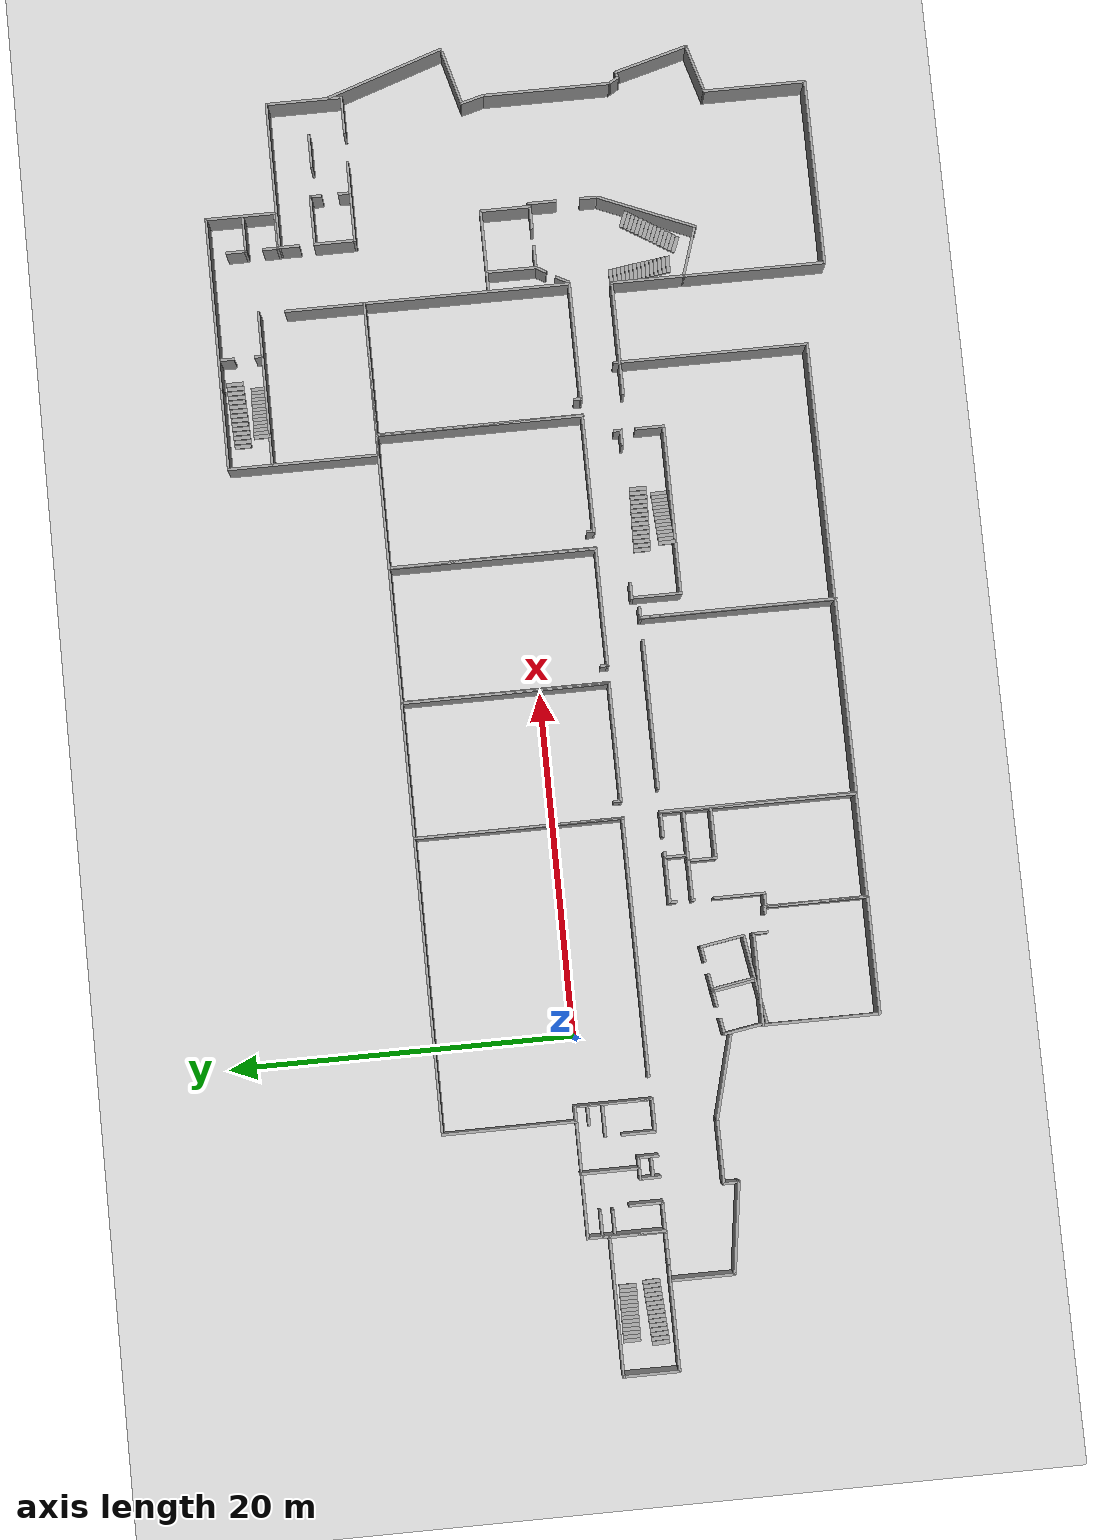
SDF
<sdf version="1.6">
 <world name="default">
  <light name="sun" type="directional">
   <pose>0 0 10 0 -0 0</pose>
   <diffuse>0.8 0.8 0.8 1</diffuse>
   <specular>0.2 0.2 0.2 1</specular>
   <attenuation>
    <range>1000</range>
    <constant>0.9</constant>
    <linear>0.01</linear>
    <quadratic>0.001</quadratic>
   </attenuation>
   <direction>-0.5 0.1 -0.9</direction>
  </light>
  <model name="ground_plane">
   <static>1</static>
   <link name="link">
    <collision name="collision">
     <geometry><plane><normal>0 0 1</normal><size>100 100</size></plane></geometry>
     <surface><friction><ode><mu>100</mu><mu2>50</mu2></ode></friction></surface>
    </collision>
    <visual name="visual">
     <cast_shadows>0</cast_shadows>
     <geometry><plane><normal>0 0 1</normal><size>100 100</size></plane></geometry>
     <material>
      <script><uri>file://media/materials/scripts/gazebo.material</uri><name>Gazebo/Grey</name></script>
     </material>
    </visual>
   </link>
  </model>
  <gravity>0 0 -9.8</gravity>
  <magnetic_field>6e-06 2.3e-05 -4.2e-05</magnetic_field>
  <atmosphere type="adiabatic"/>
  <physics name="default_physics" default="0" type="ode">
   <max_step_size>0.001</max_step_size>
   <real_time_factor>1</real_time_factor>
   <real_time_update_rate>1000</real_time_update_rate>
  </physics>
  <scene><ambient>0.4 0.4 0.4 1</ambient><background>0.7 0.7 0.7 1</background><shadows>1</shadows></scene>
  <spherical_coordinates>
   <surface_model>EARTH_WGS84</surface_model>
   <latitude_deg>0</latitude_deg>
   <longitude_deg>0</longitude_deg>
   <elevation>0</elevation>
   <heading_deg>0</heading_deg>
  </spherical_coordinates>
  <model name="203">
   <pose>3.7245 2.023 0 0 -0 0</pose>
   <link name="Wall_0">
    <collision name="Wall_0_Collision">
     <geometry><box><size>15 0.15 2.5</size></box></geometry>
     <pose>0 0 1.25 0 -0 0</pose>
    </collision>
    <visual name="Wall_0_Visual">
     <pose>0 0 1.25 0 -0 0</pose>
     <geometry><box><size>15 0.15 2.5</size></box></geometry>
     <material>
      <script><uri>file://media/materials/scripts/gazebo.material</uri><name>Gazebo/Grey</name></script>
      <ambient>1 1 1 1</ambient>
     </material>
     <meta><layer>0</layer></meta>
    </visual>
    <pose>1.0725 -6.013 0 0 -0 0</pose>
   </link>
   <link name="Wall_1">
    <collision name="Wall_1_Collision">
     <geometry><box><size>12.192 0.15 2.5</size></box></geometry>
     <pose>0 0 1.25 0 -0 0</pose>
    </collision>
    <visual name="Wall_1_Visual">
     <pose>0 0 1.25 0 -0 0</pose>
     <geometry><box><size>12.192 0.15 2.5</size></box></geometry>
     <material>
      <script><uri>file://media/materials/scripts/gazebo.material</uri><name>Gazebo/Grey</name></script>
      <ambient>1 1 1 1</ambient>
     </material>
     <meta><layer>0</layer></meta>
    </visual>
    <pose>8.4975 0.008 0 0 -0 1.5708</pose>
   </link>
   <link name="Wall_2">
    <collision name="Wall_2_Collision">
     <geometry><box><size>17.145 0.15 2.5</size></box></geometry>
     <pose>0 0 1.25 0 -0 0</pose>
    </collision>
    <visual name="Wall_2_Visual">
     <pose>0 0 1.25 0 -0 0</pose>
     <geometry><box><size>17.145 0.15 2.5</size></box></geometry>
     <material>
      <script><uri>file://media/materials/scripts/gazebo.material</uri><name>Gazebo/Grey</name></script>
      <ambient>1 1 1 1</ambient>
     </material>
     <meta><layer>0</layer></meta>
    </visual>
    <pose>-0 6.029 0 0 -0 3.14159</pose>
   </link>
   <link name="Wall_3">
    <collision name="Wall_3_Collision">
     <geometry><box><size>7.786 0.15 2.5</size></box></geometry>
     <pose>0 0 1.25 0 -0 0</pose>
    </collision>
    <visual name="Wall_3_Visual">
     <pose>0 0 1.25 0 -0 0</pose>
     <geometry><box><size>7.786 0.15 2.5</size></box></geometry>
     <material>
      <script><uri>file://media/materials/scripts/gazebo.material</uri><name>Gazebo/Grey</name></script>
      <ambient>1 1 1 1</ambient>
     </material>
     <meta><layer>0</layer></meta>
    </visual>
    <pose>-8.4975 2.211 0 0 -0 -1.5708</pose>
   </link>
   <link name="Wall_4">
    <collision name="Wall_4_Collision">
     <geometry><box><size>1 0.15 2.5</size></box></geometry>
     <pose>0 0 1.25 0 -0 0</pose>
    </collision>
    <visual name="Wall_4_Visual">
     <pose>0 0 1.25 0 -0 0</pose>
     <geometry><box><size>1 0.15 2.5</size></box></geometry>
     <material>
      <script><uri>file://media/materials/scripts/gazebo.material</uri><name>Gazebo/Grey</name></script>
      <ambient>1 1 1 1</ambient>
     </material>
     <meta><layer>0</layer></meta>
    </visual>
    <pose>-8.0725 -1.607 0 0 -0 0</pose>
   </link>
   <link name="Wall_5">
    <collision name="Wall_5_Collision">
     <geometry><box><size>4.572 0.15 2.5</size></box></geometry>
     <pose>0 0 1.25 0 -0 0</pose>
    </collision>
    <visual name="Wall_5_Visual">
     <pose>0 0 1.25 0 -0 0</pose>
     <geometry><box><size>4.572 0.15 2.5</size></box></geometry>
     <material>
      <script><uri>file://media/materials/scripts/gazebo.material</uri><name>Gazebo/Grey</name></script>
      <ambient>1 1 1 1</ambient>
     </material>
     <meta><layer>0</layer></meta>
    </visual>
    <pose>-7.6475 -3.818 0 0 -0 -1.5708</pose>
   </link>
   <static>1</static>
  </model>
  <model name="201/202">
   <pose>-7.65799 -1.81703 0 0 -0 0</pose>
   <link name="Wall_10">
    <collision name="Wall_10_Collision">
     <geometry><box><size>7.62002 0.15 2.5</size></box></geometry>
     <pose>0 0 1.25 0 -0 0</pose>
    </collision>
    <visual name="Wall_10_Visual">
     <pose>0 0 1.25 0 -0 0</pose>
     <geometry><box><size>7.62002 0.15 2.5</size></box></geometry>
     <material>
      <script><uri>file://media/materials/scripts/gazebo.material</uri><name>Gazebo/Grey</name></script>
      <ambient>1 1 1 1</ambient>
     </material>
     <meta><layer>0</layer></meta>
    </visual>
    <pose>-0.004655 2.1906 0 0 -0 3.14159</pose>
   </link>
   <link name="Wall_11">
    <collision name="Wall_11_Collision">
     <geometry><box><size>4.572 0.15 2.5</size></box></geometry>
     <pose>0 0 1.25 0 -0 0</pose>
    </collision>
    <visual name="Wall_11_Visual">
     <pose>0 0 1.25 0 -0 0</pose>
     <geometry><box><size>4.572 0.15 2.5</size></box></geometry>
     <material>
      <script><uri>file://media/materials/scripts/gazebo.material</uri><name>Gazebo/Grey</name></script>
      <ambient>1 1 1 1</ambient>
     </material>
     <meta><layer>0</layer></meta>
    </visual>
    <pose>-3.73965 -0.020398 0 0 -0 -1.5708</pose>
   </link>
   <link name="Wall_13">
    <collision name="Wall_13_Collision">
     <geometry><box><size>2 0.15 2.5</size></box></geometry>
     <pose>0 0 1.25 0 -0 0</pose>
    </collision>
    <visual name="Wall_13_Visual">
     <pose>0 0 1.25 0 -0 0</pose>
     <geometry><box><size>2 0.15 2.5</size></box></geometry>
     <material>
      <script><uri>file://media/materials/scripts/gazebo.material</uri><name>Gazebo/Grey</name></script>
      <ambient>1 1 1 1</ambient>
     </material>
     <meta><layer>0</layer></meta>
    </visual>
    <pose>2.80535 -2.23095 0 0 -0 3.14159</pose>
   </link>
   <link name="Wall_14">
    <collision name="Wall_14_Collision">
     <geometry><box><size>2 0.15 2.5</size></box></geometry>
     <pose>0 0 1.25 0 -0 0</pose>
    </collision>
    <visual name="Wall_14_Visual">
     <pose>0 0 1.25 0 -0 0</pose>
     <geometry><box><size>2 0.15 2.5</size></box></geometry>
     <material>
      <script><uri>file://media/materials/scripts/gazebo.material</uri><name>Gazebo/Grey</name></script>
      <ambient>1 1 1 1</ambient>
     </material>
     <meta><layer>0</layer></meta>
    </visual>
    <pose>1.88035 -1.30595 0 0 -0 1.5708</pose>
   </link>
   <link name="Wall_16">
    <collision name="Wall_16_Collision">
     <geometry><box><size>3.5 0.15 2.5</size></box></geometry>
     <pose>0 0 1.25 0 -0 0</pose>
    </collision>
    <visual name="Wall_16_Visual">
     <pose>0 0 1.25 0 -0 0</pose>
     <geometry><box><size>3.5 0.15 2.5</size></box></geometry>
     <material>
      <script><uri>file://media/materials/scripts/gazebo.material</uri><name>Gazebo/Grey</name></script>
      <ambient>1 1 1 1</ambient>
     </material>
     <meta><layer>0</layer></meta>
    </visual>
    <pose>-0.091763 0.556398 0 0 -0 -1.5708</pose>
   </link>
   <link name="Wall_17">
    <collision name="Wall_17_Collision">
     <geometry><box><size>0.75 0.15 2.5</size></box></geometry>
     <pose>0 0 1.25 0 -0 0</pose>
    </collision>
    <visual name="Wall_17_Visual">
     <pose>0 0 1.25 0 -0 0</pose>
     <geometry><box><size>0.75 0.15 2.5</size></box></geometry>
     <material>
      <script><uri>file://media/materials/scripts/gazebo.material</uri><name>Gazebo/Grey</name></script>
      <ambient>1 1 1 1</ambient>
     </material>
     <meta><layer>0</layer></meta>
    </visual>
    <pose>0.208236 -1.1186 0 0 -0 0</pose>
   </link>
   <link name="Wall_18">
    <collision name="Wall_18_Collision">
     <geometry><box><size>1.25 0.15 2.5</size></box></geometry>
     <pose>0 0 1.25 0 -0 0</pose>
    </collision>
    <visual name="Wall_18_Visual">
     <pose>0 0 1.25 0 -0 0</pose>
     <geometry><box><size>1.25 0.15 2.5</size></box></geometry>
     <material>
      <script><uri>file://media/materials/scripts/gazebo.material</uri><name>Gazebo/Grey</name></script>
      <ambient>1 1 1 1</ambient>
     </material>
     <meta><layer>0</layer></meta>
    </visual>
    <pose>0.508237 -1.6686 0 0 -0 -1.5708</pose>
   </link>
   <link name="Wall_20">
    <collision name="Wall_20_Collision">
     <geometry><box><size>0.75 0.15 2.5</size></box></geometry>
     <pose>0 0 1.25 0 -0 0</pose>
    </collision>
    <visual name="Wall_20_Visual">
     <pose>0 0 1.25 0 -0 0</pose>
     <geometry><box><size>0.75 0.15 2.5</size></box></geometry>
     <material>
      <script><uri>file://media/materials/scripts/gazebo.material</uri><name>Gazebo/Grey</name></script>
      <ambient>1 1 1 1</ambient>
     </material>
     <meta><layer>0</layer></meta>
    </visual>
    <pose>-0.391763 -1.1186 0 0 -0 3.14159</pose>
   </link>
   <link name="Wall_21">
    <collision name="Wall_21_Collision">
     <geometry><box><size>1.25 0.15 2.5</size></box></geometry>
     <pose>0 0 1.25 0 -0 0</pose>
    </collision>
    <visual name="Wall_21_Visual">
     <pose>0 0 1.25 0 -0 0</pose>
     <geometry><box><size>1.25 0.15 2.5</size></box></geometry>
     <material>
      <script><uri>file://media/materials/scripts/gazebo.material</uri><name>Gazebo/Grey</name></script>
      <ambient>1 1 1 1</ambient>
     </material>
     <meta><layer>0</layer></meta>
    </visual>
    <pose>-0.691764 -1.6686 0 0 -0 -1.5708</pose>
   </link>
   <link name="Wall_23">
    <collision name="Wall_23_Collision">
     <geometry><box><size>1.75 0.15 2.5</size></box></geometry>
     <pose>0 0 1.25 0 -0 0</pose>
    </collision>
    <visual name="Wall_23_Visual">
     <pose>0 0 1.25 0 -0 0</pose>
     <geometry><box><size>1.75 0.15 2.5</size></box></geometry>
     <material>
      <script><uri>file://media/materials/scripts/gazebo.material</uri><name>Gazebo/Grey</name></script>
      <ambient>1 1 1 1</ambient>
     </material>
     <meta><layer>0</layer></meta>
    </visual>
    <pose>-2.93966 -2.2314 0 0 -0 0</pose>
   </link>
   <link name="Wall_24">
    <collision name="Wall_24_Collision">
     <geometry><box><size>2 0.15 2.5</size></box></geometry>
     <pose>0 0 1.25 0 -0 0</pose>
    </collision>
    <visual name="Wall_24_Visual">
     <pose>0 0 1.25 0 -0 0</pose>
     <geometry><box><size>2 0.15 2.5</size></box></geometry>
     <material>
      <script><uri>file://media/materials/scripts/gazebo.material</uri><name>Gazebo/Grey</name></script>
      <ambient>1 1 1 1</ambient>
     </material>
     <meta><layer>0</layer></meta>
    </visual>
    <pose>-2.13965 -1.3064 0 0 -0 1.5708</pose>
   </link>
   <link name="Wall_28">
    <collision name="Wall_28_Collision">
     <geometry><box><size>1.5 0.15 2.5</size></box></geometry>
     <pose>0 0 1.25 0 -0 0</pose>
    </collision>
    <visual name="Wall_28_Visual">
     <pose>0 0 1.25 0 -0 0</pose>
     <geometry><box><size>1.5 0.15 2.5</size></box></geometry>
     <material>
      <script><uri>file://media/materials/scripts/gazebo.material</uri><name>Gazebo/Grey</name></script>
      <ambient>1 1 1 1</ambient>
     </material>
     <meta><layer>0</layer></meta>
    </visual>
    <pose>-3.01876 1.34811 0 0 -0 0</pose>
   </link>
   <link name="Wall_30">
    <collision name="Wall_30_Collision">
     <geometry><box><size>1.5 0.15 2.5</size></box></geometry>
     <pose>0 0 1.25 0 -0 0</pose>
    </collision>
    <visual name="Wall_30_Visual">
     <pose>0 0 1.25 0 -0 0</pose>
     <geometry><box><size>1.5 0.15 2.5</size></box></geometry>
     <material>
      <script><uri>file://media/materials/scripts/gazebo.material</uri><name>Gazebo/Grey</name></script>
      <ambient>1 1 1 1</ambient>
     </material>
     <meta><layer>0</layer></meta>
    </visual>
    <pose>-3.03023 0.625411 0 0 -0 0</pose>
   </link>
   <link name="Wall_32">
    <collision name="Wall_32_Collision">
     <geometry><box><size>2 0.15 2.5</size></box></geometry>
     <pose>0 0 1.25 0 -0 0</pose>
    </collision>
    <visual name="Wall_32_Visual">
     <pose>0 0 1.25 0 -0 0</pose>
     <geometry><box><size>2 0.15 2.5</size></box></geometry>
     <material>
      <script><uri>file://media/materials/scripts/gazebo.material</uri><name>Gazebo/Grey</name></script>
      <ambient>1 1 1 1</ambient>
     </material>
     <meta><layer>0</layer></meta>
    </visual>
    <pose>2.81466 0.625411 0 0 -0 3.14159</pose>
   </link>
   <link name="Wall_34">
    <collision name="Wall_34_Collision">
     <geometry><box><size>1.25 0.15 2.5</size></box></geometry>
     <pose>0 0 1.25 0 -0 0</pose>
    </collision>
    <visual name="Wall_34_Visual">
     <pose>0 0 1.25 0 -0 0</pose>
     <geometry><box><size>1.25 0.15 2.5</size></box></geometry>
     <material>
      <script><uri>file://media/materials/scripts/gazebo.material</uri><name>Gazebo/Grey</name></script>
      <ambient>1 1 1 1</ambient>
     </material>
     <meta><layer>0</layer></meta>
    </visual>
    <pose>3.16672 1.48576 0 0 -0 3.14159</pose>
   </link>
   <link name="Wall_36">
    <collision name="Wall_36_Collision">
     <geometry><box><size>1.25 0.15 2.5</size></box></geometry>
     <pose>0 0 1.25 0 -0 0</pose>
    </collision>
    <visual name="Wall_36_Visual">
     <pose>0 0 1.25 0 -0 0</pose>
     <geometry><box><size>1.25 0.15 2.5</size></box></geometry>
     <material>
      <script><uri>file://media/materials/scripts/gazebo.material</uri><name>Gazebo/Grey</name></script>
      <ambient>1 1 1 1</ambient>
     </material>
     <meta><layer>0</layer></meta>
    </visual>
    <pose>-0.138273 -1.8524 0 0 -0 0</pose>
   </link>
   <link name="Wall_9">
    <collision name="Wall_9_Collision">
     <geometry><box><size>4.572 0.15 2.5</size></box></geometry>
     <pose>0 0 1.25 0 -0 0</pose>
    </collision>
    <visual name="Wall_9_Visual">
     <pose>0 0 1.25 0 -0 0</pose>
     <geometry><box><size>4.572 0.15 2.5</size></box></geometry>
     <material>
      <script><uri>file://media/materials/scripts/gazebo.material</uri><name>Gazebo/Grey</name></script>
      <ambient>1 1 1 1</ambient>
     </material>
     <meta><layer>0</layer></meta>
    </visual>
    <pose>3.73035 -0.020175 0 0 -0 1.5708</pose>
   </link>
   <static>1</static>
  </model>
  <model name="197A">
   <pose>-15.372 -2.4638 0 0 -0 0</pose>
   <link name="Door_4">
    <collision name="Door_4_Collision">
     <geometry><box><size>0.9 0.17 2</size></box></geometry>
     <pose>0 0 1 0 -0 0</pose>
    </collision>
    <visual name="Door_4_Visual">
     <pose>0 0 1 0 -0 0</pose>
     <geometry><box><size>0.9 0.17 2</size></box></geometry>
     <material>
      <script><uri>file://media/materials/scripts/gazebo.material</uri><name>Gazebo/Grey</name></script>
     </material>
    </visual>
    <pose>3.38585 -1.61049 0 0 -0 0</pose>
   </link>
   <link name="Door_5">
    <collision name="Door_5_Collision">
     <geometry><box><size>0.9 0.17 2</size></box></geometry>
     <pose>0 0 1 0 -0 0</pose>
    </collision>
    <visual name="Door_5_Visual">
     <pose>0 0 1 0 -0 0</pose>
     <geometry><box><size>0.9 0.17 2</size></box></geometry>
     <material>
      <script><uri>file://media/materials/scripts/gazebo.material</uri><name>Gazebo/Grey</name></script>
     </material>
    </visual>
    <pose>2.47636 -1.61049 0 0 -0 0</pose>
   </link>
   <link name="Wall_33">
    <collision name="Wall_33_Collision">
     <geometry><box><size>3.336 0.15 2.5</size></box></geometry>
     <pose>0 0 1.25 0 -0 0</pose>
    </collision>
    <visual name="Wall_33_Visual">
     <pose>0 0 1.25 0 -0 0</pose>
     <geometry><box><size>3.336 0.15 2.5</size></box></geometry>
     <material>
      <script><uri>file://media/materials/scripts/gazebo.material</uri><name>Gazebo/Grey</name></script>
      <ambient>1 1 1 1</ambient>
     </material>
     <meta><layer>0</layer></meta>
    </visual>
    <pose>3.925 -0 0 0 -0 1.5708</pose>
   </link>
   <link name="Wall_34">
    <collision name="Wall_34_Collision">
     <geometry><box><size>8 0.15 2.5</size></box></geometry>
     <pose>0 0 1.25 0 -0 0</pose>
    </collision>
    <visual name="Wall_34_Visual">
     <pose>0 0 1.25 0 -0 0</pose>
     <geometry><box><size>8 0.15 2.5</size></box></geometry>
     <material>
      <script><uri>file://media/materials/scripts/gazebo.material</uri><name>Gazebo/Grey</name></script>
      <ambient>1 1 1 1</ambient>
     </material>
     <meta><layer>0</layer></meta>
    </visual>
    <pose>-0 1.593 0 0 -0 3.14159</pose>
   </link>
   <link name="Wall_35">
    <collision name="Wall_35_Collision">
     <geometry><box><size>3.336 0.15 2.5</size></box></geometry>
     <pose>0 0 1.25 0 -0 0</pose>
    </collision>
    <visual name="Wall_35_Visual">
     <pose>0 0 1.25 0 -0 0</pose>
     <geometry><box><size>3.336 0.15 2.5</size></box></geometry>
     <material>
      <script><uri>file://media/materials/scripts/gazebo.material</uri><name>Gazebo/Grey</name></script>
      <ambient>1 1 1 1</ambient>
     </material>
     <meta><layer>0</layer></meta>
    </visual>
    <pose>-3.925 -0 0 0 -0 -1.5708</pose>
   </link>
   <link name="Wall_37">
    <collision name="Wall_37_Collision">
     <geometry><box><size>6 0.15 2.5</size></box></geometry>
     <pose>0 0 1.25 0 -0 0</pose>
    </collision>
    <visual name="Wall_37_Visual">
     <pose>0 0 1.25 0 -0 0</pose>
     <geometry><box><size>6 0.15 2.5</size></box></geometry>
     <material>
      <script><uri>file://media/materials/scripts/gazebo.material</uri><name>Gazebo/Grey</name></script>
      <ambient>1 1 1 1</ambient>
     </material>
     <meta><layer>0</layer></meta>
    </visual>
    <pose>-1 -1.593 0 0 -0 0</pose>
   </link>
   <static>1</static>
  </model>
  <model name="classrooms">
   <pose>16.1404 2.02516 0 0 -0 0</pose>
   <link name="Wall_39">
    <collision name="Wall_39_Collision">
     <geometry><box><size>12.192 0.15 2.5</size></box></geometry>
     <pose>0 0 1.25 0 -0 0</pose>
    </collision>
    <visual name="Wall_39_Visual">
     <pose>0 0 1.25 0 -0 0</pose>
     <geometry><box><size>12.192 0.15 2.5</size></box></geometry>
     <material>
      <script><uri>file://media/materials/scripts/gazebo.material</uri><name>Gazebo/Grey</name></script>
      <ambient>1 1 1 1</ambient>
     </material>
     <meta><layer>0</layer></meta>
    </visual>
    <pose>3.92486 -0.000205 0 0 -0 1.5708</pose>
   </link>
   <link name="Wall_40">
    <collision name="Wall_40_Collision">
     <geometry><box><size>7.99972 0.15 2.5</size></box></geometry>
     <pose>0 0 1.25 0 -0 0</pose>
    </collision>
    <visual name="Wall_40_Visual">
     <pose>0 0 1.25 0 -0 0</pose>
     <geometry><box><size>7.99972 0.15 2.5</size></box></geometry>
     <material>
      <script><uri>file://media/materials/scripts/gazebo.material</uri><name>Gazebo/Grey</name></script>
      <ambient>1 1 1 1</ambient>
     </material>
     <meta><layer>0</layer></meta>
    </visual>
    <pose>0 6.02093 0 0 -0 3.14156</pose>
   </link>
   <link name="Wall_41">
    <collision name="Wall_41_Collision">
     <geometry><box><size>12.1923 0.15 2.5</size></box></geometry>
     <pose>0 0 1.25 0 -0 0</pose>
    </collision>
    <visual name="Wall_41_Visual">
     <pose>0 0 1.25 0 -0 0</pose>
     <geometry><box><size>12.1923 0.15 2.5</size></box></geometry>
     <material>
      <script><uri>file://media/materials/scripts/gazebo.material</uri><name>Gazebo/Grey</name></script>
      <ambient>1 1 1 1</ambient>
     </material>
     <meta><layer>0</layer></meta>
    </visual>
    <pose>-3.92486 6.8e-05 0 0 -0 -1.5708</pose>
   </link>
   <link name="Wall_43">
    <collision name="Wall_43_Collision">
     <geometry><box><size>7 0.15 2.5</size></box></geometry>
     <pose>0 0 1.25 0 -0 0</pose>
    </collision>
    <visual name="Wall_43_Visual">
     <pose>0 0 1.25 0 -0 0</pose>
     <geometry><box><size>7 0.15 2.5</size></box></geometry>
     <material>
      <script><uri>file://media/materials/scripts/gazebo.material</uri><name>Gazebo/Grey</name></script>
      <ambient>1 1 1 1</ambient>
     </material>
     <meta><layer>0</layer></meta>
    </visual>
    <pose>0.49986 -6.02121 0 0 -0 3.14159</pose>
   </link>
   <link name="Wall_44">
    <collision name="Wall_44_Collision">
     <geometry><box><size>0.5 0.15 2.5</size></box></geometry>
     <pose>0 0 1.25 0 -0 0</pose>
    </collision>
    <visual name="Wall_44_Visual">
     <pose>0 0 1.25 0 -0 0</pose>
     <geometry><box><size>0.5 0.15 2.5</size></box></geometry>
     <material>
      <script><uri>file://media/materials/scripts/gazebo.material</uri><name>Gazebo/Grey</name></script>
      <ambient>1 1 1 1</ambient>
     </material>
     <meta><layer>0</layer></meta>
    </visual>
    <pose>-2.92514 -5.84621 0 0 -0 1.5708</pose>
   </link>
   <static>1</static>
  </model>
  <model name="classrooms_0">
   <pose>24.0244 2.00671 0 0 -0 0</pose>
   <link name="Wall_39">
    <collision name="Wall_39_Collision">
     <geometry><box><size>12.192 0.15 2.5</size></box></geometry>
     <pose>0 0 1.25 0 -0 0</pose>
    </collision>
    <visual name="Wall_39_Visual">
     <pose>0 0 1.25 0 -0 0</pose>
     <geometry><box><size>12.192 0.15 2.5</size></box></geometry>
     <material>
      <script><uri>file://media/materials/scripts/gazebo.material</uri><name>Gazebo/Grey</name></script>
      <ambient>1 1 1 1</ambient>
     </material>
     <meta><layer>0</layer></meta>
    </visual>
    <pose>3.92486 -0.000205 0 0 -0 1.5708</pose>
   </link>
   <link name="Wall_40">
    <collision name="Wall_40_Collision">
     <geometry><box><size>7.99972 0.15 2.5</size></box></geometry>
     <pose>0 0 1.25 0 -0 0</pose>
    </collision>
    <visual name="Wall_40_Visual">
     <pose>0 0 1.25 0 -0 0</pose>
     <geometry><box><size>7.99972 0.15 2.5</size></box></geometry>
     <material>
      <script><uri>file://media/materials/scripts/gazebo.material</uri><name>Gazebo/Grey</name></script>
      <ambient>1 1 1 1</ambient>
     </material>
     <meta><layer>0</layer></meta>
    </visual>
    <pose>0 6.02093 0 0 -0 3.14156</pose>
   </link>
   <link name="Wall_41">
    <collision name="Wall_41_Collision">
     <geometry><box><size>12.1923 0.15 2.5</size></box></geometry>
     <pose>0 0 1.25 0 -0 0</pose>
    </collision>
    <visual name="Wall_41_Visual">
     <pose>0 0 1.25 0 -0 0</pose>
     <geometry><box><size>12.1923 0.15 2.5</size></box></geometry>
     <material>
      <script><uri>file://media/materials/scripts/gazebo.material</uri><name>Gazebo/Grey</name></script>
      <ambient>1 1 1 1</ambient>
     </material>
     <meta><layer>0</layer></meta>
    </visual>
    <pose>-3.92486 6.8e-05 0 0 -0 -1.5708</pose>
   </link>
   <link name="Wall_43">
    <collision name="Wall_43_Collision">
     <geometry><box><size>7 0.15 2.5</size></box></geometry>
     <pose>0 0 1.25 0 -0 0</pose>
    </collision>
    <visual name="Wall_43_Visual">
     <pose>0 0 1.25 0 -0 0</pose>
     <geometry><box><size>7 0.15 2.5</size></box></geometry>
     <material>
      <script><uri>file://media/materials/scripts/gazebo.material</uri><name>Gazebo/Grey</name></script>
      <ambient>1 1 1 1</ambient>
     </material>
     <meta><layer>0</layer></meta>
    </visual>
    <pose>0.49986 -6.02121 0 0 -0 3.14159</pose>
   </link>
   <link name="Wall_44">
    <collision name="Wall_44_Collision">
     <geometry><box><size>0.5 0.15 2.5</size></box></geometry>
     <pose>0 0 1.25 0 -0 0</pose>
    </collision>
    <visual name="Wall_44_Visual">
     <pose>0 0 1.25 0 -0 0</pose>
     <geometry><box><size>0.5 0.15 2.5</size></box></geometry>
     <material>
      <script><uri>file://media/materials/scripts/gazebo.material</uri><name>Gazebo/Grey</name></script>
      <ambient>1 1 1 1</ambient>
     </material>
     <meta><layer>0</layer></meta>
    </visual>
    <pose>-2.92514 -5.84621 0 0 -0 1.5708</pose>
   </link>
   <static>1</static>
  </model>
  <model name="classrooms_2">
   <pose>39.734 1.98873 0 0 -0 0</pose>
   <link name="Wall_39">
    <collision name="Wall_39_Collision">
     <geometry><box><size>12.192 0.15 2.5</size></box></geometry>
     <pose>0 0 1.25 0 -0 0</pose>
    </collision>
    <visual name="Wall_39_Visual">
     <pose>0 0 1.25 0 -0 0</pose>
     <geometry><box><size>12.192 0.15 2.5</size></box></geometry>
     <material>
      <script><uri>file://media/materials/scripts/gazebo.material</uri><name>Gazebo/Grey</name></script>
      <ambient>1 1 1 1</ambient>
     </material>
     <meta><layer>0</layer></meta>
    </visual>
    <pose>3.92486 -0.000205 0 0 -0 1.5708</pose>
   </link>
   <link name="Wall_40">
    <collision name="Wall_40_Collision">
     <geometry><box><size>7.99972 0.15 2.5</size></box></geometry>
     <pose>0 0 1.25 0 -0 0</pose>
    </collision>
    <visual name="Wall_40_Visual">
     <pose>0 0 1.25 0 -0 0</pose>
     <geometry><box><size>7.99972 0.15 2.5</size></box></geometry>
     <material>
      <script><uri>file://media/materials/scripts/gazebo.material</uri><name>Gazebo/Grey</name></script>
      <ambient>1 1 1 1</ambient>
     </material>
     <meta><layer>0</layer></meta>
    </visual>
    <pose>0 6.02093 0 0 -0 3.14156</pose>
   </link>
   <link name="Wall_41">
    <collision name="Wall_41_Collision">
     <geometry><box><size>12.1923 0.15 2.5</size></box></geometry>
     <pose>0 0 1.25 0 -0 0</pose>
    </collision>
    <visual name="Wall_41_Visual">
     <pose>0 0 1.25 0 -0 0</pose>
     <geometry><box><size>12.1923 0.15 2.5</size></box></geometry>
     <material>
      <script><uri>file://media/materials/scripts/gazebo.material</uri><name>Gazebo/Grey</name></script>
      <ambient>1 1 1 1</ambient>
     </material>
     <meta><layer>0</layer></meta>
    </visual>
    <pose>-3.92486 6.8e-05 0 0 -0 -1.5708</pose>
   </link>
   <link name="Wall_43">
    <collision name="Wall_43_Collision">
     <geometry><box><size>7 0.15 2.5</size></box></geometry>
     <pose>0 0 1.25 0 -0 0</pose>
    </collision>
    <visual name="Wall_43_Visual">
     <pose>0 0 1.25 0 -0 0</pose>
     <geometry><box><size>7 0.15 2.5</size></box></geometry>
     <material>
      <script><uri>file://media/materials/scripts/gazebo.material</uri><name>Gazebo/Grey</name></script>
      <ambient>1 1 1 1</ambient>
     </material>
     <meta><layer>0</layer></meta>
    </visual>
    <pose>0.49986 -6.02121 0 0 -0 3.14159</pose>
   </link>
   <link name="Wall_44">
    <collision name="Wall_44_Collision">
     <geometry><box><size>0.5 0.15 2.5</size></box></geometry>
     <pose>0 0 1.25 0 -0 0</pose>
    </collision>
    <visual name="Wall_44_Visual">
     <pose>0 0 1.25 0 -0 0</pose>
     <geometry><box><size>0.5 0.15 2.5</size></box></geometry>
     <material>
      <script><uri>file://media/materials/scripts/gazebo.material</uri><name>Gazebo/Grey</name></script>
      <ambient>1 1 1 1</ambient>
     </material>
     <meta><layer>0</layer></meta>
    </visual>
    <pose>-2.92514 -5.84621 0 0 -0 1.5708</pose>
   </link>
   <static>1</static>
  </model>
  <model name="207">
   <pose>18.0365 -11.8818 0 0 -0 0</pose>
   <link name="Wall_50">
    <collision name="Wall_50_Collision">
     <geometry><box><size>11.46 0.15 2.5</size></box></geometry>
     <pose>0 0 1.25 0 -0 0</pose>
    </collision>
    <visual name="Wall_50_Visual">
     <pose>0 0 1.25 0 -0 0</pose>
     <geometry><box><size>11.46 0.15 2.5</size></box></geometry>
     <material>
      <script><uri>file://media/materials/scripts/gazebo.material</uri><name>Gazebo/Grey</name></script>
      <ambient>1 1 1 1</ambient>
     </material>
     <meta><layer>0</layer></meta>
    </visual>
    <pose>7.2e-05 -5.65487 0 0 -0 -2.4e-05</pose>
   </link>
   <link name="Wall_51">
    <collision name="Wall_51_Collision">
     <geometry><box><size>11.5001 0.15 2.5</size></box></geometry>
     <pose>0 0 1.25 0 -0 0</pose>
    </collision>
    <visual name="Wall_51_Visual">
     <pose>0 0 1.25 0 -0 0</pose>
     <geometry><box><size>11.5001 0.15 2.5</size></box></geometry>
     <material>
      <script><uri>file://media/materials/scripts/gazebo.material</uri><name>Gazebo/Grey</name></script>
      <ambient>1 1 1 1</ambient>
     </material>
     <meta><layer>0</layer></meta>
    </visual>
    <pose>5.65493 -1e-06 0 0 -0 1.5708</pose>
   </link>
   <link name="Wall_53">
    <collision name="Wall_53_Collision">
     <geometry><box><size>11.4597 0.15 2.5</size></box></geometry>
     <pose>0 0 1.25 0 -0 0</pose>
    </collision>
    <visual name="Wall_53_Visual">
     <pose>0 0 1.25 0 -0 0</pose>
     <geometry><box><size>11.4597 0.15 2.5</size></box></geometry>
     <material>
      <script><uri>file://media/materials/scripts/gazebo.material</uri><name>Gazebo/Grey</name></script>
      <ambient>1 1 1 1</ambient>
     </material>
     <meta><layer>0</layer></meta>
    </visual>
    <pose>-5.65493 0.020199 0 0 -0 -1.57077</pose>
   </link>
   <link name="Wall_56">
    <collision name="Wall_56_Collision">
     <geometry><box><size>8.76 0.15 2.5</size></box></geometry>
     <pose>0 0 1.25 0 -0 0</pose>
    </collision>
    <visual name="Wall_56_Visual">
     <pose>0 0 1.25 0 -0 0</pose>
     <geometry><box><size>8.76 0.15 2.5</size></box></geometry>
     <material>
      <script><uri>file://media/materials/scripts/gazebo.material</uri><name>Gazebo/Grey</name></script>
      <ambient>1 1 1 1</ambient>
     </material>
     <meta><layer>0</layer></meta>
    </visual>
    <pose>-7.2e-05 5.67506 0 0 -0 0</pose>
   </link>
   <static>1</static>
  </model>
  <model name="205">
   <pose>9.3396 -11.8618 0 0 -0 0</pose>
   <link name="Wall_59">
    <collision name="Wall_59_Collision">
     <geometry><box><size>6.096 0.15 2.5</size></box></geometry>
     <pose>0 0 1.25 0 -0 0</pose>
    </collision>
    <visual name="Wall_59_Visual">
     <pose>0 0 1.25 0 -0 0</pose>
     <geometry><box><size>6.096 0.15 2.5</size></box></geometry>
     <material>
      <script><uri>file://media/materials/scripts/gazebo.material</uri><name>Gazebo/Grey</name></script>
      <ambient>1 1 1 1</ambient>
     </material>
     <meta><layer>0</layer></meta>
    </visual>
    <pose>0.000181 -5.65489 0 0 -0 0</pose>
   </link>
   <link name="Wall_60">
    <collision name="Wall_60_Collision">
     <geometry><box><size>11.46 0.15 2.5</size></box></geometry>
     <pose>0 0 1.25 0 -0 0</pose>
    </collision>
    <visual name="Wall_60_Visual">
     <pose>0 0 1.25 0 -0 0</pose>
     <geometry><box><size>11.46 0.15 2.5</size></box></geometry>
     <material>
      <script><uri>file://media/materials/scripts/gazebo.material</uri><name>Gazebo/Grey</name></script>
      <ambient>1 1 1 1</ambient>
     </material>
     <meta><layer>0</layer></meta>
    </visual>
    <pose>2.973 2e-06 0 0 -0 1.57083</pose>
   </link>
   <link name="Wall_63">
    <collision name="Wall_63_Collision">
     <geometry><box><size>5.23836 0.15 2.5</size></box></geometry>
     <pose>0 0 1.25 0 -0 0</pose>
    </collision>
    <visual name="Wall_63_Visual">
     <pose>0 0 1.25 0 -0 0</pose>
     <geometry><box><size>5.23836 0.15 2.5</size></box></geometry>
     <material>
      <script><uri>file://media/materials/scripts/gazebo.material</uri><name>Gazebo/Grey</name></script>
      <ambient>1 1 1 1</ambient>
     </material>
     <meta><layer>0</layer></meta>
    </visual>
    <pose>0.332822 4.3449 0 0 -0 0</pose>
   </link>
   <link name="Wall_65">
    <collision name="Wall_65_Collision">
     <geometry><box><size>1.4 0.15 2.5</size></box></geometry>
     <pose>0 0 1.25 0 -0 0</pose>
    </collision>
    <visual name="Wall_65_Visual">
     <pose>0 0 1.25 0 -0 0</pose>
     <geometry><box><size>1.4 0.15 2.5</size></box></geometry>
     <material>
      <script><uri>file://media/materials/scripts/gazebo.material</uri><name>Gazebo/Grey</name></script>
      <ambient>1 1 1 1</ambient>
     </material>
     <meta><layer>0</layer></meta>
    </visual>
    <pose>0.397839 5.00182 0 0 -0 1.5708</pose>
   </link>
   <link name="Wall_67">
    <collision name="Wall_67_Collision">
     <geometry><box><size>1.75 0.15 2.5</size></box></geometry>
     <pose>0 0 1.25 0 -0 0</pose>
    </collision>
    <visual name="Wall_67_Visual">
     <pose>0 0 1.25 0 -0 0</pose>
     <geometry><box><size>1.75 0.15 2.5</size></box></geometry>
     <material>
      <script><uri>file://media/materials/scripts/gazebo.material</uri><name>Gazebo/Grey</name></script>
      <ambient>1 1 1 1</ambient>
     </material>
     <meta><layer>0</layer></meta>
    </visual>
    <pose>0.076823 3.55676 0 0 -0 -1.5708</pose>
   </link>
   <link name="Wall_68">
    <collision name="Wall_68_Collision">
     <geometry><box><size>3 0.15 2.5</size></box></geometry>
     <pose>0 0 1.25 0 -0 0</pose>
    </collision>
    <visual name="Wall_68_Visual">
     <pose>0 0 1.25 0 -0 0</pose>
     <geometry><box><size>3 0.15 2.5</size></box></geometry>
     <material>
      <script><uri>file://media/materials/scripts/gazebo.material</uri><name>Gazebo/Grey</name></script>
      <ambient>1 1 1 1</ambient>
     </material>
     <meta><layer>0</layer></meta>
    </visual>
    <pose>1.50182 2.75676 0 0 -0 0</pose>
   </link>
   <link name="Wall_70">
    <collision name="Wall_70_Collision">
     <geometry><box><size>6 0.15 2.5</size></box></geometry>
     <pose>0 0 1.25 0 -0 0</pose>
    </collision>
    <visual name="Wall_70_Visual">
     <pose>0 0 1.25 0 -0 0</pose>
     <geometry><box><size>6 0.15 2.5</size></box></geometry>
     <material>
      <script><uri>file://media/materials/scripts/gazebo.material</uri><name>Gazebo/Grey</name></script>
      <ambient>1 1 1 1</ambient>
     </material>
     <meta><layer>0</layer></meta>
    </visual>
    <pose>-2.973 -2.73 0 0 -0 1.57086</pose>
   </link>
   <link name="Wall_71">
    <collision name="Wall_71_Collision">
     <geometry><box><size>0.912 0.15 2.5</size></box></geometry>
     <pose>0 0 1.25 0 -0 0</pose>
    </collision>
    <visual name="Wall_71_Visual">
     <pose>0 0 1.25 0 -0 0</pose>
     <geometry><box><size>0.912 0.15 2.5</size></box></geometry>
     <material>
      <script><uri>file://media/materials/scripts/gazebo.material</uri><name>Gazebo/Grey</name></script>
      <ambient>1 1 1 1</ambient>
     </material>
     <meta><layer>0</layer></meta>
    </visual>
    <pose>-2.59218 0.194898 0 0 -0 0</pose>
   </link>
   <link name="Wall_74">
    <collision name="Wall_74_Collision">
     <geometry><box><size>3 0.15 2.5</size></box></geometry>
     <pose>0 0 1.25 0 -0 0</pose>
    </collision>
    <visual name="Wall_74_Visual">
     <pose>0 0 1.25 0 -0 0</pose>
     <geometry><box><size>3 0.15 2.5</size></box></geometry>
     <material>
      <script><uri>file://media/materials/scripts/gazebo.material</uri><name>Gazebo/Grey</name></script>
      <ambient>1 1 1 1</ambient>
     </material>
     <meta><layer>0</layer></meta>
    </visual>
    <pose>-2.21118 1.6199 0 0 -0 1.5708</pose>
   </link>
   <link name="Wall_76">
    <collision name="Wall_76_Collision">
     <geometry><box><size>0.5 0.15 2.5</size></box></geometry>
     <pose>0 0 1.25 0 -0 0</pose>
    </collision>
    <visual name="Wall_76_Visual">
     <pose>0 0 1.25 0 -0 0</pose>
     <geometry><box><size>0.5 0.15 2.5</size></box></geometry>
     <material>
      <script><uri>file://media/materials/scripts/gazebo.material</uri><name>Gazebo/Grey</name></script>
      <ambient>1 1 1 1</ambient>
     </material>
     <meta><layer>0</layer></meta>
    </visual>
    <pose>-2.21118 5.4799 0 0 -0 -1.5708</pose>
   </link>
   <link name="Wall_80">
    <collision name="Wall_80_Collision">
     <geometry><box><size>0.25 0.15 2.5</size></box></geometry>
     <pose>0 0 1.25 0 -0 0</pose>
    </collision>
    <visual name="Wall_80_Visual">
     <pose>0 0 1.25 0 -0 0</pose>
     <geometry><box><size>0.25 0.15 2.5</size></box></geometry>
     <material>
      <script><uri>file://media/materials/scripts/gazebo.material</uri><name>Gazebo/Grey</name></script>
      <ambient>1 1 1 1</ambient>
     </material>
     <meta><layer>0</layer></meta>
    </visual>
    <pose>-2.21118 4.2949 0 0 -0 -1.5708</pose>
   </link>
   <link name="Wall_82">
    <collision name="Wall_82_Collision">
     <geometry><box><size>3 0.15 2.5</size></box></geometry>
     <pose>0 0 1.25 0 -0 0</pose>
    </collision>
    <visual name="Wall_82_Visual">
     <pose>0 0 1.25 0 -0 0</pose>
     <geometry><box><size>3 0.15 2.5</size></box></geometry>
     <material>
      <script><uri>file://media/materials/scripts/gazebo.material</uri><name>Gazebo/Grey</name></script>
      <ambient>1 1 1 1</ambient>
     </material>
     <meta><layer>0</layer></meta>
    </visual>
    <pose>-0.786178 5.6549 0 0 -0 0</pose>
   </link>
   <link name="Wall_84">
    <collision name="Wall_84_Collision">
     <geometry><box><size>1.5 0.15 2.5</size></box></geometry>
     <pose>0 0 1.25 0 -0 0</pose>
    </collision>
    <visual name="Wall_84_Visual">
     <pose>0 0 1.25 0 -0 0</pose>
     <geometry><box><size>1.5 0.15 2.5</size></box></geometry>
     <material>
      <script><uri>file://media/materials/scripts/gazebo.material</uri><name>Gazebo/Grey</name></script>
      <ambient>1 1 1 1</ambient>
     </material>
     <meta><layer>0</layer></meta>
    </visual>
    <pose>2.29782 5.6549 0 0 -0 0</pose>
   </link>
   <static>1</static>
  </model>
  <model name="205A">
   <pose>2.99275 -14.1754 0 0 -0 0</pose>
   <link name="Wall_86">
    <collision name="Wall_86_Collision">
     <geometry><box><size>6.858 0.15 2.5</size></box></geometry>
     <pose>0 0 1.25 0 -0 0</pose>
    </collision>
    <visual name="Wall_86_Visual">
     <pose>0 0 1.25 0 -0 0</pose>
     <geometry><box><size>6.858 0.15 2.5</size></box></geometry>
     <material>
      <script><uri>file://media/materials/scripts/gazebo.material</uri><name>Gazebo/Grey</name></script>
      <ambient>1 1 1 1</ambient>
     </material>
     <meta><layer>0</layer></meta>
    </visual>
    <pose>-3.354 0.010144 0 0 -0 -1.5708</pose>
   </link>
   <link name="Wall_87">
    <collision name="Wall_87_Collision">
     <geometry><box><size>6.858 0.15 2.5</size></box></geometry>
     <pose>0 0 1.25 0 -0 0</pose>
    </collision>
    <visual name="Wall_87_Visual">
     <pose>0 0 1.25 0 -0 0</pose>
     <geometry><box><size>6.858 0.15 2.5</size></box></geometry>
     <material>
      <script><uri>file://media/materials/scripts/gazebo.material</uri><name>Gazebo/Grey</name></script>
      <ambient>1 1 1 1</ambient>
     </material>
     <meta><layer>0</layer></meta>
    </visual>
    <pose>0 -3.35389 0 0 -0 -0.002991</pose>
   </link>
   <link name="Wall_88">
    <collision name="Wall_88_Collision">
     <geometry><box><size>6.096 0.15 2.5</size></box></geometry>
     <pose>0 0 1.25 0 -0 0</pose>
    </collision>
    <visual name="Wall_88_Visual">
     <pose>0 0 1.25 0 -0 0</pose>
     <geometry><box><size>6.096 0.15 2.5</size></box></geometry>
     <material>
      <script><uri>file://media/materials/scripts/gazebo.material</uri><name>Gazebo/Grey</name></script>
      <ambient>1 1 1 1</ambient>
     </material>
     <meta><layer>0</layer></meta>
    </visual>
    <pose>3.354 -0.390888 0 0 -0 1.5708</pose>
   </link>
   <link name="Wall_90">
    <collision name="Wall_90_Collision">
     <geometry><box><size>0.932 0.15 2.5</size></box></geometry>
     <pose>0 0 1.25 0 -0 0</pose>
    </collision>
    <visual name="Wall_90_Visual">
     <pose>0 0 1.25 0 -0 0</pose>
     <geometry><box><size>0.932 0.15 2.5</size></box></geometry>
     <material>
      <script><uri>file://media/materials/scripts/gazebo.material</uri><name>Gazebo/Grey</name></script>
      <ambient>1 1 1 1</ambient>
     </material>
     <meta><layer>0</layer></meta>
    </visual>
    <pose>1.896 2.97314 0 0 -0 1.5708</pose>
   </link>
   <link name="Wall_91">
    <collision name="Wall_91_Collision">
     <geometry><box><size>5.4 0.15 2.5</size></box></geometry>
     <pose>0 0 1.25 0 -0 0</pose>
    </collision>
    <visual name="Wall_91_Visual">
     <pose>0 0 1.25 0 -0 0</pose>
     <geometry><box><size>5.4 0.15 2.5</size></box></geometry>
     <material>
      <script><uri>file://media/materials/scripts/gazebo.material</uri><name>Gazebo/Grey</name></script>
      <ambient>1 1 1 1</ambient>
     </material>
     <meta><layer>0</layer></meta>
    </visual>
    <pose>-0.729 3.36414 0 0 -0 3.14159</pose>
   </link>
   <link name="Wall_93">
    <collision name="Wall_93_Collision">
     <geometry><box><size>0.5 0.15 2.5</size></box></geometry>
     <pose>0 0 1.25 0 -0 0</pose>
    </collision>
    <visual name="Wall_93_Visual">
     <pose>0 0 1.25 0 -0 0</pose>
     <geometry><box><size>0.5 0.15 2.5</size></box></geometry>
     <material>
      <script><uri>file://media/materials/scripts/gazebo.material</uri><name>Gazebo/Grey</name></script>
      <ambient>1 1 1 1</ambient>
     </material>
     <meta><layer>0</layer></meta>
    </visual>
    <pose>3.179 2.58214 0 0 -0 3.14159</pose>
   </link>
   <static>1</static>
  </model>
  <model name="195">
   <pose>0.783312 -9.59518 0 0 -0 0.16262</pose>
   <link name="Wall_52">
    <collision name="Wall_52_Collision">
     <geometry><box><size>2.667 0.15 2.5</size></box></geometry>
     <pose>0 0 1.25 0 -0 0</pose>
    </collision>
    <visual name="Wall_52_Visual">
     <pose>0 0 1.25 0 -0 0</pose>
     <geometry><box><size>2.667 0.15 2.5</size></box></geometry>
     <material>
      <script><uri>file://media/materials/scripts/gazebo.material</uri><name>Gazebo/Grey</name></script>
      <ambient>1 1 1 1</ambient>
     </material>
     <meta><layer>0</layer></meta>
    </visual>
    <pose>-0.000138 -1.2585 0 0 -0 0</pose>
   </link>
   <link name="Wall_53">
    <collision name="Wall_53_Collision">
     <geometry><box><size>2.667 0.15 2.5</size></box></geometry>
     <pose>0 0 1.25 0 -0 0</pose>
    </collision>
    <visual name="Wall_53_Visual">
     <pose>0 0 1.25 0 -0 0</pose>
     <geometry><box><size>2.667 0.15 2.5</size></box></geometry>
     <material>
      <script><uri>file://media/materials/scripts/gazebo.material</uri><name>Gazebo/Grey</name></script>
      <ambient>1 1 1 1</ambient>
     </material>
     <meta><layer>0</layer></meta>
    </visual>
    <pose>1.2585 0 0 0 -0 1.57069</pose>
   </link>
   <link name="Wall_55">
    <collision name="Wall_55_Collision">
     <geometry><box><size>2.667 0.15 2.5</size></box></geometry>
     <pose>0 0 1.25 0 -0 0</pose>
    </collision>
    <visual name="Wall_55_Visual">
     <pose>0 0 1.25 0 -0 0</pose>
     <geometry><box><size>2.667 0.15 2.5</size></box></geometry>
     <material>
      <script><uri>file://media/materials/scripts/gazebo.material</uri><name>Gazebo/Grey</name></script>
      <ambient>1 1 1 1</ambient>
     </material>
     <meta><layer>0</layer></meta>
    </visual>
    <pose>-1.2585 0 0 0 -0 -1.57091</pose>
   </link>
   <link name="Wall_57">
    <collision name="Wall_57_Collision">
     <geometry><box><size>1 0.15 2.5</size></box></geometry>
     <pose>0 0 1.25 0 -0 0</pose>
    </collision>
    <visual name="Wall_57_Visual">
     <pose>0 0 1.25 0 -0 0</pose>
     <geometry><box><size>1 0.15 2.5</size></box></geometry>
     <material>
      <script><uri>file://media/materials/scripts/gazebo.material</uri><name>Gazebo/Grey</name></script>
      <ambient>1 1 1 1</ambient>
     </material>
     <meta><layer>0</layer></meta>
    </visual>
    <pose>0.833639 1.2585 0 0 -0 3.14159</pose>
   </link>
   <link name="Wall_59">
    <collision name="Wall_59_Collision">
     <geometry><box><size>1 0.15 2.5</size></box></geometry>
     <pose>0 0 1.25 0 -0 0</pose>
    </collision>
    <visual name="Wall_59_Visual">
     <pose>0 0 1.25 0 -0 0</pose>
     <geometry><box><size>1 0.15 2.5</size></box></geometry>
     <material>
      <script><uri>file://media/materials/scripts/gazebo.material</uri><name>Gazebo/Grey</name></script>
      <ambient>1 1 1 1</ambient>
     </material>
     <meta><layer>0</layer></meta>
    </visual>
    <pose>-0.833361 1.2585 0 0 -0 3.14159</pose>
   </link>
   <static>1</static>
  </model>
  <model name="195_0">
   <pose>3.38669 -9.17723 0 0 -0 0.158894</pose>
   <link name="Wall_52">
    <collision name="Wall_52_Collision">
     <geometry><box><size>2.667 0.15 2.5</size></box></geometry>
     <pose>0 0 1.25 0 -0 0</pose>
    </collision>
    <visual name="Wall_52_Visual">
     <pose>0 0 1.25 0 -0 0</pose>
     <geometry><box><size>2.667 0.15 2.5</size></box></geometry>
     <material>
      <script><uri>file://media/materials/scripts/gazebo.material</uri><name>Gazebo/Grey</name></script>
      <ambient>1 1 1 1</ambient>
     </material>
     <meta><layer>0</layer></meta>
    </visual>
    <pose>-0.000138 -1.2585 0 0 -0 0</pose>
   </link>
   <link name="Wall_53">
    <collision name="Wall_53_Collision">
     <geometry><box><size>2.667 0.15 2.5</size></box></geometry>
     <pose>0 0 1.25 0 -0 0</pose>
    </collision>
    <visual name="Wall_53_Visual">
     <pose>0 0 1.25 0 -0 0</pose>
     <geometry><box><size>2.667 0.15 2.5</size></box></geometry>
     <material>
      <script><uri>file://media/materials/scripts/gazebo.material</uri><name>Gazebo/Grey</name></script>
      <ambient>1 1 1 1</ambient>
     </material>
     <meta><layer>0</layer></meta>
    </visual>
    <pose>1.2585 0 0 0 -0 1.57069</pose>
   </link>
   <link name="Wall_55">
    <collision name="Wall_55_Collision">
     <geometry><box><size>2.667 0.15 2.5</size></box></geometry>
     <pose>0 0 1.25 0 -0 0</pose>
    </collision>
    <visual name="Wall_55_Visual">
     <pose>0 0 1.25 0 -0 0</pose>
     <geometry><box><size>2.667 0.15 2.5</size></box></geometry>
     <material>
      <script><uri>file://media/materials/scripts/gazebo.material</uri><name>Gazebo/Grey</name></script>
      <ambient>1 1 1 1</ambient>
     </material>
     <meta><layer>0</layer></meta>
    </visual>
    <pose>-1.2585 0 0 0 -0 -1.57091</pose>
   </link>
   <link name="Wall_57">
    <collision name="Wall_57_Collision">
     <geometry><box><size>1 0.15 2.5</size></box></geometry>
     <pose>0 0 1.25 0 -0 0</pose>
    </collision>
    <visual name="Wall_57_Visual">
     <pose>0 0 1.25 0 -0 0</pose>
     <geometry><box><size>1 0.15 2.5</size></box></geometry>
     <material>
      <script><uri>file://media/materials/scripts/gazebo.material</uri><name>Gazebo/Grey</name></script>
      <ambient>1 1 1 1</ambient>
     </material>
     <meta><layer>0</layer></meta>
    </visual>
    <pose>0.833639 1.2585 0 0 -0 3.14159</pose>
   </link>
   <link name="Wall_59">
    <collision name="Wall_59_Collision">
     <geometry><box><size>1 0.15 2.5</size></box></geometry>
     <pose>0 0 1.25 0 -0 0</pose>
    </collision>
    <visual name="Wall_59_Visual">
     <pose>0 0 1.25 0 -0 0</pose>
     <geometry><box><size>1 0.15 2.5</size></box></geometry>
     <material>
      <script><uri>file://media/materials/scripts/gazebo.material</uri><name>Gazebo/Grey</name></script>
      <ambient>1 1 1 1</ambient>
     </material>
     <meta><layer>0</layer></meta>
    </visual>
    <pose>-0.833361 1.2585 0 0 -0 3.14159</pose>
   </link>
   <static>1</static>
  </model>
  <model name="200">
   <pose>-7.49119 -6.48916 0 0 -0 0</pose>
   <link name="Wall_95">
    <collision name="Wall_95_Collision">
     <geometry><box><size>4.953 0.15 2.5</size></box></geometry>
     <pose>0 0 1.25 0 -0 0</pose>
    </collision>
    <visual name="Wall_95_Visual">
     <pose>0 0 1.25 0 -0 0</pose>
     <geometry><box><size>4.953 0.15 2.5</size></box></geometry>
     <material>
      <script><uri>file://media/materials/scripts/gazebo.material</uri><name>Gazebo/Grey</name></script>
      <ambient>1 1 1 1</ambient>
     </material>
     <meta><layer>0</layer></meta>
    </visual>
    <pose>4.39089 -1.77661 0 0 -0 2.87979</pose>
   </link>
   <link name="Wall_96">
    <collision name="Wall_96_Collision">
     <geometry><box><size>3.81 0.15 2.5</size></box></geometry>
     <pose>0 0 1.25 0 -0 0</pose>
    </collision>
    <visual name="Wall_96_Visual">
     <pose>0 0 1.25 0 -0 0</pose>
     <geometry><box><size>3.81 0.15 2.5</size></box></geometry>
     <material>
      <script><uri>file://media/materials/scripts/gazebo.material</uri><name>Gazebo/Grey</name></script>
      <ambient>1 1 1 1</ambient>
     </material>
     <meta><layer>0</layer></meta>
    </visual>
    <pose>0.241223 -1.15505 0 0 -0 3.14159</pose>
   </link>
   <link name="Wall_97">
    <collision name="Wall_97_Collision">
     <geometry><box><size>1 0.15 2.5</size></box></geometry>
     <pose>0 0 1.25 0 -0 0</pose>
    </collision>
    <visual name="Wall_97_Visual">
     <pose>0 0 1.25 0 -0 0</pose>
     <geometry><box><size>1 0.15 2.5</size></box></geometry>
     <material>
      <script><uri>file://media/materials/scripts/gazebo.material</uri><name>Gazebo/Grey</name></script>
      <ambient>1 1 1 1</ambient>
     </material>
     <meta><layer>0</layer></meta>
    </visual>
    <pose>-1.58901 -1.58002 0 0 -0 -1.57134</pose>
   </link>
   <link name="Wall_98">
    <collision name="Wall_98_Collision">
     <geometry><box><size>5.334 0.15 2.5</size></box></geometry>
     <pose>0 0 1.25 0 -0 0</pose>
    </collision>
    <visual name="Wall_98_Visual">
     <pose>0 0 1.25 0 -0 0</pose>
     <geometry><box><size>5.334 0.15 2.5</size></box></geometry>
     <material>
      <script><uri>file://media/materials/scripts/gazebo.material</uri><name>Gazebo/Grey</name></script>
      <ambient>1 1 1 1</ambient>
     </material>
     <meta><layer>0</layer></meta>
    </visual>
    <pose>-4.15324 -1.62498 0 0 -0 2.99446</pose>
   </link>
   <link name="Wall_99">
    <collision name="Wall_99_Collision">
     <geometry><box><size>3.81 0.15 2.5</size></box></geometry>
     <pose>0 0 1.25 0 -0 0</pose>
    </collision>
    <visual name="Wall_99_Visual">
     <pose>0 0 1.25 0 -0 0</pose>
     <geometry><box><size>3.81 0.15 2.5</size></box></geometry>
     <material>
      <script><uri>file://media/materials/scripts/gazebo.material</uri><name>Gazebo/Grey</name></script>
      <ambient>1 1 1 1</ambient>
     </material>
     <meta><layer>0</layer></meta>
    </visual>
    <pose>-6.71724 0.585016 0 0 -0 1.5708</pose>
   </link>
   <static>1</static>
  </model>
  <model name="210">
   <pose>31.2026 -11.6558 0 0 -0 0</pose>
   <link name="Wall_101">
    <collision name="Wall_101_Collision">
     <geometry><box><size>11.46 0.15 2.5</size></box></geometry>
     <pose>0 0 1.25 0 -0 0</pose>
    </collision>
    <visual name="Wall_101_Visual">
     <pose>0 0 1.25 0 -0 0</pose>
     <geometry><box><size>11.46 0.15 2.5</size></box></geometry>
     <material>
      <script><uri>file://media/materials/scripts/gazebo.material</uri><name>Gazebo/Grey</name></script>
      <ambient>1 1 1 1</ambient>
     </material>
     <meta><layer>0</layer></meta>
    </visual>
    <pose>-7.545 -0.190602 0 0 -0 -1.5708</pose>
   </link>
   <link name="Wall_102">
    <collision name="Wall_102_Collision">
     <geometry><box><size>15.24 0.15 2.5</size></box></geometry>
     <pose>0 0 1.25 0 -0 0</pose>
    </collision>
    <visual name="Wall_102_Visual">
     <pose>0 0 1.25 0 -0 0</pose>
     <geometry><box><size>15.24 0.15 2.5</size></box></geometry>
     <material>
      <script><uri>file://media/materials/scripts/gazebo.material</uri><name>Gazebo/Grey</name></script>
      <ambient>1 1 1 1</ambient>
     </material>
     <meta><layer>0</layer></meta>
    </visual>
    <pose>0 -5.8456 0 0 -0 0</pose>
   </link>
   <link name="Wall_103">
    <collision name="Wall_103_Collision">
     <geometry><box><size>11.46 0.15 2.5</size></box></geometry>
     <pose>0 0 1.25 0 -0 0</pose>
    </collision>
    <visual name="Wall_103_Visual">
     <pose>0 0 1.25 0 -0 0</pose>
     <geometry><box><size>11.46 0.15 2.5</size></box></geometry>
     <material>
      <script><uri>file://media/materials/scripts/gazebo.material</uri><name>Gazebo/Grey</name></script>
      <ambient>1 1 1 1</ambient>
     </material>
     <meta><layer>0</layer></meta>
    </visual>
    <pose>7.545 -0.190602 0 0 -0 1.5708</pose>
   </link>
   <link name="Wall_105">
    <collision name="Wall_105_Collision">
     <geometry><box><size>0.75 0.15 2.5</size></box></geometry>
     <pose>0 0 1.25 0 -0 0</pose>
    </collision>
    <visual name="Wall_105_Visual">
     <pose>0 0 1.25 0 -0 0</pose>
     <geometry><box><size>0.75 0.15 2.5</size></box></geometry>
     <material>
      <script><uri>file://media/materials/scripts/gazebo.material</uri><name>Gazebo/Grey</name></script>
      <ambient>1 1 1 1</ambient>
     </material>
     <meta><layer>0</layer></meta>
    </visual>
    <pose>-7.245 5.4644 0 0 -0 0</pose>
   </link>
   <link name="Wall_108">
    <collision name="Wall_108_Collision">
     <geometry><box><size>3 0.15 2.5</size></box></geometry>
     <pose>0 0 1.25 0 -0 0</pose>
    </collision>
    <visual name="Wall_108_Visual">
     <pose>0 0 1.25 0 -0 0</pose>
     <geometry><box><size>3 0.15 2.5</size></box></geometry>
     <material>
      <script><uri>file://media/materials/scripts/gazebo.material</uri><name>Gazebo/Grey</name></script>
      <ambient>1 1 1 1</ambient>
     </material>
     <meta><layer>0</layer></meta>
    </visual>
    <pose>-6.32113 4.4206 0 0 -0 -1.5708</pose>
   </link>
   <link name="Wall_109">
    <collision name="Wall_109_Collision">
     <geometry><box><size>10 0.15 2.5</size></box></geometry>
     <pose>0 0 1.25 0 -0 0</pose>
    </collision>
    <visual name="Wall_109_Visual">
     <pose>0 0 1.25 0 -0 0</pose>
     <geometry><box><size>10 0.15 2.5</size></box></geometry>
     <material>
      <script><uri>file://media/materials/scripts/gazebo.material</uri><name>Gazebo/Grey</name></script>
      <ambient>1 1 1 1</ambient>
     </material>
     <meta><layer>0</layer></meta>
    </visual>
    <pose>-1.39613 2.9956 0 0 -0 0</pose>
   </link>
   <link name="Wall_111">
    <collision name="Wall_111_Collision">
     <geometry><box><size>0.5 0.15 2.5</size></box></geometry>
     <pose>0 0 1.25 0 -0 0</pose>
    </collision>
    <visual name="Wall_111_Visual">
     <pose>0 0 1.25 0 -0 0</pose>
     <geometry><box><size>0.5 0.15 2.5</size></box></geometry>
     <material>
      <script><uri>file://media/materials/scripts/gazebo.material</uri><name>Gazebo/Grey</name></script>
      <ambient>1 1 1 1</ambient>
     </material>
     <meta><layer>0</layer></meta>
    </visual>
    <pose>3.52887 5.6706 0 0 -0 -1.5708</pose>
   </link>
   <link name="Wall_112">
    <collision name="Wall_112_Collision">
     <geometry><box><size>1 0.15 2.5</size></box></geometry>
     <pose>0 0 1.25 0 -0 0</pose>
    </collision>
    <visual name="Wall_112_Visual">
     <pose>0 0 1.25 0 -0 0</pose>
     <geometry><box><size>1 0.15 2.5</size></box></geometry>
     <material>
      <script><uri>file://media/materials/scripts/gazebo.material</uri><name>Gazebo/Grey</name></script>
      <ambient>1 1 1 1</ambient>
     </material>
     <meta><layer>0</layer></meta>
    </visual>
    <pose>3.10387 5.4956 0 0 -0 3.14159</pose>
   </link>
   <link name="Wall_115">
    <collision name="Wall_115_Collision">
     <geometry><box><size>2 0.15 2.5</size></box></geometry>
     <pose>0 0 1.25 0 -0 0</pose>
    </collision>
    <visual name="Wall_115_Visual">
     <pose>0 0 1.25 0 -0 0</pose>
     <geometry><box><size>2 0.15 2.5</size></box></geometry>
     <material>
      <script><uri>file://media/materials/scripts/gazebo.material</uri><name>Gazebo/Grey</name></script>
      <ambient>1 1 1 1</ambient>
     </material>
     <meta><layer>0</layer></meta>
    </visual>
    <pose>6.6177 5.14338 0 0 -0 3.14159</pose>
   </link>
   <link name="Wall_117">
    <collision name="Wall_117_Collision">
     <geometry><box><size>1.75 0.15 2.5</size></box></geometry>
     <pose>0 0 1.25 0 -0 0</pose>
    </collision>
    <visual name="Wall_117_Visual">
     <pose>0 0 1.25 0 -0 0</pose>
     <geometry><box><size>1.75 0.15 2.5</size></box></geometry>
     <material>
      <script><uri>file://media/materials/scripts/gazebo.material</uri><name>Gazebo/Grey</name></script>
      <ambient>1 1 1 1</ambient>
     </material>
     <meta><layer>0</layer></meta>
    </visual>
    <pose>3.52887 3.7956 0 0 -0 1.5708</pose>
   </link>
   <link name="Wall_119">
    <collision name="Wall_119_Collision">
     <geometry><box><size>1 0.15 2.5</size></box></geometry>
     <pose>0 0 1.25 0 -0 0</pose>
    </collision>
    <visual name="Wall_119_Visual">
     <pose>0 0 1.25 0 -0 0</pose>
     <geometry><box><size>1 0.15 2.5</size></box></geometry>
     <material>
      <script><uri>file://media/materials/scripts/gazebo.material</uri><name>Gazebo/Grey</name></script>
      <ambient>1 1 1 1</ambient>
     </material>
     <meta><layer>0</layer></meta>
    </visual>
    <pose>-5.89613 5.8456 0 0 -0 0</pose>
   </link>
   <static>1</static>
  </model>
  <model name="214">
   <link name="Wall_121">
    <pose>0 2.34949 0 0 -0 0</pose>
    <visual name="Wall_121_Visual">
     <pose>0 0 1.25 0 -0 0</pose>
     <geometry><box><size>4.953 0.15 2.5</size></box></geometry>
     <material>
      <script><uri>file://media/materials/scripts/gazebo.material</uri><name>Gazebo/Grey</name></script>
      <ambient>1 1 1 1</ambient>
      <shader type="pixel"/>
     </material>
     <meta><layer>0</layer></meta>
    </visual>
    <collision name="Wall_121_Collision">
     <pose>0 0 1.25 0 -0 0</pose>
     <geometry><box><size>4.953 0.15 2.5</size></box></geometry>
     <surface>
      <friction>
       <ode><mu>1</mu><mu2>1</mu2><fdir1>0 0 0</fdir1><slip1>0</slip1><slip2>0</slip2></ode>
       <torsional>
        <coefficient>1</coefficient>
        <patch_radius>0</patch_radius>
        <surface_radius>0</surface_radius>
        <use_patch_radius>1</use_patch_radius>
        <ode><slip>0</slip></ode>
       </torsional>
      </friction>
      <bounce><restitution_coefficient>0</restitution_coefficient><threshold>1e+06</threshold></bounce>
      <contact>
       <collide_without_contact>0</collide_without_contact>
       <collide_without_contact_bitmask>1</collide_without_contact_bitmask>
       <collide_bitmask>1</collide_bitmask>
       <ode>
        <soft_cfm>0</soft_cfm>
        <soft_erp>0.2</soft_erp>
        <kp>1e+13</kp>
        <kd>1</kd>
        <max_vel>0.01</max_vel>
        <min_depth>0</min_depth>
       </ode>
       <bullet>
        <split_impulse>1</split_impulse>
        <split_impulse_penetration_threshold>-0.01</split_impulse_penetration_threshold>
        <soft_cfm>0</soft_cfm>
        <soft_erp>0.2</soft_erp>
        <kp>1e+13</kp>
        <kd>1</kd>
       </bullet>
      </contact>
     </surface>
    </collision>
   </link>
   <link name="Wall_122">
    <pose>2.4015 0.900489 0 0 0 -1.5708</pose>
    <visual name="Wall_122_Visual">
     <pose>0 0 1.25 0 -0 0</pose>
     <geometry><box><size>3.048 0.15 2.5</size></box></geometry>
     <material>
      <script><uri>file://media/materials/scripts/gazebo.material</uri><name>Gazebo/Grey</name></script>
      <ambient>1 1 1 1</ambient>
      <shader type="pixel"/>
     </material>
     <meta><layer>0</layer></meta>
    </visual>
    <collision name="Wall_122_Collision">
     <pose>0 0 1.25 0 -0 0</pose>
     <geometry><box><size>3.048 0.15 2.5</size></box></geometry>
     <surface>
      <friction>
       <ode><mu>1</mu><mu2>1</mu2><fdir1>0 0 0</fdir1><slip1>0</slip1><slip2>0</slip2></ode>
       <torsional>
        <coefficient>1</coefficient>
        <patch_radius>0</patch_radius>
        <surface_radius>0</surface_radius>
        <use_patch_radius>1</use_patch_radius>
        <ode><slip>0</slip></ode>
       </torsional>
      </friction>
      <bounce><restitution_coefficient>0</restitution_coefficient><threshold>1e+06</threshold></bounce>
      <contact>
       <collide_without_contact>0</collide_without_contact>
       <collide_without_contact_bitmask>1</collide_without_contact_bitmask>
       <collide_bitmask>1</collide_bitmask>
       <ode>
        <soft_cfm>0</soft_cfm>
        <soft_erp>0.2</soft_erp>
        <kp>1e+13</kp>
        <kd>1</kd>
        <max_vel>0.01</max_vel>
        <min_depth>0</min_depth>
       </ode>
       <bullet>
        <split_impulse>1</split_impulse>
        <split_impulse_penetration_threshold>-0.01</split_impulse_penetration_threshold>
        <soft_cfm>0</soft_cfm>
        <soft_erp>0.2</soft_erp>
        <kp>1e+13</kp>
        <kd>1</kd>
       </bullet>
      </contact>
     </surface>
    </collision>
   </link>
   <link name="Wall_123">
    <pose>1.75797 -0.548528 0 0 0 -3.14158</pose>
    <inertial>
     <inertia><ixx>0</ixx><ixy>0</ixy><ixz>0</ixz><iyy>0</iyy><iyz>0</iyz><izz>0</izz></inertia>
     <mass>0</mass>
    </inertial>
    <visual name="Wall_123_Visual">
     <pose>0 0 1.25 0 -0 0</pose>
     <geometry><box><size>1.41659 0.15 2.5</size></box></geometry>
     <material>
      <script><uri>file://media/materials/scripts/gazebo.material</uri><name>Gazebo/Grey</name></script>
      <ambient>1 1 1 1</ambient>
      <shader type="pixel"/>
     </material>
     <meta><layer>0</layer></meta>
    </visual>
    <collision name="Wall_123_Collision">
     <pose>0 0 1.25 0 -0 0</pose>
     <geometry><box><size>1.41659 0.15 2.5</size></box></geometry>
     <surface>
      <friction>
       <ode><mu>1</mu><mu2>1</mu2><fdir1>0 0 0</fdir1><slip1>0</slip1><slip2>0</slip2></ode>
       <torsional>
        <coefficient>1</coefficient>
        <patch_radius>0</patch_radius>
        <surface_radius>0</surface_radius>
        <use_patch_radius>1</use_patch_radius>
        <ode><slip>0</slip></ode>
       </torsional>
      </friction>
      <bounce><restitution_coefficient>0</restitution_coefficient><threshold>1e+06</threshold></bounce>
      <contact>
       <collide_without_contact>0</collide_without_contact>
       <collide_without_contact_bitmask>1</collide_without_contact_bitmask>
       <collide_bitmask>1</collide_bitmask>
       <ode>
        <soft_cfm>0</soft_cfm>
        <soft_erp>0.2</soft_erp>
        <kp>1e+13</kp>
        <kd>1</kd>
        <max_vel>0.01</max_vel>
        <min_depth>0</min_depth>
       </ode>
       <bullet>
        <split_impulse>1</split_impulse>
        <split_impulse_penetration_threshold>-0.01</split_impulse_penetration_threshold>
        <soft_cfm>0</soft_cfm>
        <soft_erp>0.2</soft_erp>
        <kp>1e+13</kp>
        <kd>1</kd>
       </bullet>
      </contact>
     </surface>
    </collision>
   </link>
   <link name="Wall_123_clone">
    <pose>-0.622276 -0.540195 0 0 0 -3.14158</pose>
    <inertial>
     <inertia><ixx>0</ixx><ixy>0</ixy><ixz>0</ixz><iyy>0</iyy><iyz>0</iyz><izz>0</izz></inertia>
     <mass>0</mass>
    </inertial>
    <visual name="Wall_123_Visual">
     <pose>0 0 1.25 0 -0 0</pose>
     <geometry><box><size>1.41659 0.15 2.5</size></box></geometry>
     <material>
      <script><uri>file://media/materials/scripts/gazebo.material</uri><name>Gazebo/Grey</name></script>
      <ambient>1 1 1 1</ambient>
      <shader type="pixel"/>
     </material>
     <meta><layer>0</layer></meta>
    </visual>
    <collision name="Wall_123_Collision">
     <pose>0 0 1.25 0 -0 0</pose>
     <geometry><box><size>1.41659 0.15 2.5</size></box></geometry>
     <surface>
      <friction>
       <ode><mu>1</mu><mu2>1</mu2><fdir1>0 0 0</fdir1><slip1>0</slip1><slip2>0</slip2></ode>
       <torsional>
        <coefficient>1</coefficient>
        <patch_radius>0</patch_radius>
        <surface_radius>0</surface_radius>
        <use_patch_radius>1</use_patch_radius>
        <ode><slip>0</slip></ode>
       </torsional>
      </friction>
      <bounce><restitution_coefficient>0</restitution_coefficient><threshold>1e+06</threshold></bounce>
      <contact>
       <collide_without_contact>0</collide_without_contact>
       <collide_without_contact_bitmask>1</collide_without_contact_bitmask>
       <collide_bitmask>1</collide_bitmask>
       <ode>
        <soft_cfm>0</soft_cfm>
        <soft_erp>0.2</soft_erp>
        <kp>1e+13</kp>
        <kd>1</kd>
        <max_vel>0.01</max_vel>
        <min_depth>0</min_depth>
       </ode>
       <bullet>
        <split_impulse>1</split_impulse>
        <split_impulse_penetration_threshold>-0.01</split_impulse_penetration_threshold>
        <soft_cfm>0</soft_cfm>
        <soft_erp>0.2</soft_erp>
        <kp>1e+13</kp>
        <kd>1</kd>
       </bullet>
      </contact>
     </surface>
    </collision>
   </link>
   <link name="Wall_128">
    <pose>-1.40869 -0.808383 0 0 0 -2.0944</pose>
    <visual name="Wall_128_Visual">
     <pose>0 0 1.25 0 -0 0</pose>
     <geometry><box><size>0.75 0.15 2.5</size></box></geometry>
     <material>
      <script><uri>file://media/materials/scripts/gazebo.material</uri><name>Gazebo/Grey</name></script>
      <ambient>1 1 1 1</ambient>
      <shader type="pixel"/>
     </material>
     <meta><layer>0</layer></meta>
    </visual>
    <collision name="Wall_128_Collision">
     <pose>0 0 1.25 0 -0 0</pose>
     <geometry><box><size>0.75 0.15 2.5</size></box></geometry>
     <surface>
      <friction>
       <ode><mu>1</mu><mu2>1</mu2><fdir1>0 0 0</fdir1><slip1>0</slip1><slip2>0</slip2></ode>
       <torsional>
        <coefficient>1</coefficient>
        <patch_radius>0</patch_radius>
        <surface_radius>0</surface_radius>
        <use_patch_radius>1</use_patch_radius>
        <ode><slip>0</slip></ode>
       </torsional>
      </friction>
      <bounce><restitution_coefficient>0</restitution_coefficient><threshold>1e+06</threshold></bounce>
      <contact>
       <collide_without_contact>0</collide_without_contact>
       <collide_without_contact_bitmask>1</collide_without_contact_bitmask>
       <collide_bitmask>1</collide_bitmask>
       <ode>
        <soft_cfm>0</soft_cfm>
        <soft_erp>0.2</soft_erp>
        <kp>1e+13</kp>
        <kd>1</kd>
        <max_vel>0.01</max_vel>
        <min_depth>0</min_depth>
       </ode>
       <bullet>
        <split_impulse>1</split_impulse>
        <split_impulse_penetration_threshold>-0.01</split_impulse_penetration_threshold>
        <soft_cfm>0</soft_cfm>
        <soft_erp>0.2</soft_erp>
        <kp>1e+13</kp>
        <kd>1</kd>
       </bullet>
      </contact>
     </surface>
    </collision>
   </link>
   <link name="Wall_130">
    <pose>-2.12119 -2.00558 0 0 0 -2.04321</pose>
    <visual name="Wall_130_Visual">
     <pose>0 0 1.25 0 -0 0</pose>
     <geometry><box><size>0.864228 0.15 2.5</size></box></geometry>
     <material>
      <script><uri>file://media/materials/scripts/gazebo.material</uri><name>Gazebo/Grey</name></script>
      <ambient>1 1 1 1</ambient>
      <shader type="pixel"/>
     </material>
     <meta><layer>0</layer></meta>
    </visual>
    <collision name="Wall_130_Collision">
     <pose>0 0 1.25 0 -0 0</pose>
     <geometry><box><size>0.864228 0.15 2.5</size></box></geometry>
     <surface>
      <friction>
       <ode><mu>1</mu><mu2>1</mu2><fdir1>0 0 0</fdir1><slip1>0</slip1><slip2>0</slip2></ode>
       <torsional>
        <coefficient>1</coefficient>
        <patch_radius>0</patch_radius>
        <surface_radius>0</surface_radius>
        <use_patch_radius>1</use_patch_radius>
        <ode><slip>0</slip></ode>
       </torsional>
      </friction>
      <bounce><restitution_coefficient>0</restitution_coefficient><threshold>1e+06</threshold></bounce>
      <contact>
       <collide_without_contact>0</collide_without_contact>
       <collide_without_contact_bitmask>1</collide_without_contact_bitmask>
       <collide_bitmask>1</collide_bitmask>
       <ode>
        <soft_cfm>0</soft_cfm>
        <soft_erp>0.2</soft_erp>
        <kp>1e+13</kp>
        <kd>1</kd>
        <max_vel>0.01</max_vel>
        <min_depth>0</min_depth>
       </ode>
       <bullet>
        <split_impulse>1</split_impulse>
        <split_impulse_penetration_threshold>-0.01</split_impulse_penetration_threshold>
        <soft_cfm>0</soft_cfm>
        <soft_erp>0.2</soft_erp>
        <kp>1e+13</kp>
        <kd>1</kd>
       </bullet>
      </contact>
     </surface>
    </collision>
   </link>
   <link name="Wall_132">
    <pose>-1.25869 0.876424 0 0 -0 1.5708</pose>
    <visual name="Wall_132_Visual">
     <pose>0 0 1.25 0 -0 0</pose>
     <geometry><box><size>3 0.15 2.5</size></box></geometry>
     <material>
      <script><uri>file://media/materials/scripts/gazebo.material</uri><name>Gazebo/Grey</name></script>
      <ambient>1 1 1 1</ambient>
      <shader type="pixel"/>
     </material>
     <meta><layer>0</layer></meta>
    </visual>
    <collision name="Wall_132_Collision">
     <pose>0 0 1.25 0 -0 0</pose>
     <geometry><box><size>3 0.15 2.5</size></box></geometry>
     <surface>
      <friction>
       <ode><mu>1</mu><mu2>1</mu2><fdir1>0 0 0</fdir1><slip1>0</slip1><slip2>0</slip2></ode>
       <torsional>
        <coefficient>1</coefficient>
        <patch_radius>0</patch_radius>
        <surface_radius>0</surface_radius>
        <use_patch_radius>1</use_patch_radius>
        <ode><slip>0</slip></ode>
       </torsional>
      </friction>
      <bounce><restitution_coefficient>0</restitution_coefficient><threshold>1e+06</threshold></bounce>
      <contact>
       <collide_without_contact>0</collide_without_contact>
       <collide_without_contact_bitmask>1</collide_without_contact_bitmask>
       <collide_bitmask>1</collide_bitmask>
       <ode>
        <soft_cfm>0</soft_cfm>
        <soft_erp>0.2</soft_erp>
        <kp>1e+13</kp>
        <kd>1</kd>
        <max_vel>0.01</max_vel>
        <min_depth>0</min_depth>
       </ode>
       <bullet>
        <split_impulse>1</split_impulse>
        <split_impulse_penetration_threshold>-0.01</split_impulse_penetration_threshold>
        <soft_cfm>0</soft_cfm>
        <soft_erp>0.2</soft_erp>
        <kp>1e+13</kp>
        <kd>1</kd>
       </bullet>
      </contact>
     </surface>
    </collision>
   </link>
   <static>1</static>
   <pose>46.0733 -1.64391 0 0 -0 0</pose>
  </model>
  <model name="200A">
   <link name="Wall_141">
    <pose>3.51189 -2.33969 0 0 0 -1.96473</pose>
    <visual name="Wall_141_Visual">
     <pose>0 0 1.25 0 -0 0</pose>
     <geometry><box><size>6.096 0.15 2.5</size></box></geometry>
     <material>
      <script><uri>file://media/materials/scripts/gazebo.material</uri><name>Gazebo/Grey</name></script>
      <ambient>1 1 1 1</ambient>
      <shader type="pixel"/>
     </material>
     <meta><layer>0</layer></meta>
    </visual>
    <collision name="Wall_141_Collision">
     <pose>0 0 1.25 0 -0 0</pose>
     <geometry><box><size>6.096 0.15 2.5</size></box></geometry>
     <surface>
      <friction>
       <ode><mu>1</mu><mu2>1</mu2><fdir1>0 0 0</fdir1><slip1>0</slip1><slip2>0</slip2></ode>
       <torsional>
        <coefficient>1</coefficient>
        <patch_radius>0</patch_radius>
        <surface_radius>0</surface_radius>
        <use_patch_radius>1</use_patch_radius>
        <ode><slip>0</slip></ode>
       </torsional>
      </friction>
      <bounce><restitution_coefficient>0</restitution_coefficient><threshold>1e+06</threshold></bounce>
      <contact>
       <collide_without_contact>0</collide_without_contact>
       <collide_without_contact_bitmask>1</collide_without_contact_bitmask>
       <collide_bitmask>1</collide_bitmask>
       <ode>
        <soft_cfm>0</soft_cfm>
        <soft_erp>0.2</soft_erp>
        <kp>1e+13</kp>
        <kd>1</kd>
        <max_vel>0.01</max_vel>
        <min_depth>0</min_depth>
       </ode>
       <bullet>
        <split_impulse>1</split_impulse>
        <split_impulse_penetration_threshold>-0.01</split_impulse_penetration_threshold>
        <soft_cfm>0</soft_cfm>
        <soft_erp>0.2</soft_erp>
        <kp>1e+13</kp>
        <kd>1</kd>
       </bullet>
      </contact>
     </surface>
    </collision>
   </link>
   <link name="Wall_142">
    <pose>0.8825 -4.54916 0 0 -0 2.82195</pose>
    <visual name="Wall_142_Visual">
     <pose>0 0 1.25 0 -0 0</pose>
     <geometry><box><size>3.048 0.15 2.5</size></box></geometry>
     <material>
      <script><uri>file://media/materials/scripts/gazebo.material</uri><name>Gazebo/Grey</name></script>
      <ambient>1 1 1 1</ambient>
      <shader type="pixel"/>
     </material>
     <meta><layer>0</layer></meta>
    </visual>
    <collision name="Wall_142_Collision">
     <pose>0 0 1.25 0 -0 0</pose>
     <geometry><box><size>3.048 0.15 2.5</size></box></geometry>
     <surface>
      <friction>
       <ode><mu>1</mu><mu2>1</mu2><fdir1>0 0 0</fdir1><slip1>0</slip1><slip2>0</slip2></ode>
       <torsional>
        <coefficient>1</coefficient>
        <patch_radius>0</patch_radius>
        <surface_radius>0</surface_radius>
        <use_patch_radius>1</use_patch_radius>
        <ode><slip>0</slip></ode>
       </torsional>
      </friction>
      <bounce><restitution_coefficient>0</restitution_coefficient><threshold>1e+06</threshold></bounce>
      <contact>
       <collide_without_contact>0</collide_without_contact>
       <collide_without_contact_bitmask>1</collide_without_contact_bitmask>
       <collide_bitmask>1</collide_bitmask>
       <ode>
        <soft_cfm>0</soft_cfm>
        <soft_erp>0.2</soft_erp>
        <kp>1e+13</kp>
        <kd>1</kd>
        <max_vel>0.01</max_vel>
        <min_depth>0</min_depth>
       </ode>
       <bullet>
        <split_impulse>1</split_impulse>
        <split_impulse_penetration_threshold>-0.01</split_impulse_penetration_threshold>
        <soft_cfm>0</soft_cfm>
        <soft_erp>0.2</soft_erp>
        <kp>1e+13</kp>
        <kd>1</kd>
       </bullet>
      </contact>
     </surface>
    </collision>
   </link>
   <link name="Wall_143">
    <pose>-0.493195 -1.98532 0 0 -0 1.5708</pose>
    <visual name="Wall_143_Visual">
     <pose>0 0 1.25 0 -0 0</pose>
     <geometry><box><size>4.367 0.15 2.5</size></box></geometry>
     <material>
      <script><uri>file://media/materials/scripts/gazebo.material</uri><name>Gazebo/Grey</name></script>
      <ambient>1 1 1 1</ambient>
      <shader type="pixel"/>
     </material>
     <meta><layer>0</layer></meta>
    </visual>
    <collision name="Wall_143_Collision">
     <pose>0 0 1.25 0 -0 0</pose>
     <geometry><box><size>4.367 0.15 2.5</size></box></geometry>
     <surface>
      <friction>
       <ode><mu>1</mu><mu2>1</mu2><fdir1>0 0 0</fdir1><slip1>0</slip1><slip2>0</slip2></ode>
       <torsional>
        <coefficient>1</coefficient>
        <patch_radius>0</patch_radius>
        <surface_radius>0</surface_radius>
        <use_patch_radius>1</use_patch_radius>
        <ode><slip>0</slip></ode>
       </torsional>
      </friction>
      <bounce><restitution_coefficient>0</restitution_coefficient><threshold>1e+06</threshold></bounce>
      <contact>
       <collide_without_contact>0</collide_without_contact>
       <collide_without_contact_bitmask>1</collide_without_contact_bitmask>
       <collide_bitmask>1</collide_bitmask>
       <ode>
        <soft_cfm>0</soft_cfm>
        <soft_erp>0.2</soft_erp>
        <kp>1e+13</kp>
        <kd>1</kd>
        <max_vel>0.01</max_vel>
        <min_depth>0</min_depth>
       </ode>
       <bullet>
        <split_impulse>1</split_impulse>
        <split_impulse_penetration_threshold>-0.01</split_impulse_penetration_threshold>
        <soft_cfm>0</soft_cfm>
        <soft_erp>0.2</soft_erp>
        <kp>1e+13</kp>
        <kd>1</kd>
       </bullet>
      </contact>
     </surface>
    </collision>
   </link>
   <link name="Wall_144">
    <pose>-2.8947 0.123183 0 0 -0 3.14159</pose>
    <visual name="Wall_144_Visual">
     <pose>0 0 1.25 0 -0 0</pose>
     <geometry><box><size>4.953 0.15 2.5</size></box></geometry>
     <material>
      <script><uri>file://media/materials/scripts/gazebo.material</uri><name>Gazebo/Grey</name></script>
      <ambient>1 1 1 1</ambient>
      <shader type="pixel"/>
     </material>
     <meta><layer>0</layer></meta>
    </visual>
    <collision name="Wall_144_Collision">
     <pose>0 0 1.25 0 -0 0</pose>
     <geometry><box><size>4.953 0.15 2.5</size></box></geometry>
     <surface>
      <friction>
       <ode><mu>1</mu><mu2>1</mu2><fdir1>0 0 0</fdir1><slip1>0</slip1><slip2>0</slip2></ode>
       <torsional>
        <coefficient>1</coefficient>
        <patch_radius>0</patch_radius>
        <surface_radius>0</surface_radius>
        <use_patch_radius>1</use_patch_radius>
        <ode><slip>0</slip></ode>
       </torsional>
      </friction>
      <bounce><restitution_coefficient>0</restitution_coefficient><threshold>1e+06</threshold></bounce>
      <contact>
       <collide_without_contact>0</collide_without_contact>
       <collide_without_contact_bitmask>1</collide_without_contact_bitmask>
       <collide_bitmask>1</collide_bitmask>
       <ode>
        <soft_cfm>0</soft_cfm>
        <soft_erp>0.2</soft_erp>
        <kp>1e+13</kp>
        <kd>1</kd>
        <max_vel>0.01</max_vel>
        <min_depth>0</min_depth>
       </ode>
       <bullet>
        <split_impulse>1</split_impulse>
        <split_impulse_penetration_threshold>-0.01</split_impulse_penetration_threshold>
        <soft_cfm>0</soft_cfm>
        <soft_erp>0.2</soft_erp>
        <kp>1e+13</kp>
        <kd>1</kd>
       </bullet>
      </contact>
     </surface>
    </collision>
   </link>
   <link name="Wall_148">
    <pose>4.6838 1.01699 0 0 -0 1.5708</pose>
    <inertial>
     <inertia><ixx>0</ixx><ixy>0</ixy><ixz>0</ixz><iyy>0</iyy><iyz>0</iyz><izz>0</izz></inertia>
     <mass>0</mass>
    </inertial>
    <visual name="Wall_148_Visual">
     <pose>0 0 1.25 0 -0 0</pose>
     <geometry><box><size>0.961518 0.15 2.5</size></box></geometry>
     <material>
      <script><uri>file://media/materials/scripts/gazebo.material</uri><name>Gazebo/Grey</name></script>
      <ambient>1 1 1 1</ambient>
      <shader type="pixel"/>
     </material>
     <meta><layer>0</layer></meta>
    </visual>
    <collision name="Wall_148_Collision">
     <pose>0 0 1.25 0 -0 0</pose>
     <geometry><box><size>0.961518 0.15 2.5</size></box></geometry>
     <surface>
      <friction>
       <ode><mu>1</mu><mu2>1</mu2><fdir1>0 0 0</fdir1><slip1>0</slip1><slip2>0</slip2></ode>
       <torsional>
        <coefficient>1</coefficient>
        <patch_radius>0</patch_radius>
        <surface_radius>0</surface_radius>
        <use_patch_radius>1</use_patch_radius>
        <ode><slip>0</slip></ode>
       </torsional>
      </friction>
      <bounce><restitution_coefficient>0</restitution_coefficient><threshold>1e+06</threshold></bounce>
      <contact>
       <collide_without_contact>0</collide_without_contact>
       <collide_without_contact_bitmask>1</collide_without_contact_bitmask>
       <collide_bitmask>1</collide_bitmask>
       <ode>
        <soft_cfm>0</soft_cfm>
        <soft_erp>0.2</soft_erp>
        <kp>1e+13</kp>
        <kd>1</kd>
        <max_vel>0.01</max_vel>
        <min_depth>0</min_depth>
       </ode>
       <bullet>
        <split_impulse>1</split_impulse>
        <split_impulse_penetration_threshold>-0.01</split_impulse_penetration_threshold>
        <soft_cfm>0</soft_cfm>
        <soft_erp>0.2</soft_erp>
        <kp>1e+13</kp>
        <kd>1</kd>
       </bullet>
      </contact>
     </surface>
    </collision>
   </link>
   <link name="Wall_150">
    <pose>4.68442 3.72442 0 0 -0 1.5708</pose>
    <visual name="Wall_150_Visual">
     <pose>0 0 1.25 0 -0 0</pose>
     <geometry><box><size>1.75 0.15 2.5</size></box></geometry>
     <material>
      <script><uri>file://media/materials/scripts/gazebo.material</uri><name>Gazebo/Grey</name></script>
      <ambient>1 1 1 1</ambient>
      <shader type="pixel"/>
     </material>
     <meta><layer>0</layer></meta>
    </visual>
    <collision name="Wall_150_Collision">
     <pose>0 0 1.25 0 -0 0</pose>
     <geometry><box><size>1.75 0.15 2.5</size></box></geometry>
     <surface>
      <friction>
       <ode><mu>1</mu><mu2>1</mu2><fdir1>0 0 0</fdir1><slip1>0</slip1><slip2>0</slip2></ode>
       <torsional>
        <coefficient>1</coefficient>
        <patch_radius>0</patch_radius>
        <surface_radius>0</surface_radius>
        <use_patch_radius>1</use_patch_radius>
        <ode><slip>0</slip></ode>
       </torsional>
      </friction>
      <bounce><restitution_coefficient>0</restitution_coefficient><threshold>1e+06</threshold></bounce>
      <contact>
       <collide_without_contact>0</collide_without_contact>
       <collide_without_contact_bitmask>1</collide_without_contact_bitmask>
       <collide_bitmask>1</collide_bitmask>
       <ode>
        <soft_cfm>0</soft_cfm>
        <soft_erp>0.2</soft_erp>
        <kp>1e+13</kp>
        <kd>1</kd>
        <max_vel>0.01</max_vel>
        <min_depth>0</min_depth>
       </ode>
       <bullet>
        <split_impulse>1</split_impulse>
        <split_impulse_penetration_threshold>-0.01</split_impulse_penetration_threshold>
        <soft_cfm>0</soft_cfm>
        <soft_erp>0.2</soft_erp>
        <kp>1e+13</kp>
        <kd>1</kd>
       </bullet>
      </contact>
     </surface>
    </collision>
   </link>
   <static>1</static>
   <pose>43.9705 -6.64071 0 0 -0 0</pose>
  </model>
  <model name="200B">
   <pose>42.0991 12.4122 0 0 -0 0</pose>
   <link name="Wall_0">
    <collision name="Wall_0_Collision">
     <geometry><box><size>8.9 0.15 2.5</size></box></geometry>
     <pose>0 0 1.25 0 -0 0</pose>
    </collision>
    <visual name="Wall_0_Visual">
     <pose>0 0 1.25 0 -0 0</pose>
     <geometry><box><size>8.9 0.15 2.5</size></box></geometry>
     <material>
      <script><uri>file://media/materials/scripts/gazebo.material</uri><name>Gazebo/Grey</name></script>
      <ambient>1 1 1 1</ambient>
     </material>
     <meta><layer>0</layer></meta>
    </visual>
    <pose>-7.44106 -0.018099 0 0 -0 1.5708</pose>
   </link>
   <link name="Wall_11">
    <collision name="Wall_11_Collision">
     <geometry><box><size>4.75 0.15 2.5</size></box></geometry>
     <pose>0 0 1.25 0 -0 0</pose>
    </collision>
    <visual name="Wall_11_Visual">
     <pose>0 0 1.25 0 -0 0</pose>
     <geometry><box><size>4.75 0.15 2.5</size></box></geometry>
     <material>
      <script><uri>file://media/materials/scripts/gazebo.material</uri><name>Gazebo/Grey</name></script>
      <ambient>1 1 1 1</ambient>
     </material>
     <meta><layer>0</layer></meta>
    </visual>
    <pose>-5.05906 4.3699 0 0 -0 3.14159</pose>
   </link>
   <link name="Wall_13">
    <collision name="Wall_13_Collision">
     <geometry><box><size>2.25 0.15 2.5</size></box></geometry>
     <pose>0 0 1.25 0 -0 0</pose>
    </collision>
    <visual name="Wall_13_Visual">
     <pose>0 0 1.25 0 -0 0</pose>
     <geometry><box><size>2.25 0.15 2.5</size></box></geometry>
     <material>
      <script><uri>file://media/materials/scripts/gazebo.material</uri><name>Gazebo/Grey</name></script>
      <ambient>1 1 1 1</ambient>
     </material>
     <meta><layer>0</layer></meta>
    </visual>
    <pose>6.3844 2.22395 0 0 -0 3.14159</pose>
   </link>
   <link name="Wall_15">
    <collision name="Wall_15_Collision">
     <geometry><box><size>1.25 0.15 2.5</size></box></geometry>
     <pose>0 0 1.25 0 -0 0</pose>
    </collision>
    <visual name="Wall_15_Visual">
     <pose>0 0 1.25 0 -0 0</pose>
     <geometry><box><size>1.25 0.15 2.5</size></box></geometry>
     <material>
      <script><uri>file://media/materials/scripts/gazebo.material</uri><name>Gazebo/Grey</name></script>
      <ambient>1 1 1 1</ambient>
     </material>
     <meta><layer>0</layer></meta>
    </visual>
    <pose>5.3344 2.77395 0 0 -0 1.5708</pose>
   </link>
   <link name="Wall_18">
    <collision name="Wall_18_Collision">
     <geometry><box><size>2.243 0.15 2.5</size></box></geometry>
     <pose>0 0 1.25 0 -0 0</pose>
    </collision>
    <visual name="Wall_18_Visual">
     <pose>0 0 1.25 0 -0 0</pose>
     <geometry><box><size>2.243 0.15 2.5</size></box></geometry>
     <material>
      <script><uri>file://media/materials/scripts/gazebo.material</uri><name>Gazebo/Grey</name></script>
      <ambient>1 1 1 1</ambient>
     </material>
     <meta><layer>0</layer></meta>
    </visual>
    <pose>6.38744 0.328901 0 0 -0 0</pose>
   </link>
   <link name="Wall_22">
    <collision name="Wall_22_Collision">
     <geometry><box><size>1 0.15 2.5</size></box></geometry>
     <pose>0 0 1.25 0 -0 0</pose>
    </collision>
    <visual name="Wall_22_Visual">
     <pose>0 0 1.25 0 -0 0</pose>
     <geometry><box><size>1 0.15 2.5</size></box></geometry>
     <material>
      <script><uri>file://media/materials/scripts/gazebo.material</uri><name>Gazebo/Grey</name></script>
      <ambient>1 1 1 1</ambient>
     </material>
     <meta><layer>0</layer></meta>
    </visual>
    <pose>5.34094 0.753901 0 0 -0 1.5708</pose>
   </link>
   <link name="Wall_26">
    <collision name="Wall_26_Collision">
     <geometry><box><size>9.144 0.15 2.5</size></box></geometry>
     <pose>0 0 1.25 0 -0 0</pose>
    </collision>
    <visual name="Wall_26_Visual">
     <pose>0 0 1.25 0 -0 0</pose>
     <geometry><box><size>9.144 0.15 2.5</size></box></geometry>
     <material>
      <script><uri>file://media/materials/scripts/gazebo.material</uri><name>Gazebo/Grey</name></script>
      <ambient>1 1 1 1</ambient>
     </material>
     <meta><layer>0</layer></meta>
    </visual>
    <pose>-2.87406 1.8079 0 0 -0 0</pose>
   </link>
   <link name="Wall_32">
    <collision name="Wall_32_Collision">
     <geometry><box><size>9.144 0.15 2.5</size></box></geometry>
     <pose>0 0 1.25 0 -0 0</pose>
    </collision>
    <visual name="Wall_32_Visual">
     <pose>0 0 1.25 0 -0 0</pose>
     <geometry><box><size>9.144 0.15 2.5</size></box></geometry>
     <material>
      <script><uri>file://media/materials/scripts/gazebo.material</uri><name>Gazebo/Grey</name></script>
      <ambient>1 1 1 1</ambient>
     </material>
     <meta><layer>0</layer></meta>
    </visual>
    <pose>-2.94406 -4.3931 0 0 -0 0</pose>
   </link>
   <link name="Wall_33">
    <collision name="Wall_33_Collision">
     <geometry><box><size>4.75 0.15 2.5</size></box></geometry>
     <pose>0 0 1.25 0 -0 0</pose>
    </collision>
    <visual name="Wall_33_Visual">
     <pose>0 0 1.25 0 -0 0</pose>
     <geometry><box><size>4.75 0.15 2.5</size></box></geometry>
     <material>
      <script><uri>file://media/materials/scripts/gazebo.material</uri><name>Gazebo/Grey</name></script>
      <ambient>1 1 1 1</ambient>
     </material>
     <meta><layer>0</layer></meta>
    </visual>
    <pose>1.55294 -2.0931 0 0 -0 1.5708</pose>
   </link>
   <link name="Wall_39">
    <collision name="Wall_39_Collision">
     <geometry><box><size>1 0.15 2.5</size></box></geometry>
     <pose>0 0 1.25 0 -0 0</pose>
    </collision>
    <visual name="Wall_39_Visual">
     <pose>0 0 1.25 0 -0 0</pose>
     <geometry><box><size>1 0.15 2.5</size></box></geometry>
     <material>
      <script><uri>file://media/materials/scripts/gazebo.material</uri><name>Gazebo/Grey</name></script>
      <ambient>1 1 1 1</ambient>
     </material>
     <meta><layer>0</layer></meta>
    </visual>
    <pose>-0.97498 3.9681 0 0 -0 -1.5708</pose>
   </link>
   <link name="Wall_41">
    <collision name="Wall_41_Collision">
     <geometry><box><size>0.5 0.15 2.5</size></box></geometry>
     <pose>0 0 1.25 0 -0 0</pose>
    </collision>
    <visual name="Wall_41_Visual">
     <pose>0 0 1.25 0 -0 0</pose>
     <geometry><box><size>0.5 0.15 2.5</size></box></geometry>
     <material>
      <script><uri>file://media/materials/scripts/gazebo.material</uri><name>Gazebo/Grey</name></script>
      <ambient>1 1 1 1</ambient>
     </material>
     <meta><layer>0</layer></meta>
    </visual>
    <pose>-0.97498 2.0181 0 0 -0 -1.5708</pose>
   </link>
   <link name="Wall_6">
    <collision name="Wall_6_Collision">
     <geometry><box><size>4.191 0.15 2.5</size></box></geometry>
     <pose>0 0 1.25 0 -0 0</pose>
    </collision>
    <visual name="Wall_6_Visual">
     <pose>0 0 1.25 0 -0 0</pose>
     <geometry><box><size>4.191 0.15 2.5</size></box></geometry>
     <material>
      <script><uri>file://media/materials/scripts/gazebo.material</uri><name>Gazebo/Grey</name></script>
      <ambient>1 1 1 1</ambient>
     </material>
     <meta><layer>0</layer></meta>
    </visual>
    <pose>7.43744 2.3494 0 0 -0 1.56906</pose>
   </link>
   <link name="Wall_9">
    <collision name="Wall_9_Collision">
     <geometry><box><size>10.25 0.15 2.5</size></box></geometry>
     <pose>0 0 1.25 0 -0 0</pose>
    </collision>
    <visual name="Wall_9_Visual">
     <pose>0 0 1.25 0 -0 0</pose>
     <geometry><box><size>10.25 0.15 2.5</size></box></geometry>
     <material>
      <script><uri>file://media/materials/scripts/gazebo.material</uri><name>Gazebo/Grey</name></script>
      <ambient>1 1 1 1</ambient>
     </material>
     <meta><layer>0</layer></meta>
    </visual>
    <pose>2.39094 4.3699 0 0 -0 3.14159</pose>
   </link>
   <static>1</static>
  </model>
  <model name="215_0">
   <pose>51.765 10.4315 0 0 -0 0</pose>
   <link name="Wall_43">
    <collision name="Wall_43_Collision">
     <geometry><box><size>8.763 0.15 2.5</size></box></geometry>
     <pose>0 0 1.25 0 -0 0</pose>
    </collision>
    <visual name="Wall_43_Visual">
     <pose>0 0 1.25 0 -0 0</pose>
     <geometry><box><size>8.763 0.15 2.5</size></box></geometry>
     <material>
      <script><uri>file://media/materials/scripts/gazebo.material</uri><name>Gazebo/Grey</name></script>
      <ambient>1 1 1 1</ambient>
     </material>
     <meta><layer>0</layer></meta>
    </visual>
    <pose>-0.000181 2.21122 0 0 -0 0</pose>
   </link>
   <link name="Wall_44">
    <collision name="Wall_44_Collision">
     <geometry><box><size>4.572 0.15 2.5</size></box></geometry>
     <pose>0 0 1.25 0 -0 0</pose>
    </collision>
    <visual name="Wall_44_Visual">
     <pose>0 0 1.25 0 -0 0</pose>
     <geometry><box><size>4.572 0.15 2.5</size></box></geometry>
     <material>
      <script><uri>file://media/materials/scripts/gazebo.material</uri><name>Gazebo/Grey</name></script>
      <ambient>1 1 1 1</ambient>
     </material>
     <meta><layer>0</layer></meta>
    </visual>
    <pose>4.3065 0 0 0 -0 -1.57072</pose>
   </link>
   <link name="Wall_48">
    <collision name="Wall_48_Collision">
     <geometry><box><size>2.25 0.15 2.5</size></box></geometry>
     <pose>0 0 1.25 0 -0 0</pose>
    </collision>
    <visual name="Wall_48_Visual">
     <pose>0 0 1.25 0 -0 0</pose>
     <geometry><box><size>2.25 0.15 2.5</size></box></geometry>
     <material>
      <script><uri>file://media/materials/scripts/gazebo.material</uri><name>Gazebo/Grey</name></script>
      <ambient>1 1 1 1</ambient>
     </material>
     <meta><layer>0</layer></meta>
    </visual>
    <pose>3.25668 -2.21122 0 0 -0 3.14159</pose>
   </link>
   <link name="Wall_50">
    <collision name="Wall_50_Collision">
     <geometry><box><size>4.813 0.15 2.5</size></box></geometry>
     <pose>0 0 1.25 0 -0 0</pose>
    </collision>
    <visual name="Wall_50_Visual">
     <pose>0 0 1.25 0 -0 0</pose>
     <geometry><box><size>4.813 0.15 2.5</size></box></geometry>
     <material>
      <script><uri>file://media/materials/scripts/gazebo.material</uri><name>Gazebo/Grey</name></script>
      <ambient>1 1 1 1</ambient>
     </material>
     <meta><layer>0</layer></meta>
    </visual>
    <pose>-1.97482 -2.21122 0 0 -0 3.14159</pose>
   </link>
   <link name="Wall_52">
    <collision name="Wall_52_Collision">
     <geometry><box><size>2.5 0.15 2.5</size></box></geometry>
     <pose>0 0 1.25 0 -0 0</pose>
    </collision>
    <visual name="Wall_52_Visual">
     <pose>0 0 1.25 0 -0 0</pose>
     <geometry><box><size>2.5 0.15 2.5</size></box></geometry>
     <material>
      <script><uri>file://media/materials/scripts/gazebo.material</uri><name>Gazebo/Grey</name></script>
      <ambient>1 1 1 1</ambient>
     </material>
     <meta><layer>0</layer></meta>
    </visual>
    <pose>-4.30632 -1.03622 0 0 -0 1.5708</pose>
   </link>
   <link name="Wall_53">
    <collision name="Wall_53_Collision">
     <geometry><box><size>3 0.15 2.5</size></box></geometry>
     <pose>0 0 1.25 0 -0 0</pose>
    </collision>
    <visual name="Wall_53_Visual">
     <pose>0 0 1.25 0 -0 0</pose>
     <geometry><box><size>3 0.15 2.5</size></box></geometry>
     <material>
      <script><uri>file://media/materials/scripts/gazebo.material</uri><name>Gazebo/Grey</name></script>
      <ambient>1 1 1 1</ambient>
     </material>
     <meta><layer>0</layer></meta>
    </visual>
    <pose>-2.88132 0.138785 0 0 -0 0</pose>
   </link>
   <link name="Wall_54">
    <collision name="Wall_54_Collision">
     <geometry><box><size>0.75 0.15 2.5</size></box></geometry>
     <pose>0 0 1.25 0 -0 0</pose>
    </collision>
    <visual name="Wall_54_Visual">
     <pose>0 0 1.25 0 -0 0</pose>
     <geometry><box><size>0.75 0.15 2.5</size></box></geometry>
     <material>
      <script><uri>file://media/materials/scripts/gazebo.material</uri><name>Gazebo/Grey</name></script>
      <ambient>1 1 1 1</ambient>
     </material>
     <meta><layer>0</layer></meta>
    </visual>
    <pose>-1.45632 -0.161215 0 0 -0 -1.5708</pose>
   </link>
   <link name="Wall_56">
    <collision name="Wall_56_Collision">
     <geometry><box><size>0.75 0.15 2.5</size></box></geometry>
     <pose>0 0 1.25 0 -0 0</pose>
    </collision>
    <visual name="Wall_56_Visual">
     <pose>0 0 1.25 0 -0 0</pose>
     <geometry><box><size>0.75 0.15 2.5</size></box></geometry>
     <material>
      <script><uri>file://media/materials/scripts/gazebo.material</uri><name>Gazebo/Grey</name></script>
      <ambient>1 1 1 1</ambient>
     </material>
     <meta><layer>0</layer></meta>
    </visual>
    <pose>-1.45632 -1.86122 0 0 -0 -1.5708</pose>
   </link>
   <link name="Wall_58">
    <collision name="Wall_58_Collision">
     <geometry><box><size>1.25 0.15 2.5</size></box></geometry>
     <pose>0 0 1.25 0 -0 0</pose>
    </collision>
    <visual name="Wall_58_Visual">
     <pose>0 0 1.25 0 -0 0</pose>
     <geometry><box><size>1.25 0.15 2.5</size></box></geometry>
     <material>
      <script><uri>file://media/materials/scripts/gazebo.material</uri><name>Gazebo/Grey</name></script>
      <ambient>1 1 1 1</ambient>
     </material>
     <meta><layer>0</layer></meta>
    </visual>
    <pose>-4.30668 1.66122 0 0 -0 -1.5708</pose>
   </link>
   <link name="Wall_60">
    <collision name="Wall_60_Collision">
     <geometry><box><size>2 0.15 2.5</size></box></geometry>
     <pose>0 0 1.25 0 -0 0</pose>
    </collision>
    <visual name="Wall_60_Visual">
     <pose>0 0 1.25 0 -0 0</pose>
     <geometry><box><size>2 0.15 2.5</size></box></geometry>
     <material>
      <script><uri>file://media/materials/scripts/gazebo.material</uri><name>Gazebo/Grey</name></script>
      <ambient>1 1 1 1</ambient>
     </material>
     <meta><layer>0</layer></meta>
    </visual>
    <pose>1.29658 -0.101829 0 0 -0 0</pose>
   </link>
   <static>1</static>
  </model>
  <model name="215">
   <link name="Wall_152">
    <pose>-7.36818 -9.2971 0 0 0 -1.5708</pose>
    <visual name="Wall_152_Visual">
     <pose>0 0 1.25 0 -0 0</pose>
     <geometry><box><size>8.387 0.15 2.5</size></box></geometry>
     <material>
      <script><uri>file://media/materials/scripts/gazebo.material</uri><name>Gazebo/Grey</name></script>
      <ambient>1 1 1 1</ambient>
      <shader type="pixel"/>
     </material>
     <meta><layer>0</layer></meta>
    </visual>
    <collision name="Wall_152_Collision">
     <pose>0 0 1.25 0 -0 0</pose>
     <geometry><box><size>8.387 0.15 2.5</size></box></geometry>
     <surface>
      <friction>
       <ode><mu>1</mu><mu2>1</mu2><fdir1>0 0 0</fdir1><slip1>0</slip1><slip2>0</slip2></ode>
       <torsional>
        <coefficient>1</coefficient>
        <patch_radius>0</patch_radius>
        <surface_radius>0</surface_radius>
        <use_patch_radius>1</use_patch_radius>
        <ode><slip>0</slip></ode>
       </torsional>
      </friction>
      <bounce><restitution_coefficient>0</restitution_coefficient><threshold>1e+06</threshold></bounce>
      <contact>
       <collide_without_contact>0</collide_without_contact>
       <collide_without_contact_bitmask>1</collide_without_contact_bitmask>
       <collide_bitmask>1</collide_bitmask>
       <ode>
        <soft_cfm>0</soft_cfm>
        <soft_erp>0.2</soft_erp>
        <kp>1e+13</kp>
        <kd>1</kd>
        <max_vel>0.01</max_vel>
        <min_depth>0</min_depth>
       </ode>
       <bullet>
        <split_impulse>1</split_impulse>
        <split_impulse_penetration_threshold>-0.01</split_impulse_penetration_threshold>
        <soft_cfm>0</soft_cfm>
        <soft_erp>0.2</soft_erp>
        <kp>1e+13</kp>
        <kd>1</kd>
       </bullet>
      </contact>
     </surface>
    </collision>
   </link>
   <link name="Wall_153">
    <pose>-1.91868 -13.4156 0 0 -0 0</pose>
    <visual name="Wall_153_Visual">
     <pose>0 0 1.25 0 -0 0</pose>
     <geometry><box><size>11.049 0.15 2.5</size></box></geometry>
     <material>
      <script><uri>file://media/materials/scripts/gazebo.material</uri><name>Gazebo/Grey</name></script>
      <ambient>1 1 1 1</ambient>
      <shader type="pixel"/>
     </material>
     <meta><layer>0</layer></meta>
    </visual>
    <collision name="Wall_153_Collision">
     <pose>0 0 1.25 0 -0 0</pose>
     <geometry><box><size>11.049 0.15 2.5</size></box></geometry>
     <surface>
      <friction>
       <ode><mu>1</mu><mu2>1</mu2><fdir1>0 0 0</fdir1><slip1>0</slip1><slip2>0</slip2></ode>
       <torsional>
        <coefficient>1</coefficient>
        <patch_radius>0</patch_radius>
        <surface_radius>0</surface_radius>
        <use_patch_radius>1</use_patch_radius>
        <ode><slip>0</slip></ode>
       </torsional>
      </friction>
      <bounce><restitution_coefficient>0</restitution_coefficient><threshold>1e+06</threshold></bounce>
      <contact>
       <collide_without_contact>0</collide_without_contact>
       <collide_without_contact_bitmask>1</collide_without_contact_bitmask>
       <collide_bitmask>1</collide_bitmask>
       <ode>
        <soft_cfm>0</soft_cfm>
        <soft_erp>0.2</soft_erp>
        <kp>1e+13</kp>
        <kd>1</kd>
        <max_vel>0.01</max_vel>
        <min_depth>0</min_depth>
       </ode>
       <bullet>
        <split_impulse>1</split_impulse>
        <split_impulse_penetration_threshold>-0.01</split_impulse_penetration_threshold>
        <soft_cfm>0</soft_cfm>
        <soft_erp>0.2</soft_erp>
        <kp>1e+13</kp>
        <kd>1</kd>
       </bullet>
      </contact>
     </surface>
    </collision>
   </link>
   <link name="Wall_154">
    <pose>3.53082 -10.4426 0 0 -0 1.5708</pose>
    <visual name="Wall_154_Visual">
     <pose>0 0 1.25 0 -0 0</pose>
     <geometry><box><size>6.096 0.15 2.5</size></box></geometry>
     <material>
      <script><uri>file://media/materials/scripts/gazebo.material</uri><name>Gazebo/Grey</name></script>
      <ambient>1 1 1 1</ambient>
      <shader type="pixel"/>
     </material>
     <meta><layer>0</layer></meta>
    </visual>
    <collision name="Wall_154_Collision">
     <pose>0 0 1.25 0 -0 0</pose>
     <geometry><box><size>6.096 0.15 2.5</size></box></geometry>
     <surface>
      <friction>
       <ode><mu>1</mu><mu2>1</mu2><fdir1>0 0 0</fdir1><slip1>0</slip1><slip2>0</slip2></ode>
       <torsional>
        <coefficient>1</coefficient>
        <patch_radius>0</patch_radius>
        <surface_radius>0</surface_radius>
        <use_patch_radius>1</use_patch_radius>
        <ode><slip>0</slip></ode>
       </torsional>
      </friction>
      <bounce><restitution_coefficient>0</restitution_coefficient><threshold>1e+06</threshold></bounce>
      <contact>
       <collide_without_contact>0</collide_without_contact>
       <collide_without_contact_bitmask>1</collide_without_contact_bitmask>
       <collide_bitmask>1</collide_bitmask>
       <ode>
        <soft_cfm>0</soft_cfm>
        <soft_erp>0.2</soft_erp>
        <kp>1e+13</kp>
        <kd>1</kd>
        <max_vel>0.01</max_vel>
        <min_depth>0</min_depth>
       </ode>
       <bullet>
        <split_impulse>1</split_impulse>
        <split_impulse_penetration_threshold>-0.01</split_impulse_penetration_threshold>
        <soft_cfm>0</soft_cfm>
        <soft_erp>0.2</soft_erp>
        <kp>1e+13</kp>
        <kd>1</kd>
       </bullet>
      </contact>
     </surface>
    </collision>
   </link>
   <link name="Wall_155">
    <pose>4.92324 -7.06863 0 0 -0 0.280382</pose>
    <visual name="Wall_155_Visual">
     <pose>0 0 1.25 0 -0 0</pose>
     <geometry><box><size>3.048 0.15 2.5</size></box></geometry>
     <material>
      <script><uri>file://media/materials/scripts/gazebo.material</uri><name>Gazebo/Grey</name></script>
      <ambient>1 1 1 1</ambient>
      <shader type="pixel"/>
     </material>
     <meta><layer>0</layer></meta>
    </visual>
    <collision name="Wall_155_Collision">
     <pose>0 0 1.25 0 -0 0</pose>
     <geometry><box><size>3.048 0.15 2.5</size></box></geometry>
     <surface>
      <friction>
       <ode><mu>1</mu><mu2>1</mu2><fdir1>0 0 0</fdir1><slip1>0</slip1><slip2>0</slip2></ode>
       <torsional>
        <coefficient>1</coefficient>
        <patch_radius>0</patch_radius>
        <surface_radius>0</surface_radius>
        <use_patch_radius>1</use_patch_radius>
        <ode><slip>0</slip></ode>
       </torsional>
      </friction>
      <bounce><restitution_coefficient>0</restitution_coefficient><threshold>1e+06</threshold></bounce>
      <contact>
       <collide_without_contact>0</collide_without_contact>
       <collide_without_contact_bitmask>1</collide_without_contact_bitmask>
       <collide_bitmask>1</collide_bitmask>
       <ode>
        <soft_cfm>0</soft_cfm>
        <soft_erp>0.2</soft_erp>
        <kp>1e+13</kp>
        <kd>1</kd>
        <max_vel>0.01</max_vel>
        <min_depth>0</min_depth>
       </ode>
       <bullet>
        <split_impulse>1</split_impulse>
        <split_impulse_penetration_threshold>-0.01</split_impulse_penetration_threshold>
        <soft_cfm>0</soft_cfm>
        <soft_erp>0.2</soft_erp>
        <kp>1e+13</kp>
        <kd>1</kd>
       </bullet>
      </contact>
     </surface>
    </collision>
   </link>
   <link name="Wall_156">
    <pose>5.7434 -4.53199 0 0 -0 1.8326</pose>
    <visual name="Wall_156_Visual">
     <pose>0 0 1.25 0 -0 0</pose>
     <geometry><box><size>4.572 0.15 2.5</size></box></geometry>
     <material>
      <script><uri>file://media/materials/scripts/gazebo.material</uri><name>Gazebo/Grey</name></script>
      <ambient>1 1 1 1</ambient>
      <shader type="pixel"/>
     </material>
     <meta><layer>0</layer></meta>
    </visual>
    <collision name="Wall_156_Collision">
     <pose>0 0 1.25 0 -0 0</pose>
     <geometry><box><size>4.572 0.15 2.5</size></box></geometry>
     <surface>
      <friction>
       <ode><mu>1</mu><mu2>1</mu2><fdir1>0 0 0</fdir1><slip1>0</slip1><slip2>0</slip2></ode>
       <torsional>
        <coefficient>1</coefficient>
        <patch_radius>0</patch_radius>
        <surface_radius>0</surface_radius>
        <use_patch_radius>1</use_patch_radius>
        <ode><slip>0</slip></ode>
       </torsional>
      </friction>
      <bounce><restitution_coefficient>0</restitution_coefficient><threshold>1e+06</threshold></bounce>
      <contact>
       <collide_without_contact>0</collide_without_contact>
       <collide_without_contact_bitmask>1</collide_without_contact_bitmask>
       <collide_bitmask>1</collide_bitmask>
       <ode>
        <soft_cfm>0</soft_cfm>
        <soft_erp>0.2</soft_erp>
        <kp>1e+13</kp>
        <kd>1</kd>
        <max_vel>0.01</max_vel>
        <min_depth>0</min_depth>
       </ode>
       <bullet>
        <split_impulse>1</split_impulse>
        <split_impulse_penetration_threshold>-0.01</split_impulse_penetration_threshold>
        <soft_cfm>0</soft_cfm>
        <soft_erp>0.2</soft_erp>
        <kp>1e+13</kp>
        <kd>1</kd>
       </bullet>
      </contact>
     </surface>
    </collision>
   </link>
   <link name="Wall_157">
    <pose>5.00212 -2.44162 0 0 0 -2.87979</pose>
    <visual name="Wall_157_Visual">
     <pose>0 0 1.25 0 -0 0</pose>
     <geometry><box><size>0.5 0.15 2.5</size></box></geometry>
     <material>
      <script><uri>file://media/materials/scripts/gazebo.material</uri><name>Gazebo/Grey</name></script>
      <ambient>1 1 1 1</ambient>
      <shader type="pixel"/>
     </material>
     <meta><layer>0</layer></meta>
    </visual>
    <collision name="Wall_157_Collision">
     <pose>0 0 1.25 0 -0 0</pose>
     <geometry><box><size>0.5 0.15 2.5</size></box></geometry>
     <surface>
      <friction>
       <ode><mu>1</mu><mu2>1</mu2><fdir1>0 0 0</fdir1><slip1>0</slip1><slip2>0</slip2></ode>
       <torsional>
        <coefficient>1</coefficient>
        <patch_radius>0</patch_radius>
        <surface_radius>0</surface_radius>
        <use_patch_radius>1</use_patch_radius>
        <ode><slip>0</slip></ode>
       </torsional>
      </friction>
      <bounce><restitution_coefficient>0</restitution_coefficient><threshold>1e+06</threshold></bounce>
      <contact>
       <collide_without_contact>0</collide_without_contact>
       <collide_without_contact_bitmask>1</collide_without_contact_bitmask>
       <collide_bitmask>1</collide_bitmask>
       <ode>
        <soft_cfm>0</soft_cfm>
        <soft_erp>0.2</soft_erp>
        <kp>1e+13</kp>
        <kd>1</kd>
        <max_vel>0.01</max_vel>
        <min_depth>0</min_depth>
       </ode>
       <bullet>
        <split_impulse>1</split_impulse>
        <split_impulse_penetration_threshold>-0.01</split_impulse_penetration_threshold>
        <soft_cfm>0</soft_cfm>
        <soft_erp>0.2</soft_erp>
        <kp>1e+13</kp>
        <kd>1</kd>
       </bullet>
      </contact>
     </surface>
    </collision>
   </link>
   <link name="Wall_158">
    <pose>4.68308 -2.22711 0 0 -0 2.0944</pose>
    <visual name="Wall_158_Visual">
     <pose>0 0 1.25 0 -0 0</pose>
     <geometry><box><size>0.75 0.15 2.5</size></box></geometry>
     <material>
      <script><uri>file://media/materials/scripts/gazebo.material</uri><name>Gazebo/Grey</name></script>
      <ambient>1 1 1 1</ambient>
      <shader type="pixel"/>
     </material>
     <meta><layer>0</layer></meta>
    </visual>
    <collision name="Wall_158_Collision">
     <pose>0 0 1.25 0 -0 0</pose>
     <geometry><box><size>0.75 0.15 2.5</size></box></geometry>
     <surface>
      <friction>
       <ode><mu>1</mu><mu2>1</mu2><fdir1>0 0 0</fdir1><slip1>0</slip1><slip2>0</slip2></ode>
       <torsional>
        <coefficient>1</coefficient>
        <patch_radius>0</patch_radius>
        <surface_radius>0</surface_radius>
        <use_patch_radius>1</use_patch_radius>
        <ode><slip>0</slip></ode>
       </torsional>
      </friction>
      <bounce><restitution_coefficient>0</restitution_coefficient><threshold>1e+06</threshold></bounce>
      <contact>
       <collide_without_contact>0</collide_without_contact>
       <collide_without_contact_bitmask>1</collide_without_contact_bitmask>
       <collide_bitmask>1</collide_bitmask>
       <ode>
        <soft_cfm>0</soft_cfm>
        <soft_erp>0.2</soft_erp>
        <kp>1e+13</kp>
        <kd>1</kd>
        <max_vel>0.01</max_vel>
        <min_depth>0</min_depth>
       </ode>
       <bullet>
        <split_impulse>1</split_impulse>
        <split_impulse_penetration_threshold>-0.01</split_impulse_penetration_threshold>
        <soft_cfm>0</soft_cfm>
        <soft_erp>0.2</soft_erp>
        <kp>1e+13</kp>
        <kd>1</kd>
       </bullet>
      </contact>
     </surface>
    </collision>
   </link>
   <link name="Wall_159">
    <pose>4.53308 1.7677 0 0 -0 1.5708</pose>
    <visual name="Wall_159_Visual">
     <pose>0 0 1.25 0 -0 0</pose>
     <geometry><box><size>7.62 0.15 2.5</size></box></geometry>
     <material>
      <script><uri>file://media/materials/scripts/gazebo.material</uri><name>Gazebo/Grey</name></script>
      <ambient>1 1 1 1</ambient>
      <shader type="pixel"/>
     </material>
     <meta><layer>0</layer></meta>
    </visual>
    <collision name="Wall_159_Collision">
     <pose>0 0 1.25 0 -0 0</pose>
     <geometry><box><size>7.62 0.15 2.5</size></box></geometry>
     <surface>
      <friction>
       <ode><mu>1</mu><mu2>1</mu2><fdir1>0 0 0</fdir1><slip1>0</slip1><slip2>0</slip2></ode>
       <torsional>
        <coefficient>1</coefficient>
        <patch_radius>0</patch_radius>
        <surface_radius>0</surface_radius>
        <use_patch_radius>1</use_patch_radius>
        <ode><slip>0</slip></ode>
       </torsional>
      </friction>
      <bounce><restitution_coefficient>0</restitution_coefficient><threshold>1e+06</threshold></bounce>
      <contact>
       <collide_without_contact>0</collide_without_contact>
       <collide_without_contact_bitmask>1</collide_without_contact_bitmask>
       <collide_bitmask>1</collide_bitmask>
       <ode>
        <soft_cfm>0</soft_cfm>
        <soft_erp>0.2</soft_erp>
        <kp>1e+13</kp>
        <kd>1</kd>
        <max_vel>0.01</max_vel>
        <min_depth>0</min_depth>
       </ode>
       <bullet>
        <split_impulse>1</split_impulse>
        <split_impulse_penetration_threshold>-0.01</split_impulse_penetration_threshold>
        <soft_cfm>0</soft_cfm>
        <soft_erp>0.2</soft_erp>
        <kp>1e+13</kp>
        <kd>1</kd>
       </bullet>
      </contact>
     </surface>
    </collision>
   </link>
   <link name="Wall_160">
    <pose>4.35838 6.1547 0 0 -0 1.8326</pose>
    <visual name="Wall_160_Visual">
     <pose>0 0 1.25 0 -0 0</pose>
     <geometry><box><size>1.5 0.15 2.5</size></box></geometry>
     <material>
      <script><uri>file://media/materials/scripts/gazebo.material</uri><name>Gazebo/Grey</name></script>
      <ambient>1 1 1 1</ambient>
      <shader type="pixel"/>
     </material>
     <meta><layer>0</layer></meta>
    </visual>
    <collision name="Wall_160_Collision">
     <pose>0 0 1.25 0 -0 0</pose>
     <geometry><box><size>1.5 0.15 2.5</size></box></geometry>
     <surface>
      <friction>
       <ode><mu>1</mu><mu2>1</mu2><fdir1>0 0 0</fdir1><slip1>0</slip1><slip2>0</slip2></ode>
       <torsional>
        <coefficient>1</coefficient>
        <patch_radius>0</patch_radius>
        <surface_radius>0</surface_radius>
        <use_patch_radius>1</use_patch_radius>
        <ode><slip>0</slip></ode>
       </torsional>
      </friction>
      <bounce><restitution_coefficient>0</restitution_coefficient><threshold>1e+06</threshold></bounce>
      <contact>
       <collide_without_contact>0</collide_without_contact>
       <collide_without_contact_bitmask>1</collide_without_contact_bitmask>
       <collide_bitmask>1</collide_bitmask>
       <ode>
        <soft_cfm>0</soft_cfm>
        <soft_erp>0.2</soft_erp>
        <kp>1e+13</kp>
        <kd>1</kd>
        <max_vel>0.01</max_vel>
        <min_depth>0</min_depth>
       </ode>
       <bullet>
        <split_impulse>1</split_impulse>
        <split_impulse_penetration_threshold>-0.01</split_impulse_penetration_threshold>
        <soft_cfm>0</soft_cfm>
        <soft_erp>0.2</soft_erp>
        <kp>1e+13</kp>
        <kd>1</kd>
       </bullet>
      </contact>
     </surface>
    </collision>
   </link>
   <link name="Wall_161">
    <pose>5.7675 7.23102 0 0 -0 0.261764</pose>
    <visual name="Wall_161_Visual">
     <pose>0 0 1.25 0 -0 0</pose>
     <geometry><box><size>3.429 0.15 2.5</size></box></geometry>
     <material>
      <script><uri>file://media/materials/scripts/gazebo.material</uri><name>Gazebo/Grey</name></script>
      <ambient>1 1 1 1</ambient>
      <shader type="pixel"/>
     </material>
     <meta><layer>0</layer></meta>
    </visual>
    <collision name="Wall_161_Collision">
     <pose>0 0 1.25 0 -0 0</pose>
     <geometry><box><size>3.429 0.15 2.5</size></box></geometry>
     <surface>
      <friction>
       <ode><mu>1</mu><mu2>1</mu2><fdir1>0 0 0</fdir1><slip1>0</slip1><slip2>0</slip2></ode>
       <torsional>
        <coefficient>1</coefficient>
        <patch_radius>0</patch_radius>
        <surface_radius>0</surface_radius>
        <use_patch_radius>1</use_patch_radius>
        <ode><slip>0</slip></ode>
       </torsional>
      </friction>
      <bounce><restitution_coefficient>0</restitution_coefficient><threshold>1e+06</threshold></bounce>
      <contact>
       <collide_without_contact>0</collide_without_contact>
       <collide_without_contact_bitmask>1</collide_without_contact_bitmask>
       <collide_bitmask>1</collide_bitmask>
       <ode>
        <soft_cfm>0</soft_cfm>
        <soft_erp>0.2</soft_erp>
        <kp>1e+13</kp>
        <kd>1</kd>
        <max_vel>0.01</max_vel>
        <min_depth>0</min_depth>
       </ode>
       <bullet>
        <split_impulse>1</split_impulse>
        <split_impulse_penetration_threshold>-0.01</split_impulse_penetration_threshold>
        <soft_cfm>0</soft_cfm>
        <soft_erp>0.2</soft_erp>
        <kp>1e+13</kp>
        <kd>1</kd>
       </bullet>
      </contact>
     </surface>
    </collision>
   </link>
   <link name="Wall_162">
    <pose>6.4174 11.1408 0 0 -0 1.89116</pose>
    <inertial>
     <inertia><ixx>0</ixx><ixy>0</ixy><ixz>0</ixz><iyy>0</iyy><iyz>0</iyz><izz>0</izz></inertia>
     <mass>0</mass>
    </inertial>
    <visual name="Wall_162_Visual">
     <pose>0 0 1.25 0 -0 0</pose>
     <geometry><box><size>7.2735 0.15 2.5</size></box></geometry>
     <material>
      <script><uri>file://media/materials/scripts/gazebo.material</uri><name>Gazebo/Grey</name></script>
      <ambient>1 1 1 1</ambient>
      <shader type="pixel"/>
     </material>
     <meta><layer>0</layer></meta>
    </visual>
    <collision name="Wall_162_Collision">
     <pose>0 0 1.25 0 -0 0</pose>
     <geometry><box><size>7.2735 0.15 2.5</size></box></geometry>
     <surface>
      <friction>
       <ode><mu>1</mu><mu2>1</mu2><fdir1>0 0 0</fdir1><slip1>0</slip1><slip2>0</slip2></ode>
       <torsional>
        <coefficient>1</coefficient>
        <patch_radius>0</patch_radius>
        <surface_radius>0</surface_radius>
        <use_patch_radius>1</use_patch_radius>
        <ode><slip>0</slip></ode>
       </torsional>
      </friction>
      <bounce><restitution_coefficient>0</restitution_coefficient><threshold>1e+06</threshold></bounce>
      <contact>
       <collide_without_contact>0</collide_without_contact>
       <collide_without_contact_bitmask>1</collide_without_contact_bitmask>
       <collide_bitmask>1</collide_bitmask>
       <ode>
        <soft_cfm>0</soft_cfm>
        <soft_erp>0.2</soft_erp>
        <kp>1e+13</kp>
        <kd>1</kd>
        <max_vel>0.01</max_vel>
        <min_depth>0</min_depth>
       </ode>
       <bullet>
        <split_impulse>1</split_impulse>
        <split_impulse_penetration_threshold>-0.01</split_impulse_penetration_threshold>
        <soft_cfm>0</soft_cfm>
        <soft_erp>0.2</soft_erp>
        <kp>1e+13</kp>
        <kd>1</kd>
       </bullet>
      </contact>
     </surface>
    </collision>
   </link>
   <static>1</static>
   <pose>50.8353 -5.6064 0 0 -0 0</pose>
  </model>
  <model name="classrooms_1">
   <pose>31.913 2.00923 0 0 -0 0</pose>
   <link name="Wall_39">
    <collision name="Wall_39_Collision">
     <geometry><box><size>12.192 0.15 2.5</size></box></geometry>
     <pose>0 0 1.25 0 -0 0</pose>
    </collision>
    <visual name="Wall_39_Visual">
     <pose>0 0 1.25 0 -0 0</pose>
     <geometry><box><size>12.192 0.15 2.5</size></box></geometry>
     <material>
      <script><uri>file://media/materials/scripts/gazebo.material</uri><name>Gazebo/Grey</name></script>
      <ambient>1 1 1 1</ambient>
     </material>
     <meta><layer>0</layer></meta>
    </visual>
    <pose>3.92486 -0.000205 0 0 -0 1.5708</pose>
   </link>
   <link name="Wall_40">
    <collision name="Wall_40_Collision">
     <geometry><box><size>7.99972 0.15 2.5</size></box></geometry>
     <pose>0 0 1.25 0 -0 0</pose>
    </collision>
    <visual name="Wall_40_Visual">
     <pose>0 0 1.25 0 -0 0</pose>
     <geometry><box><size>7.99972 0.15 2.5</size></box></geometry>
     <material>
      <script><uri>file://media/materials/scripts/gazebo.material</uri><name>Gazebo/Grey</name></script>
      <ambient>1 1 1 1</ambient>
     </material>
     <meta><layer>0</layer></meta>
    </visual>
    <pose>0 6.02093 0 0 -0 3.14156</pose>
   </link>
   <link name="Wall_41">
    <collision name="Wall_41_Collision">
     <geometry><box><size>12.1923 0.15 2.5</size></box></geometry>
     <pose>0 0 1.25 0 -0 0</pose>
    </collision>
    <visual name="Wall_41_Visual">
     <pose>0 0 1.25 0 -0 0</pose>
     <geometry><box><size>12.1923 0.15 2.5</size></box></geometry>
     <material>
      <script><uri>file://media/materials/scripts/gazebo.material</uri><name>Gazebo/Grey</name></script>
      <ambient>1 1 1 1</ambient>
     </material>
     <meta><layer>0</layer></meta>
    </visual>
    <pose>-3.92486 6.8e-05 0 0 -0 -1.5708</pose>
   </link>
   <link name="Wall_43">
    <collision name="Wall_43_Collision">
     <geometry><box><size>7 0.15 2.5</size></box></geometry>
     <pose>0 0 1.25 0 -0 0</pose>
    </collision>
    <visual name="Wall_43_Visual">
     <pose>0 0 1.25 0 -0 0</pose>
     <geometry><box><size>7 0.15 2.5</size></box></geometry>
     <material>
      <script><uri>file://media/materials/scripts/gazebo.material</uri><name>Gazebo/Grey</name></script>
      <ambient>1 1 1 1</ambient>
     </material>
     <meta><layer>0</layer></meta>
    </visual>
    <pose>0.49986 -6.02121 0 0 -0 3.14159</pose>
   </link>
   <link name="Wall_44">
    <collision name="Wall_44_Collision">
     <geometry><box><size>0.5 0.15 2.5</size></box></geometry>
     <pose>0 0 1.25 0 -0 0</pose>
    </collision>
    <visual name="Wall_44_Visual">
     <pose>0 0 1.25 0 -0 0</pose>
     <geometry><box><size>0.5 0.15 2.5</size></box></geometry>
     <material>
      <script><uri>file://media/materials/scripts/gazebo.material</uri><name>Gazebo/Grey</name></script>
      <ambient>1 1 1 1</ambient>
     </material>
     <meta><layer>0</layer></meta>
    </visual>
    <pose>-2.92514 -5.84621 0 0 -0 1.5708</pose>
   </link>
   <static>1</static>
  </model>
  <model name="Staircase">
   <pose>-15.9073 -1.60516 0 0 -0 0</pose>
   <link name="Stairs_0">
    <visual name="Stairs_0_Visual_0">
     <pose>-1.63333 -0 0.083333 0 -0 1.5708</pose>
     <geometry><box><size>1 0.233333 0.166667</size></box></geometry>
     <material>
      <script><uri>file://media/materials/scripts/gazebo.material</uri><name>Gazebo/Grey</name></script>
      <ambient>1 1 1 1</ambient>
     </material>
     <meta><layer>0</layer></meta>
    </visual>
    <collision name="Stairs_0_Collision_0">
     <geometry><box><size>1 0.233333 0.166667</size></box></geometry>
     <pose>-1.63333 -0 0.083333 0 -0 1.5708</pose>
    </collision>
    <visual name="Stairs_0_Visual_1">
     <pose>-1.4 -0 0.25 0 -0 1.5708</pose>
     <geometry><box><size>1 0.233333 0.166667</size></box></geometry>
     <material>
      <script><uri>file://media/materials/scripts/gazebo.material</uri><name>Gazebo/Grey</name></script>
      <ambient>1 1 1 1</ambient>
     </material>
     <meta><layer>0</layer></meta>
    </visual>
    <collision name="Stairs_0_Collision_1">
     <geometry><box><size>1 0.233333 0.166667</size></box></geometry>
     <pose>-1.4 -0 0.25 0 -0 1.5708</pose>
    </collision>
    <visual name="Stairs_0_Visual_2">
     <pose>-1.16667 -0 0.416667 0 -0 1.5708</pose>
     <geometry><box><size>1 0.233333 0.166667</size></box></geometry>
     <material>
      <script><uri>file://media/materials/scripts/gazebo.material</uri><name>Gazebo/Grey</name></script>
      <ambient>1 1 1 1</ambient>
     </material>
     <meta><layer>0</layer></meta>
    </visual>
    <collision name="Stairs_0_Collision_2">
     <geometry><box><size>1 0.233333 0.166667</size></box></geometry>
     <pose>-1.16667 -0 0.416667 0 -0 1.5708</pose>
    </collision>
    <visual name="Stairs_0_Visual_3">
     <pose>-0.933333 -0 0.583333 0 -0 1.5708</pose>
     <geometry><box><size>1 0.233333 0.166667</size></box></geometry>
     <material>
      <script><uri>file://media/materials/scripts/gazebo.material</uri><name>Gazebo/Grey</name></script>
      <ambient>1 1 1 1</ambient>
     </material>
     <meta><layer>0</layer></meta>
    </visual>
    <collision name="Stairs_0_Collision_3">
     <geometry><box><size>1 0.233333 0.166667</size></box></geometry>
     <pose>-0.933333 -0 0.583333 0 -0 1.5708</pose>
    </collision>
    <visual name="Stairs_0_Visual_4">
     <pose>-0.7 0 0.75 0 -0 1.5708</pose>
     <geometry><box><size>1 0.233333 0.166667</size></box></geometry>
     <material>
      <script><uri>file://media/materials/scripts/gazebo.material</uri><name>Gazebo/Grey</name></script>
      <ambient>1 1 1 1</ambient>
     </material>
     <meta><layer>0</layer></meta>
    </visual>
    <collision name="Stairs_0_Collision_4">
     <geometry><box><size>1 0.233333 0.166667</size></box></geometry>
     <pose>-0.7 0 0.75 0 -0 1.5708</pose>
    </collision>
    <visual name="Stairs_0_Visual_5">
     <pose>-0.466667 0 0.916667 0 -0 1.5708</pose>
     <geometry><box><size>1 0.233333 0.166667</size></box></geometry>
     <material>
      <script><uri>file://media/materials/scripts/gazebo.material</uri><name>Gazebo/Grey</name></script>
      <ambient>1 1 1 1</ambient>
     </material>
     <meta><layer>0</layer></meta>
    </visual>
    <collision name="Stairs_0_Collision_5">
     <geometry><box><size>1 0.233333 0.166667</size></box></geometry>
     <pose>-0.466667 0 0.916667 0 -0 1.5708</pose>
    </collision>
    <visual name="Stairs_0_Visual_6">
     <pose>-0.233333 0 1.08333 0 -0 1.5708</pose>
     <geometry><box><size>1 0.233333 0.166667</size></box></geometry>
     <material>
      <script><uri>file://media/materials/scripts/gazebo.material</uri><name>Gazebo/Grey</name></script>
      <ambient>1 1 1 1</ambient>
     </material>
     <meta><layer>0</layer></meta>
    </visual>
    <collision name="Stairs_0_Collision_6">
     <geometry><box><size>1 0.233333 0.166667</size></box></geometry>
     <pose>-0.233333 0 1.08333 0 -0 1.5708</pose>
    </collision>
    <visual name="Stairs_0_Visual_7">
     <pose>0 0 1.25 0 -0 1.5708</pose>
     <geometry><box><size>1 0.233333 0.166667</size></box></geometry>
     <material>
      <script><uri>file://media/materials/scripts/gazebo.material</uri><name>Gazebo/Grey</name></script>
      <ambient>1 1 1 1</ambient>
     </material>
     <meta><layer>0</layer></meta>
    </visual>
    <collision name="Stairs_0_Collision_7">
     <geometry><box><size>1 0.233333 0.166667</size></box></geometry>
     <pose>0 0 1.25 0 -0 1.5708</pose>
    </collision>
    <visual name="Stairs_0_Visual_8">
     <pose>0.233333 0 1.41667 0 -0 1.5708</pose>
     <geometry><box><size>1 0.233333 0.166667</size></box></geometry>
     <material>
      <script><uri>file://media/materials/scripts/gazebo.material</uri><name>Gazebo/Grey</name></script>
      <ambient>1 1 1 1</ambient>
     </material>
     <meta><layer>0</layer></meta>
    </visual>
    <collision name="Stairs_0_Collision_8">
     <geometry><box><size>1 0.233333 0.166667</size></box></geometry>
     <pose>0.233333 0 1.41667 0 -0 1.5708</pose>
    </collision>
    <visual name="Stairs_0_Visual_9">
     <pose>0.466667 0 1.58333 0 -0 1.5708</pose>
     <geometry><box><size>1 0.233333 0.166667</size></box></geometry>
     <material>
      <script><uri>file://media/materials/scripts/gazebo.material</uri><name>Gazebo/Grey</name></script>
      <ambient>1 1 1 1</ambient>
     </material>
     <meta><layer>0</layer></meta>
    </visual>
    <collision name="Stairs_0_Collision_9">
     <geometry><box><size>1 0.233333 0.166667</size></box></geometry>
     <pose>0.466667 0 1.58333 0 -0 1.5708</pose>
    </collision>
    <visual name="Stairs_0_Visual_10">
     <pose>0.7 0 1.75 0 -0 1.5708</pose>
     <geometry><box><size>1 0.233333 0.166667</size></box></geometry>
     <material>
      <script><uri>file://media/materials/scripts/gazebo.material</uri><name>Gazebo/Grey</name></script>
      <ambient>1 1 1 1</ambient>
     </material>
     <meta><layer>0</layer></meta>
    </visual>
    <collision name="Stairs_0_Collision_10">
     <geometry><box><size>1 0.233333 0.166667</size></box></geometry>
     <pose>0.7 0 1.75 0 -0 1.5708</pose>
    </collision>
    <visual name="Stairs_0_Visual_11">
     <pose>0.933334 0 1.91667 0 -0 1.5708</pose>
     <geometry><box><size>1 0.233333 0.166667</size></box></geometry>
     <material>
      <script><uri>file://media/materials/scripts/gazebo.material</uri><name>Gazebo/Grey</name></script>
      <ambient>1 1 1 1</ambient>
     </material>
     <meta><layer>0</layer></meta>
    </visual>
    <collision name="Stairs_0_Collision_11">
     <geometry><box><size>1 0.233333 0.166667</size></box></geometry>
     <pose>0.933334 0 1.91667 0 -0 1.5708</pose>
    </collision>
    <visual name="Stairs_0_Visual_12">
     <pose>1.16667 0 2.08333 0 -0 1.5708</pose>
     <geometry><box><size>1 0.233333 0.166667</size></box></geometry>
     <material>
      <script><uri>file://media/materials/scripts/gazebo.material</uri><name>Gazebo/Grey</name></script>
      <ambient>1 1 1 1</ambient>
     </material>
     <meta><layer>0</layer></meta>
    </visual>
    <collision name="Stairs_0_Collision_12">
     <geometry><box><size>1 0.233333 0.166667</size></box></geometry>
     <pose>1.16667 0 2.08333 0 -0 1.5708</pose>
    </collision>
    <visual name="Stairs_0_Visual_13">
     <pose>1.4 0 2.25 0 -0 1.5708</pose>
     <geometry><box><size>1 0.233333 0.166667</size></box></geometry>
     <material>
      <script><uri>file://media/materials/scripts/gazebo.material</uri><name>Gazebo/Grey</name></script>
      <ambient>1 1 1 1</ambient>
     </material>
     <meta><layer>0</layer></meta>
    </visual>
    <collision name="Stairs_0_Collision_13">
     <geometry><box><size>1 0.233333 0.166667</size></box></geometry>
     <pose>1.4 0 2.25 0 -0 1.5708</pose>
    </collision>
    <visual name="Stairs_0_Visual_14">
     <pose>1.63333 0 2.41667 0 -0 1.5708</pose>
     <geometry><box><size>1 0.233333 0.166667</size></box></geometry>
     <material>
      <script><uri>file://media/materials/scripts/gazebo.material</uri><name>Gazebo/Grey</name></script>
      <ambient>1 1 1 1</ambient>
     </material>
     <meta><layer>0</layer></meta>
    </visual>
    <collision name="Stairs_0_Collision_14">
     <geometry><box><size>1 0.233333 0.166667</size></box></geometry>
     <pose>1.63333 0 2.41667 0 -0 1.5708</pose>
    </collision>
   </link>
   <static>1</static>
  </model>
  <model name="Staircase_0">
   <link name="Stairs_0">
    <visual name="Stairs_0_Visual_2">
     <pose>-1.16667 -0 0.416667 0 -0 1.5708</pose>
     <geometry><box><size>1 0.233333 0.166667</size></box></geometry>
     <material>
      <script><uri>file://media/materials/scripts/gazebo.material</uri><name>Gazebo/Grey</name></script>
      <ambient>1 1 1 1</ambient>
      <shader type="pixel"/>
     </material>
     <meta><layer>0</layer></meta>
    </visual>
    <visual name="Stairs_0_Visual_3">
     <pose>-0.933333 -0 0.583333 0 -0 1.5708</pose>
     <geometry><box><size>1 0.233333 0.166667</size></box></geometry>
     <material>
      <script><uri>file://media/materials/scripts/gazebo.material</uri><name>Gazebo/Grey</name></script>
      <ambient>1 1 1 1</ambient>
      <shader type="pixel"/>
     </material>
     <meta><layer>0</layer></meta>
    </visual>
    <visual name="Stairs_0_Visual_4">
     <pose>-0.7 0 0.75 0 -0 1.5708</pose>
     <geometry><box><size>1 0.233333 0.166667</size></box></geometry>
     <material>
      <script><uri>file://media/materials/scripts/gazebo.material</uri><name>Gazebo/Grey</name></script>
      <ambient>1 1 1 1</ambient>
      <shader type="pixel"/>
     </material>
     <meta><layer>0</layer></meta>
    </visual>
    <visual name="Stairs_0_Visual_5">
     <pose>-0.466667 0 0.916667 0 -0 1.5708</pose>
     <geometry><box><size>1 0.233333 0.166667</size></box></geometry>
     <material>
      <script><uri>file://media/materials/scripts/gazebo.material</uri><name>Gazebo/Grey</name></script>
      <ambient>1 1 1 1</ambient>
      <shader type="pixel"/>
     </material>
     <meta><layer>0</layer></meta>
    </visual>
    <visual name="Stairs_0_Visual_6">
     <pose>-0.233333 0 1.08333 0 -0 1.5708</pose>
     <geometry><box><size>1 0.233333 0.166667</size></box></geometry>
     <material>
      <script><uri>file://media/materials/scripts/gazebo.material</uri><name>Gazebo/Grey</name></script>
      <ambient>1 1 1 1</ambient>
      <shader type="pixel"/>
     </material>
     <meta><layer>0</layer></meta>
    </visual>
    <visual name="Stairs_0_Visual_7">
     <pose>0 0 1.25 0 -0 1.5708</pose>
     <geometry><box><size>1 0.233333 0.166667</size></box></geometry>
     <material>
      <script><uri>file://media/materials/scripts/gazebo.material</uri><name>Gazebo/Grey</name></script>
      <ambient>1 1 1 1</ambient>
      <shader type="pixel"/>
     </material>
     <meta><layer>0</layer></meta>
    </visual>
    <visual name="Stairs_0_Visual_8">
     <pose>0.233333 0 1.41667 0 -0 1.5708</pose>
     <geometry><box><size>1 0.233333 0.166667</size></box></geometry>
     <material>
      <script><uri>file://media/materials/scripts/gazebo.material</uri><name>Gazebo/Grey</name></script>
      <ambient>1 1 1 1</ambient>
      <shader type="pixel"/>
     </material>
     <meta><layer>0</layer></meta>
    </visual>
    <visual name="Stairs_0_Visual_9">
     <pose>0.466667 0 1.58333 0 -0 1.5708</pose>
     <geometry><box><size>1 0.233333 0.166667</size></box></geometry>
     <material>
      <script><uri>file://media/materials/scripts/gazebo.material</uri><name>Gazebo/Grey</name></script>
      <ambient>1 1 1 1</ambient>
      <shader type="pixel"/>
     </material>
     <meta><layer>0</layer></meta>
    </visual>
    <visual name="Stairs_0_Visual_10">
     <pose>0.7 0 1.75 0 -0 1.5708</pose>
     <geometry><box><size>1 0.233333 0.166667</size></box></geometry>
     <material>
      <script><uri>file://media/materials/scripts/gazebo.material</uri><name>Gazebo/Grey</name></script>
      <ambient>1 1 1 1</ambient>
      <shader type="pixel"/>
     </material>
     <meta><layer>0</layer></meta>
    </visual>
    <visual name="Stairs_0_Visual_11">
     <pose>0.933334 0 1.91667 0 -0 1.5708</pose>
     <geometry><box><size>1 0.233333 0.166667</size></box></geometry>
     <material>
      <script><uri>file://media/materials/scripts/gazebo.material</uri><name>Gazebo/Grey</name></script>
      <ambient>1 1 1 1</ambient>
      <shader type="pixel"/>
     </material>
     <meta><layer>0</layer></meta>
    </visual>
    <visual name="Stairs_0_Visual_12">
     <pose>1.16667 0 2.08333 0 -0 1.5708</pose>
     <geometry><box><size>1 0.233333 0.166667</size></box></geometry>
     <material>
      <script><uri>file://media/materials/scripts/gazebo.material</uri><name>Gazebo/Grey</name></script>
      <ambient>1 1 1 1</ambient>
      <shader type="pixel"/>
     </material>
     <meta><layer>0</layer></meta>
    </visual>
    <visual name="Stairs_0_Visual_13">
     <pose>1.4 0 2.25 0 -0 1.5708</pose>
     <geometry><box><size>1 0.233333 0.166667</size></box></geometry>
     <material>
      <script><uri>file://media/materials/scripts/gazebo.material</uri><name>Gazebo/Grey</name></script>
      <ambient>1 1 1 1</ambient>
      <shader type="pixel"/>
     </material>
     <meta><layer>0</layer></meta>
    </visual>
    <visual name="Stairs_0_Visual_14">
     <pose>1.63333 0 2.41667 0 -0 1.5708</pose>
     <geometry><box><size>1 0.233333 0.166667</size></box></geometry>
     <material>
      <script><uri>file://media/materials/scripts/gazebo.material</uri><name>Gazebo/Grey</name></script>
      <ambient>1 1 1 1</ambient>
      <shader type="pixel"/>
     </material>
     <meta><layer>0</layer></meta>
    </visual>
    <visual name="Stairs_0_Visual_0">
     <pose>-1.63333 -0 0.083333 0 -0 1.5708</pose>
     <geometry><box><size>1 0.233333 0.166667</size></box></geometry>
     <material>
      <script><uri>file://media/materials/scripts/gazebo.material</uri><name>Gazebo/Grey</name></script>
      <ambient>1 1 1 1</ambient>
      <shader type="pixel"/>
     </material>
     <meta><layer>0</layer></meta>
    </visual>
    <visual name="Stairs_0_Visual_1">
     <pose>-1.4 -0 0.25 0 -0 1.5708</pose>
     <geometry><box><size>1 0.233333 0.166667</size></box></geometry>
     <material>
      <script><uri>file://media/materials/scripts/gazebo.material</uri><name>Gazebo/Grey</name></script>
      <ambient>1 1 1 1</ambient>
      <shader type="pixel"/>
     </material>
     <meta><layer>0</layer></meta>
    </visual>
    <collision name="Stairs_0_Collision_0">
     <pose>-1.63333 0 0.083333 0 -0 1.5708</pose>
     <geometry><box><size>1 0.233333 0.166667</size></box></geometry>
     <surface>
      <friction>
       <ode><mu>1</mu><mu2>1</mu2><fdir1>0 0 0</fdir1><slip1>0</slip1><slip2>0</slip2></ode>
       <torsional>
        <coefficient>1</coefficient>
        <patch_radius>0</patch_radius>
        <surface_radius>0</surface_radius>
        <use_patch_radius>1</use_patch_radius>
        <ode><slip>0</slip></ode>
       </torsional>
      </friction>
      <bounce><restitution_coefficient>0</restitution_coefficient><threshold>1e+06</threshold></bounce>
      <contact>
       <collide_without_contact>0</collide_without_contact>
       <collide_without_contact_bitmask>1</collide_without_contact_bitmask>
       <collide_bitmask>1</collide_bitmask>
       <ode>
        <soft_cfm>0</soft_cfm>
        <soft_erp>0.2</soft_erp>
        <kp>1e+13</kp>
        <kd>1</kd>
        <max_vel>0.01</max_vel>
        <min_depth>0</min_depth>
       </ode>
       <bullet>
        <split_impulse>1</split_impulse>
        <split_impulse_penetration_threshold>-0.01</split_impulse_penetration_threshold>
        <soft_cfm>0</soft_cfm>
        <soft_erp>0.2</soft_erp>
        <kp>1e+13</kp>
        <kd>1</kd>
       </bullet>
      </contact>
     </surface>
    </collision>
    <collision name="Stairs_0_Collision_1">
     <pose>-1.4 0 0.25 0 -0 1.5708</pose>
     <geometry><box><size>1 0.233333 0.166667</size></box></geometry>
     <surface>
      <friction>
       <ode><mu>1</mu><mu2>1</mu2><fdir1>0 0 0</fdir1><slip1>0</slip1><slip2>0</slip2></ode>
       <torsional>
        <coefficient>1</coefficient>
        <patch_radius>0</patch_radius>
        <surface_radius>0</surface_radius>
        <use_patch_radius>1</use_patch_radius>
        <ode><slip>0</slip></ode>
       </torsional>
      </friction>
      <bounce><restitution_coefficient>0</restitution_coefficient><threshold>1e+06</threshold></bounce>
      <contact>
       <collide_without_contact>0</collide_without_contact>
       <collide_without_contact_bitmask>1</collide_without_contact_bitmask>
       <collide_bitmask>1</collide_bitmask>
       <ode>
        <soft_cfm>0</soft_cfm>
        <soft_erp>0.2</soft_erp>
        <kp>1e+13</kp>
        <kd>1</kd>
        <max_vel>0.01</max_vel>
        <min_depth>0</min_depth>
       </ode>
       <bullet>
        <split_impulse>1</split_impulse>
        <split_impulse_penetration_threshold>-0.01</split_impulse_penetration_threshold>
        <soft_cfm>0</soft_cfm>
        <soft_erp>0.2</soft_erp>
        <kp>1e+13</kp>
        <kd>1</kd>
       </bullet>
      </contact>
     </surface>
    </collision>
    <collision name="Stairs_0_Collision_2">
     <pose>-1.16667 0 0.416667 0 -0 1.5708</pose>
     <geometry><box><size>1 0.233333 0.166667</size></box></geometry>
     <surface>
      <friction>
       <ode><mu>1</mu><mu2>1</mu2><fdir1>0 0 0</fdir1><slip1>0</slip1><slip2>0</slip2></ode>
       <torsional>
        <coefficient>1</coefficient>
        <patch_radius>0</patch_radius>
        <surface_radius>0</surface_radius>
        <use_patch_radius>1</use_patch_radius>
        <ode><slip>0</slip></ode>
       </torsional>
      </friction>
      <bounce><restitution_coefficient>0</restitution_coefficient><threshold>1e+06</threshold></bounce>
      <contact>
       <collide_without_contact>0</collide_without_contact>
       <collide_without_contact_bitmask>1</collide_without_contact_bitmask>
       <collide_bitmask>1</collide_bitmask>
       <ode>
        <soft_cfm>0</soft_cfm>
        <soft_erp>0.2</soft_erp>
        <kp>1e+13</kp>
        <kd>1</kd>
        <max_vel>0.01</max_vel>
        <min_depth>0</min_depth>
       </ode>
       <bullet>
        <split_impulse>1</split_impulse>
        <split_impulse_penetration_threshold>-0.01</split_impulse_penetration_threshold>
        <soft_cfm>0</soft_cfm>
        <soft_erp>0.2</soft_erp>
        <kp>1e+13</kp>
        <kd>1</kd>
       </bullet>
      </contact>
     </surface>
    </collision>
    <collision name="Stairs_0_Collision_3">
     <pose>-0.933333 0 0.583333 0 -0 1.5708</pose>
     <geometry><box><size>1 0.233333 0.166667</size></box></geometry>
     <surface>
      <friction>
       <ode><mu>1</mu><mu2>1</mu2><fdir1>0 0 0</fdir1><slip1>0</slip1><slip2>0</slip2></ode>
       <torsional>
        <coefficient>1</coefficient>
        <patch_radius>0</patch_radius>
        <surface_radius>0</surface_radius>
        <use_patch_radius>1</use_patch_radius>
        <ode><slip>0</slip></ode>
       </torsional>
      </friction>
      <bounce><restitution_coefficient>0</restitution_coefficient><threshold>1e+06</threshold></bounce>
      <contact>
       <collide_without_contact>0</collide_without_contact>
       <collide_without_contact_bitmask>1</collide_without_contact_bitmask>
       <collide_bitmask>1</collide_bitmask>
       <ode>
        <soft_cfm>0</soft_cfm>
        <soft_erp>0.2</soft_erp>
        <kp>1e+13</kp>
        <kd>1</kd>
        <max_vel>0.01</max_vel>
        <min_depth>0</min_depth>
       </ode>
       <bullet>
        <split_impulse>1</split_impulse>
        <split_impulse_penetration_threshold>-0.01</split_impulse_penetration_threshold>
        <soft_cfm>0</soft_cfm>
        <soft_erp>0.2</soft_erp>
        <kp>1e+13</kp>
        <kd>1</kd>
       </bullet>
      </contact>
     </surface>
    </collision>
    <collision name="Stairs_0_Collision_4">
     <pose>-0.7 0 0.75 0 -0 1.5708</pose>
     <geometry><box><size>1 0.233333 0.166667</size></box></geometry>
     <surface>
      <friction>
       <ode><mu>1</mu><mu2>1</mu2><fdir1>0 0 0</fdir1><slip1>0</slip1><slip2>0</slip2></ode>
       <torsional>
        <coefficient>1</coefficient>
        <patch_radius>0</patch_radius>
        <surface_radius>0</surface_radius>
        <use_patch_radius>1</use_patch_radius>
        <ode><slip>0</slip></ode>
       </torsional>
      </friction>
      <bounce><restitution_coefficient>0</restitution_coefficient><threshold>1e+06</threshold></bounce>
      <contact>
       <collide_without_contact>0</collide_without_contact>
       <collide_without_contact_bitmask>1</collide_without_contact_bitmask>
       <collide_bitmask>1</collide_bitmask>
       <ode>
        <soft_cfm>0</soft_cfm>
        <soft_erp>0.2</soft_erp>
        <kp>1e+13</kp>
        <kd>1</kd>
        <max_vel>0.01</max_vel>
        <min_depth>0</min_depth>
       </ode>
       <bullet>
        <split_impulse>1</split_impulse>
        <split_impulse_penetration_threshold>-0.01</split_impulse_penetration_threshold>
        <soft_cfm>0</soft_cfm>
        <soft_erp>0.2</soft_erp>
        <kp>1e+13</kp>
        <kd>1</kd>
       </bullet>
      </contact>
     </surface>
    </collision>
    <collision name="Stairs_0_Collision_5">
     <pose>-0.466667 0 0.916667 0 -0 1.5708</pose>
     <geometry><box><size>1 0.233333 0.166667</size></box></geometry>
     <surface>
      <friction>
       <ode><mu>1</mu><mu2>1</mu2><fdir1>0 0 0</fdir1><slip1>0</slip1><slip2>0</slip2></ode>
       <torsional>
        <coefficient>1</coefficient>
        <patch_radius>0</patch_radius>
        <surface_radius>0</surface_radius>
        <use_patch_radius>1</use_patch_radius>
        <ode><slip>0</slip></ode>
       </torsional>
      </friction>
      <bounce><restitution_coefficient>0</restitution_coefficient><threshold>1e+06</threshold></bounce>
      <contact>
       <collide_without_contact>0</collide_without_contact>
       <collide_without_contact_bitmask>1</collide_without_contact_bitmask>
       <collide_bitmask>1</collide_bitmask>
       <ode>
        <soft_cfm>0</soft_cfm>
        <soft_erp>0.2</soft_erp>
        <kp>1e+13</kp>
        <kd>1</kd>
        <max_vel>0.01</max_vel>
        <min_depth>0</min_depth>
       </ode>
       <bullet>
        <split_impulse>1</split_impulse>
        <split_impulse_penetration_threshold>-0.01</split_impulse_penetration_threshold>
        <soft_cfm>0</soft_cfm>
        <soft_erp>0.2</soft_erp>
        <kp>1e+13</kp>
        <kd>1</kd>
       </bullet>
      </contact>
     </surface>
    </collision>
    <collision name="Stairs_0_Collision_6">
     <pose>-0.233333 0 1.08333 0 -0 1.5708</pose>
     <geometry><box><size>1 0.233333 0.166667</size></box></geometry>
     <surface>
      <friction>
       <ode><mu>1</mu><mu2>1</mu2><fdir1>0 0 0</fdir1><slip1>0</slip1><slip2>0</slip2></ode>
       <torsional>
        <coefficient>1</coefficient>
        <patch_radius>0</patch_radius>
        <surface_radius>0</surface_radius>
        <use_patch_radius>1</use_patch_radius>
        <ode><slip>0</slip></ode>
       </torsional>
      </friction>
      <bounce><restitution_coefficient>0</restitution_coefficient><threshold>1e+06</threshold></bounce>
      <contact>
       <collide_without_contact>0</collide_without_contact>
       <collide_without_contact_bitmask>1</collide_without_contact_bitmask>
       <collide_bitmask>1</collide_bitmask>
       <ode>
        <soft_cfm>0</soft_cfm>
        <soft_erp>0.2</soft_erp>
        <kp>1e+13</kp>
        <kd>1</kd>
        <max_vel>0.01</max_vel>
        <min_depth>0</min_depth>
       </ode>
       <bullet>
        <split_impulse>1</split_impulse>
        <split_impulse_penetration_threshold>-0.01</split_impulse_penetration_threshold>
        <soft_cfm>0</soft_cfm>
        <soft_erp>0.2</soft_erp>
        <kp>1e+13</kp>
        <kd>1</kd>
       </bullet>
      </contact>
     </surface>
    </collision>
    <collision name="Stairs_0_Collision_7">
     <pose>0 0 1.25 0 -0 1.5708</pose>
     <geometry><box><size>1 0.233333 0.166667</size></box></geometry>
     <surface>
      <friction>
       <ode><mu>1</mu><mu2>1</mu2><fdir1>0 0 0</fdir1><slip1>0</slip1><slip2>0</slip2></ode>
       <torsional>
        <coefficient>1</coefficient>
        <patch_radius>0</patch_radius>
        <surface_radius>0</surface_radius>
        <use_patch_radius>1</use_patch_radius>
        <ode><slip>0</slip></ode>
       </torsional>
      </friction>
      <bounce><restitution_coefficient>0</restitution_coefficient><threshold>1e+06</threshold></bounce>
      <contact>
       <collide_without_contact>0</collide_without_contact>
       <collide_without_contact_bitmask>1</collide_without_contact_bitmask>
       <collide_bitmask>1</collide_bitmask>
       <ode>
        <soft_cfm>0</soft_cfm>
        <soft_erp>0.2</soft_erp>
        <kp>1e+13</kp>
        <kd>1</kd>
        <max_vel>0.01</max_vel>
        <min_depth>0</min_depth>
       </ode>
       <bullet>
        <split_impulse>1</split_impulse>
        <split_impulse_penetration_threshold>-0.01</split_impulse_penetration_threshold>
        <soft_cfm>0</soft_cfm>
        <soft_erp>0.2</soft_erp>
        <kp>1e+13</kp>
        <kd>1</kd>
       </bullet>
      </contact>
     </surface>
    </collision>
    <collision name="Stairs_0_Collision_8">
     <pose>0.233333 0 1.41667 0 -0 1.5708</pose>
     <geometry><box><size>1 0.233333 0.166667</size></box></geometry>
     <surface>
      <friction>
       <ode><mu>1</mu><mu2>1</mu2><fdir1>0 0 0</fdir1><slip1>0</slip1><slip2>0</slip2></ode>
       <torsional>
        <coefficient>1</coefficient>
        <patch_radius>0</patch_radius>
        <surface_radius>0</surface_radius>
        <use_patch_radius>1</use_patch_radius>
        <ode><slip>0</slip></ode>
       </torsional>
      </friction>
      <bounce><restitution_coefficient>0</restitution_coefficient><threshold>1e+06</threshold></bounce>
      <contact>
       <collide_without_contact>0</collide_without_contact>
       <collide_without_contact_bitmask>1</collide_without_contact_bitmask>
       <collide_bitmask>1</collide_bitmask>
       <ode>
        <soft_cfm>0</soft_cfm>
        <soft_erp>0.2</soft_erp>
        <kp>1e+13</kp>
        <kd>1</kd>
        <max_vel>0.01</max_vel>
        <min_depth>0</min_depth>
       </ode>
       <bullet>
        <split_impulse>1</split_impulse>
        <split_impulse_penetration_threshold>-0.01</split_impulse_penetration_threshold>
        <soft_cfm>0</soft_cfm>
        <soft_erp>0.2</soft_erp>
        <kp>1e+13</kp>
        <kd>1</kd>
       </bullet>
      </contact>
     </surface>
    </collision>
    <collision name="Stairs_0_Collision_9">
     <pose>0.466667 0 1.58333 0 -0 1.5708</pose>
     <geometry><box><size>1 0.233333 0.166667</size></box></geometry>
     <surface>
      <friction>
       <ode><mu>1</mu><mu2>1</mu2><fdir1>0 0 0</fdir1><slip1>0</slip1><slip2>0</slip2></ode>
       <torsional>
        <coefficient>1</coefficient>
        <patch_radius>0</patch_radius>
        <surface_radius>0</surface_radius>
        <use_patch_radius>1</use_patch_radius>
        <ode><slip>0</slip></ode>
       </torsional>
      </friction>
      <bounce><restitution_coefficient>0</restitution_coefficient><threshold>1e+06</threshold></bounce>
      <contact>
       <collide_without_contact>0</collide_without_contact>
       <collide_without_contact_bitmask>1</collide_without_contact_bitmask>
       <collide_bitmask>1</collide_bitmask>
       <ode>
        <soft_cfm>0</soft_cfm>
        <soft_erp>0.2</soft_erp>
        <kp>1e+13</kp>
        <kd>1</kd>
        <max_vel>0.01</max_vel>
        <min_depth>0</min_depth>
       </ode>
       <bullet>
        <split_impulse>1</split_impulse>
        <split_impulse_penetration_threshold>-0.01</split_impulse_penetration_threshold>
        <soft_cfm>0</soft_cfm>
        <soft_erp>0.2</soft_erp>
        <kp>1e+13</kp>
        <kd>1</kd>
       </bullet>
      </contact>
     </surface>
    </collision>
    <collision name="Stairs_0_Collision_10">
     <pose>0.7 0 1.75 0 -0 1.5708</pose>
     <geometry><box><size>1 0.233333 0.166667</size></box></geometry>
     <surface>
      <friction>
       <ode><mu>1</mu><mu2>1</mu2><fdir1>0 0 0</fdir1><slip1>0</slip1><slip2>0</slip2></ode>
       <torsional>
        <coefficient>1</coefficient>
        <patch_radius>0</patch_radius>
        <surface_radius>0</surface_radius>
        <use_patch_radius>1</use_patch_radius>
        <ode><slip>0</slip></ode>
       </torsional>
      </friction>
      <bounce><restitution_coefficient>0</restitution_coefficient><threshold>1e+06</threshold></bounce>
      <contact>
       <collide_without_contact>0</collide_without_contact>
       <collide_without_contact_bitmask>1</collide_without_contact_bitmask>
       <collide_bitmask>1</collide_bitmask>
       <ode>
        <soft_cfm>0</soft_cfm>
        <soft_erp>0.2</soft_erp>
        <kp>1e+13</kp>
        <kd>1</kd>
        <max_vel>0.01</max_vel>
        <min_depth>0</min_depth>
       </ode>
       <bullet>
        <split_impulse>1</split_impulse>
        <split_impulse_penetration_threshold>-0.01</split_impulse_penetration_threshold>
        <soft_cfm>0</soft_cfm>
        <soft_erp>0.2</soft_erp>
        <kp>1e+13</kp>
        <kd>1</kd>
       </bullet>
      </contact>
     </surface>
    </collision>
    <collision name="Stairs_0_Collision_11">
     <pose>0.933334 0 1.91667 0 -0 1.5708</pose>
     <geometry><box><size>1 0.233333 0.166667</size></box></geometry>
     <surface>
      <friction>
       <ode><mu>1</mu><mu2>1</mu2><fdir1>0 0 0</fdir1><slip1>0</slip1><slip2>0</slip2></ode>
       <torsional>
        <coefficient>1</coefficient>
        <patch_radius>0</patch_radius>
        <surface_radius>0</surface_radius>
        <use_patch_radius>1</use_patch_radius>
        <ode><slip>0</slip></ode>
       </torsional>
      </friction>
      <bounce><restitution_coefficient>0</restitution_coefficient><threshold>1e+06</threshold></bounce>
      <contact>
       <collide_without_contact>0</collide_without_contact>
       <collide_without_contact_bitmask>1</collide_without_contact_bitmask>
       <collide_bitmask>1</collide_bitmask>
       <ode>
        <soft_cfm>0</soft_cfm>
        <soft_erp>0.2</soft_erp>
        <kp>1e+13</kp>
        <kd>1</kd>
        <max_vel>0.01</max_vel>
        <min_depth>0</min_depth>
       </ode>
       <bullet>
        <split_impulse>1</split_impulse>
        <split_impulse_penetration_threshold>-0.01</split_impulse_penetration_threshold>
        <soft_cfm>0</soft_cfm>
        <soft_erp>0.2</soft_erp>
        <kp>1e+13</kp>
        <kd>1</kd>
       </bullet>
      </contact>
     </surface>
    </collision>
    <collision name="Stairs_0_Collision_12">
     <pose>1.16667 0 2.08333 0 -0 1.5708</pose>
     <geometry><box><size>1 0.233333 0.166667</size></box></geometry>
     <surface>
      <friction>
       <ode><mu>1</mu><mu2>1</mu2><fdir1>0 0 0</fdir1><slip1>0</slip1><slip2>0</slip2></ode>
       <torsional>
        <coefficient>1</coefficient>
        <patch_radius>0</patch_radius>
        <surface_radius>0</surface_radius>
        <use_patch_radius>1</use_patch_radius>
        <ode><slip>0</slip></ode>
       </torsional>
      </friction>
      <bounce><restitution_coefficient>0</restitution_coefficient><threshold>1e+06</threshold></bounce>
      <contact>
       <collide_without_contact>0</collide_without_contact>
       <collide_without_contact_bitmask>1</collide_without_contact_bitmask>
       <collide_bitmask>1</collide_bitmask>
       <ode>
        <soft_cfm>0</soft_cfm>
        <soft_erp>0.2</soft_erp>
        <kp>1e+13</kp>
        <kd>1</kd>
        <max_vel>0.01</max_vel>
        <min_depth>0</min_depth>
       </ode>
       <bullet>
        <split_impulse>1</split_impulse>
        <split_impulse_penetration_threshold>-0.01</split_impulse_penetration_threshold>
        <soft_cfm>0</soft_cfm>
        <soft_erp>0.2</soft_erp>
        <kp>1e+13</kp>
        <kd>1</kd>
       </bullet>
      </contact>
     </surface>
    </collision>
    <collision name="Stairs_0_Collision_13">
     <pose>1.4 0 2.25 0 -0 1.5708</pose>
     <geometry><box><size>1 0.233333 0.166667</size></box></geometry>
     <surface>
      <friction>
       <ode><mu>1</mu><mu2>1</mu2><fdir1>0 0 0</fdir1><slip1>0</slip1><slip2>0</slip2></ode>
       <torsional>
        <coefficient>1</coefficient>
        <patch_radius>0</patch_radius>
        <surface_radius>0</surface_radius>
        <use_patch_radius>1</use_patch_radius>
        <ode><slip>0</slip></ode>
       </torsional>
      </friction>
      <bounce><restitution_coefficient>0</restitution_coefficient><threshold>1e+06</threshold></bounce>
      <contact>
       <collide_without_contact>0</collide_without_contact>
       <collide_without_contact_bitmask>1</collide_without_contact_bitmask>
       <collide_bitmask>1</collide_bitmask>
       <ode>
        <soft_cfm>0</soft_cfm>
        <soft_erp>0.2</soft_erp>
        <kp>1e+13</kp>
        <kd>1</kd>
        <max_vel>0.01</max_vel>
        <min_depth>0</min_depth>
       </ode>
       <bullet>
        <split_impulse>1</split_impulse>
        <split_impulse_penetration_threshold>-0.01</split_impulse_penetration_threshold>
        <soft_cfm>0</soft_cfm>
        <soft_erp>0.2</soft_erp>
        <kp>1e+13</kp>
        <kd>1</kd>
       </bullet>
      </contact>
     </surface>
    </collision>
    <collision name="Stairs_0_Collision_14">
     <pose>1.63333 0 2.41667 0 -0 1.5708</pose>
     <geometry><box><size>1 0.233333 0.166667</size></box></geometry>
     <surface>
      <friction>
       <ode><mu>1</mu><mu2>1</mu2><fdir1>0 0 0</fdir1><slip1>0</slip1><slip2>0</slip2></ode>
       <torsional>
        <coefficient>1</coefficient>
        <patch_radius>0</patch_radius>
        <surface_radius>0</surface_radius>
        <use_patch_radius>1</use_patch_radius>
        <ode><slip>0</slip></ode>
       </torsional>
      </friction>
      <bounce><restitution_coefficient>0</restitution_coefficient><threshold>1e+06</threshold></bounce>
      <contact>
       <collide_without_contact>0</collide_without_contact>
       <collide_without_contact_bitmask>1</collide_without_contact_bitmask>
       <collide_bitmask>1</collide_bitmask>
       <ode>
        <soft_cfm>0</soft_cfm>
        <soft_erp>0.2</soft_erp>
        <kp>1e+13</kp>
        <kd>1</kd>
        <max_vel>0.01</max_vel>
        <min_depth>0</min_depth>
       </ode>
       <bullet>
        <split_impulse>1</split_impulse>
        <split_impulse_penetration_threshold>-0.01</split_impulse_penetration_threshold>
        <soft_cfm>0</soft_cfm>
        <soft_erp>0.2</soft_erp>
        <kp>1e+13</kp>
        <kd>1</kd>
       </bullet>
      </contact>
     </surface>
    </collision>
   </link>
   <static>1</static>
   <pose>-15.9654 -3.10098 0 0 0 -3.10318</pose>
  </model>
  <model name="Staircase_1">
   <link name="Stairs_0">
    <visual name="Stairs_0_Visual_2">
     <pose>-1.16667 -0 0.416667 0 -0 1.5708</pose>
     <geometry><box><size>1 0.233333 0.166667</size></box></geometry>
     <material>
      <script><uri>file://media/materials/scripts/gazebo.material</uri><name>Gazebo/Grey</name></script>
      <ambient>1 1 1 1</ambient>
      <shader type="pixel"/>
     </material>
     <meta><layer>0</layer></meta>
    </visual>
    <visual name="Stairs_0_Visual_3">
     <pose>-0.933333 -0 0.583333 0 -0 1.5708</pose>
     <geometry><box><size>1 0.233333 0.166667</size></box></geometry>
     <material>
      <script><uri>file://media/materials/scripts/gazebo.material</uri><name>Gazebo/Grey</name></script>
      <ambient>1 1 1 1</ambient>
      <shader type="pixel"/>
     </material>
     <meta><layer>0</layer></meta>
    </visual>
    <visual name="Stairs_0_Visual_4">
     <pose>-0.7 0 0.75 0 -0 1.5708</pose>
     <geometry><box><size>1 0.233333 0.166667</size></box></geometry>
     <material>
      <script><uri>file://media/materials/scripts/gazebo.material</uri><name>Gazebo/Grey</name></script>
      <ambient>1 1 1 1</ambient>
      <shader type="pixel"/>
     </material>
     <meta><layer>0</layer></meta>
    </visual>
    <visual name="Stairs_0_Visual_5">
     <pose>-0.466667 0 0.916667 0 -0 1.5708</pose>
     <geometry><box><size>1 0.233333 0.166667</size></box></geometry>
     <material>
      <script><uri>file://media/materials/scripts/gazebo.material</uri><name>Gazebo/Grey</name></script>
      <ambient>1 1 1 1</ambient>
      <shader type="pixel"/>
     </material>
     <meta><layer>0</layer></meta>
    </visual>
    <visual name="Stairs_0_Visual_6">
     <pose>-0.233333 0 1.08333 0 -0 1.5708</pose>
     <geometry><box><size>1 0.233333 0.166667</size></box></geometry>
     <material>
      <script><uri>file://media/materials/scripts/gazebo.material</uri><name>Gazebo/Grey</name></script>
      <ambient>1 1 1 1</ambient>
      <shader type="pixel"/>
     </material>
     <meta><layer>0</layer></meta>
    </visual>
    <visual name="Stairs_0_Visual_7">
     <pose>0 0 1.25 0 -0 1.5708</pose>
     <geometry><box><size>1 0.233333 0.166667</size></box></geometry>
     <material>
      <script><uri>file://media/materials/scripts/gazebo.material</uri><name>Gazebo/Grey</name></script>
      <ambient>1 1 1 1</ambient>
      <shader type="pixel"/>
     </material>
     <meta><layer>0</layer></meta>
    </visual>
    <visual name="Stairs_0_Visual_8">
     <pose>0.233333 0 1.41667 0 -0 1.5708</pose>
     <geometry><box><size>1 0.233333 0.166667</size></box></geometry>
     <material>
      <script><uri>file://media/materials/scripts/gazebo.material</uri><name>Gazebo/Grey</name></script>
      <ambient>1 1 1 1</ambient>
      <shader type="pixel"/>
     </material>
     <meta><layer>0</layer></meta>
    </visual>
    <visual name="Stairs_0_Visual_9">
     <pose>0.466667 0 1.58333 0 -0 1.5708</pose>
     <geometry><box><size>1 0.233333 0.166667</size></box></geometry>
     <material>
      <script><uri>file://media/materials/scripts/gazebo.material</uri><name>Gazebo/Grey</name></script>
      <ambient>1 1 1 1</ambient>
      <shader type="pixel"/>
     </material>
     <meta><layer>0</layer></meta>
    </visual>
    <visual name="Stairs_0_Visual_10">
     <pose>0.7 0 1.75 0 -0 1.5708</pose>
     <geometry><box><size>1 0.233333 0.166667</size></box></geometry>
     <material>
      <script><uri>file://media/materials/scripts/gazebo.material</uri><name>Gazebo/Grey</name></script>
      <ambient>1 1 1 1</ambient>
      <shader type="pixel"/>
     </material>
     <meta><layer>0</layer></meta>
    </visual>
    <visual name="Stairs_0_Visual_11">
     <pose>0.933334 0 1.91667 0 -0 1.5708</pose>
     <geometry><box><size>1 0.233333 0.166667</size></box></geometry>
     <material>
      <script><uri>file://media/materials/scripts/gazebo.material</uri><name>Gazebo/Grey</name></script>
      <ambient>1 1 1 1</ambient>
      <shader type="pixel"/>
     </material>
     <meta><layer>0</layer></meta>
    </visual>
    <visual name="Stairs_0_Visual_12">
     <pose>1.16667 0 2.08333 0 -0 1.5708</pose>
     <geometry><box><size>1 0.233333 0.166667</size></box></geometry>
     <material>
      <script><uri>file://media/materials/scripts/gazebo.material</uri><name>Gazebo/Grey</name></script>
      <ambient>1 1 1 1</ambient>
      <shader type="pixel"/>
     </material>
     <meta><layer>0</layer></meta>
    </visual>
    <visual name="Stairs_0_Visual_13">
     <pose>1.4 0 2.25 0 -0 1.5708</pose>
     <geometry><box><size>1 0.233333 0.166667</size></box></geometry>
     <material>
      <script><uri>file://media/materials/scripts/gazebo.material</uri><name>Gazebo/Grey</name></script>
      <ambient>1 1 1 1</ambient>
      <shader type="pixel"/>
     </material>
     <meta><layer>0</layer></meta>
    </visual>
    <visual name="Stairs_0_Visual_14">
     <pose>1.63333 0 2.41667 0 -0 1.5708</pose>
     <geometry><box><size>1 0.233333 0.166667</size></box></geometry>
     <material>
      <script><uri>file://media/materials/scripts/gazebo.material</uri><name>Gazebo/Grey</name></script>
      <ambient>1 1 1 1</ambient>
      <shader type="pixel"/>
     </material>
     <meta><layer>0</layer></meta>
    </visual>
    <visual name="Stairs_0_Visual_0">
     <pose>-1.63333 -0 0.083333 0 -0 1.5708</pose>
     <geometry><box><size>1 0.233333 0.166667</size></box></geometry>
     <material>
      <script><uri>file://media/materials/scripts/gazebo.material</uri><name>Gazebo/Grey</name></script>
      <ambient>1 1 1 1</ambient>
      <shader type="pixel"/>
     </material>
     <meta><layer>0</layer></meta>
    </visual>
    <visual name="Stairs_0_Visual_1">
     <pose>-1.4 -0 0.25 0 -0 1.5708</pose>
     <geometry><box><size>1 0.233333 0.166667</size></box></geometry>
     <material>
      <script><uri>file://media/materials/scripts/gazebo.material</uri><name>Gazebo/Grey</name></script>
      <ambient>1 1 1 1</ambient>
      <shader type="pixel"/>
     </material>
     <meta><layer>0</layer></meta>
    </visual>
    <collision name="Stairs_0_Collision_0">
     <pose>-1.63333 0 0.083333 0 -0 1.5708</pose>
     <geometry><box><size>1 0.233333 0.166667</size></box></geometry>
     <surface>
      <friction>
       <ode><mu>1</mu><mu2>1</mu2><fdir1>0 0 0</fdir1><slip1>0</slip1><slip2>0</slip2></ode>
       <torsional>
        <coefficient>1</coefficient>
        <patch_radius>0</patch_radius>
        <surface_radius>0</surface_radius>
        <use_patch_radius>1</use_patch_radius>
        <ode><slip>0</slip></ode>
       </torsional>
      </friction>
      <bounce><restitution_coefficient>0</restitution_coefficient><threshold>1e+06</threshold></bounce>
      <contact>
       <collide_without_contact>0</collide_without_contact>
       <collide_without_contact_bitmask>1</collide_without_contact_bitmask>
       <collide_bitmask>1</collide_bitmask>
       <ode>
        <soft_cfm>0</soft_cfm>
        <soft_erp>0.2</soft_erp>
        <kp>1e+13</kp>
        <kd>1</kd>
        <max_vel>0.01</max_vel>
        <min_depth>0</min_depth>
       </ode>
       <bullet>
        <split_impulse>1</split_impulse>
        <split_impulse_penetration_threshold>-0.01</split_impulse_penetration_threshold>
        <soft_cfm>0</soft_cfm>
        <soft_erp>0.2</soft_erp>
        <kp>1e+13</kp>
        <kd>1</kd>
       </bullet>
      </contact>
     </surface>
    </collision>
    <collision name="Stairs_0_Collision_1">
     <pose>-1.4 0 0.25 0 -0 1.5708</pose>
     <geometry><box><size>1 0.233333 0.166667</size></box></geometry>
     <surface>
      <friction>
       <ode><mu>1</mu><mu2>1</mu2><fdir1>0 0 0</fdir1><slip1>0</slip1><slip2>0</slip2></ode>
       <torsional>
        <coefficient>1</coefficient>
        <patch_radius>0</patch_radius>
        <surface_radius>0</surface_radius>
        <use_patch_radius>1</use_patch_radius>
        <ode><slip>0</slip></ode>
       </torsional>
      </friction>
      <bounce><restitution_coefficient>0</restitution_coefficient><threshold>1e+06</threshold></bounce>
      <contact>
       <collide_without_contact>0</collide_without_contact>
       <collide_without_contact_bitmask>1</collide_without_contact_bitmask>
       <collide_bitmask>1</collide_bitmask>
       <ode>
        <soft_cfm>0</soft_cfm>
        <soft_erp>0.2</soft_erp>
        <kp>1e+13</kp>
        <kd>1</kd>
        <max_vel>0.01</max_vel>
        <min_depth>0</min_depth>
       </ode>
       <bullet>
        <split_impulse>1</split_impulse>
        <split_impulse_penetration_threshold>-0.01</split_impulse_penetration_threshold>
        <soft_cfm>0</soft_cfm>
        <soft_erp>0.2</soft_erp>
        <kp>1e+13</kp>
        <kd>1</kd>
       </bullet>
      </contact>
     </surface>
    </collision>
    <collision name="Stairs_0_Collision_2">
     <pose>-1.16667 0 0.416667 0 -0 1.5708</pose>
     <geometry><box><size>1 0.233333 0.166667</size></box></geometry>
     <surface>
      <friction>
       <ode><mu>1</mu><mu2>1</mu2><fdir1>0 0 0</fdir1><slip1>0</slip1><slip2>0</slip2></ode>
       <torsional>
        <coefficient>1</coefficient>
        <patch_radius>0</patch_radius>
        <surface_radius>0</surface_radius>
        <use_patch_radius>1</use_patch_radius>
        <ode><slip>0</slip></ode>
       </torsional>
      </friction>
      <bounce><restitution_coefficient>0</restitution_coefficient><threshold>1e+06</threshold></bounce>
      <contact>
       <collide_without_contact>0</collide_without_contact>
       <collide_without_contact_bitmask>1</collide_without_contact_bitmask>
       <collide_bitmask>1</collide_bitmask>
       <ode>
        <soft_cfm>0</soft_cfm>
        <soft_erp>0.2</soft_erp>
        <kp>1e+13</kp>
        <kd>1</kd>
        <max_vel>0.01</max_vel>
        <min_depth>0</min_depth>
       </ode>
       <bullet>
        <split_impulse>1</split_impulse>
        <split_impulse_penetration_threshold>-0.01</split_impulse_penetration_threshold>
        <soft_cfm>0</soft_cfm>
        <soft_erp>0.2</soft_erp>
        <kp>1e+13</kp>
        <kd>1</kd>
       </bullet>
      </contact>
     </surface>
    </collision>
    <collision name="Stairs_0_Collision_3">
     <pose>-0.933333 0 0.583333 0 -0 1.5708</pose>
     <geometry><box><size>1 0.233333 0.166667</size></box></geometry>
     <surface>
      <friction>
       <ode><mu>1</mu><mu2>1</mu2><fdir1>0 0 0</fdir1><slip1>0</slip1><slip2>0</slip2></ode>
       <torsional>
        <coefficient>1</coefficient>
        <patch_radius>0</patch_radius>
        <surface_radius>0</surface_radius>
        <use_patch_radius>1</use_patch_radius>
        <ode><slip>0</slip></ode>
       </torsional>
      </friction>
      <bounce><restitution_coefficient>0</restitution_coefficient><threshold>1e+06</threshold></bounce>
      <contact>
       <collide_without_contact>0</collide_without_contact>
       <collide_without_contact_bitmask>1</collide_without_contact_bitmask>
       <collide_bitmask>1</collide_bitmask>
       <ode>
        <soft_cfm>0</soft_cfm>
        <soft_erp>0.2</soft_erp>
        <kp>1e+13</kp>
        <kd>1</kd>
        <max_vel>0.01</max_vel>
        <min_depth>0</min_depth>
       </ode>
       <bullet>
        <split_impulse>1</split_impulse>
        <split_impulse_penetration_threshold>-0.01</split_impulse_penetration_threshold>
        <soft_cfm>0</soft_cfm>
        <soft_erp>0.2</soft_erp>
        <kp>1e+13</kp>
        <kd>1</kd>
       </bullet>
      </contact>
     </surface>
    </collision>
    <collision name="Stairs_0_Collision_4">
     <pose>-0.7 0 0.75 0 -0 1.5708</pose>
     <geometry><box><size>1 0.233333 0.166667</size></box></geometry>
     <surface>
      <friction>
       <ode><mu>1</mu><mu2>1</mu2><fdir1>0 0 0</fdir1><slip1>0</slip1><slip2>0</slip2></ode>
       <torsional>
        <coefficient>1</coefficient>
        <patch_radius>0</patch_radius>
        <surface_radius>0</surface_radius>
        <use_patch_radius>1</use_patch_radius>
        <ode><slip>0</slip></ode>
       </torsional>
      </friction>
      <bounce><restitution_coefficient>0</restitution_coefficient><threshold>1e+06</threshold></bounce>
      <contact>
       <collide_without_contact>0</collide_without_contact>
       <collide_without_contact_bitmask>1</collide_without_contact_bitmask>
       <collide_bitmask>1</collide_bitmask>
       <ode>
        <soft_cfm>0</soft_cfm>
        <soft_erp>0.2</soft_erp>
        <kp>1e+13</kp>
        <kd>1</kd>
        <max_vel>0.01</max_vel>
        <min_depth>0</min_depth>
       </ode>
       <bullet>
        <split_impulse>1</split_impulse>
        <split_impulse_penetration_threshold>-0.01</split_impulse_penetration_threshold>
        <soft_cfm>0</soft_cfm>
        <soft_erp>0.2</soft_erp>
        <kp>1e+13</kp>
        <kd>1</kd>
       </bullet>
      </contact>
     </surface>
    </collision>
    <collision name="Stairs_0_Collision_5">
     <pose>-0.466667 0 0.916667 0 -0 1.5708</pose>
     <geometry><box><size>1 0.233333 0.166667</size></box></geometry>
     <surface>
      <friction>
       <ode><mu>1</mu><mu2>1</mu2><fdir1>0 0 0</fdir1><slip1>0</slip1><slip2>0</slip2></ode>
       <torsional>
        <coefficient>1</coefficient>
        <patch_radius>0</patch_radius>
        <surface_radius>0</surface_radius>
        <use_patch_radius>1</use_patch_radius>
        <ode><slip>0</slip></ode>
       </torsional>
      </friction>
      <bounce><restitution_coefficient>0</restitution_coefficient><threshold>1e+06</threshold></bounce>
      <contact>
       <collide_without_contact>0</collide_without_contact>
       <collide_without_contact_bitmask>1</collide_without_contact_bitmask>
       <collide_bitmask>1</collide_bitmask>
       <ode>
        <soft_cfm>0</soft_cfm>
        <soft_erp>0.2</soft_erp>
        <kp>1e+13</kp>
        <kd>1</kd>
        <max_vel>0.01</max_vel>
        <min_depth>0</min_depth>
       </ode>
       <bullet>
        <split_impulse>1</split_impulse>
        <split_impulse_penetration_threshold>-0.01</split_impulse_penetration_threshold>
        <soft_cfm>0</soft_cfm>
        <soft_erp>0.2</soft_erp>
        <kp>1e+13</kp>
        <kd>1</kd>
       </bullet>
      </contact>
     </surface>
    </collision>
    <collision name="Stairs_0_Collision_6">
     <pose>-0.233333 0 1.08333 0 -0 1.5708</pose>
     <geometry><box><size>1 0.233333 0.166667</size></box></geometry>
     <surface>
      <friction>
       <ode><mu>1</mu><mu2>1</mu2><fdir1>0 0 0</fdir1><slip1>0</slip1><slip2>0</slip2></ode>
       <torsional>
        <coefficient>1</coefficient>
        <patch_radius>0</patch_radius>
        <surface_radius>0</surface_radius>
        <use_patch_radius>1</use_patch_radius>
        <ode><slip>0</slip></ode>
       </torsional>
      </friction>
      <bounce><restitution_coefficient>0</restitution_coefficient><threshold>1e+06</threshold></bounce>
      <contact>
       <collide_without_contact>0</collide_without_contact>
       <collide_without_contact_bitmask>1</collide_without_contact_bitmask>
       <collide_bitmask>1</collide_bitmask>
       <ode>
        <soft_cfm>0</soft_cfm>
        <soft_erp>0.2</soft_erp>
        <kp>1e+13</kp>
        <kd>1</kd>
        <max_vel>0.01</max_vel>
        <min_depth>0</min_depth>
       </ode>
       <bullet>
        <split_impulse>1</split_impulse>
        <split_impulse_penetration_threshold>-0.01</split_impulse_penetration_threshold>
        <soft_cfm>0</soft_cfm>
        <soft_erp>0.2</soft_erp>
        <kp>1e+13</kp>
        <kd>1</kd>
       </bullet>
      </contact>
     </surface>
    </collision>
    <collision name="Stairs_0_Collision_7">
     <pose>0 0 1.25 0 -0 1.5708</pose>
     <geometry><box><size>1 0.233333 0.166667</size></box></geometry>
     <surface>
      <friction>
       <ode><mu>1</mu><mu2>1</mu2><fdir1>0 0 0</fdir1><slip1>0</slip1><slip2>0</slip2></ode>
       <torsional>
        <coefficient>1</coefficient>
        <patch_radius>0</patch_radius>
        <surface_radius>0</surface_radius>
        <use_patch_radius>1</use_patch_radius>
        <ode><slip>0</slip></ode>
       </torsional>
      </friction>
      <bounce><restitution_coefficient>0</restitution_coefficient><threshold>1e+06</threshold></bounce>
      <contact>
       <collide_without_contact>0</collide_without_contact>
       <collide_without_contact_bitmask>1</collide_without_contact_bitmask>
       <collide_bitmask>1</collide_bitmask>
       <ode>
        <soft_cfm>0</soft_cfm>
        <soft_erp>0.2</soft_erp>
        <kp>1e+13</kp>
        <kd>1</kd>
        <max_vel>0.01</max_vel>
        <min_depth>0</min_depth>
       </ode>
       <bullet>
        <split_impulse>1</split_impulse>
        <split_impulse_penetration_threshold>-0.01</split_impulse_penetration_threshold>
        <soft_cfm>0</soft_cfm>
        <soft_erp>0.2</soft_erp>
        <kp>1e+13</kp>
        <kd>1</kd>
       </bullet>
      </contact>
     </surface>
    </collision>
    <collision name="Stairs_0_Collision_8">
     <pose>0.233333 0 1.41667 0 -0 1.5708</pose>
     <geometry><box><size>1 0.233333 0.166667</size></box></geometry>
     <surface>
      <friction>
       <ode><mu>1</mu><mu2>1</mu2><fdir1>0 0 0</fdir1><slip1>0</slip1><slip2>0</slip2></ode>
       <torsional>
        <coefficient>1</coefficient>
        <patch_radius>0</patch_radius>
        <surface_radius>0</surface_radius>
        <use_patch_radius>1</use_patch_radius>
        <ode><slip>0</slip></ode>
       </torsional>
      </friction>
      <bounce><restitution_coefficient>0</restitution_coefficient><threshold>1e+06</threshold></bounce>
      <contact>
       <collide_without_contact>0</collide_without_contact>
       <collide_without_contact_bitmask>1</collide_without_contact_bitmask>
       <collide_bitmask>1</collide_bitmask>
       <ode>
        <soft_cfm>0</soft_cfm>
        <soft_erp>0.2</soft_erp>
        <kp>1e+13</kp>
        <kd>1</kd>
        <max_vel>0.01</max_vel>
        <min_depth>0</min_depth>
       </ode>
       <bullet>
        <split_impulse>1</split_impulse>
        <split_impulse_penetration_threshold>-0.01</split_impulse_penetration_threshold>
        <soft_cfm>0</soft_cfm>
        <soft_erp>0.2</soft_erp>
        <kp>1e+13</kp>
        <kd>1</kd>
       </bullet>
      </contact>
     </surface>
    </collision>
    <collision name="Stairs_0_Collision_9">
     <pose>0.466667 0 1.58333 0 -0 1.5708</pose>
     <geometry><box><size>1 0.233333 0.166667</size></box></geometry>
     <surface>
      <friction>
       <ode><mu>1</mu><mu2>1</mu2><fdir1>0 0 0</fdir1><slip1>0</slip1><slip2>0</slip2></ode>
       <torsional>
        <coefficient>1</coefficient>
        <patch_radius>0</patch_radius>
        <surface_radius>0</surface_radius>
        <use_patch_radius>1</use_patch_radius>
        <ode><slip>0</slip></ode>
       </torsional>
      </friction>
      <bounce><restitution_coefficient>0</restitution_coefficient><threshold>1e+06</threshold></bounce>
      <contact>
       <collide_without_contact>0</collide_without_contact>
       <collide_without_contact_bitmask>1</collide_without_contact_bitmask>
       <collide_bitmask>1</collide_bitmask>
       <ode>
        <soft_cfm>0</soft_cfm>
        <soft_erp>0.2</soft_erp>
        <kp>1e+13</kp>
        <kd>1</kd>
        <max_vel>0.01</max_vel>
        <min_depth>0</min_depth>
       </ode>
       <bullet>
        <split_impulse>1</split_impulse>
        <split_impulse_penetration_threshold>-0.01</split_impulse_penetration_threshold>
        <soft_cfm>0</soft_cfm>
        <soft_erp>0.2</soft_erp>
        <kp>1e+13</kp>
        <kd>1</kd>
       </bullet>
      </contact>
     </surface>
    </collision>
    <collision name="Stairs_0_Collision_10">
     <pose>0.7 0 1.75 0 -0 1.5708</pose>
     <geometry><box><size>1 0.233333 0.166667</size></box></geometry>
     <surface>
      <friction>
       <ode><mu>1</mu><mu2>1</mu2><fdir1>0 0 0</fdir1><slip1>0</slip1><slip2>0</slip2></ode>
       <torsional>
        <coefficient>1</coefficient>
        <patch_radius>0</patch_radius>
        <surface_radius>0</surface_radius>
        <use_patch_radius>1</use_patch_radius>
        <ode><slip>0</slip></ode>
       </torsional>
      </friction>
      <bounce><restitution_coefficient>0</restitution_coefficient><threshold>1e+06</threshold></bounce>
      <contact>
       <collide_without_contact>0</collide_without_contact>
       <collide_without_contact_bitmask>1</collide_without_contact_bitmask>
       <collide_bitmask>1</collide_bitmask>
       <ode>
        <soft_cfm>0</soft_cfm>
        <soft_erp>0.2</soft_erp>
        <kp>1e+13</kp>
        <kd>1</kd>
        <max_vel>0.01</max_vel>
        <min_depth>0</min_depth>
       </ode>
       <bullet>
        <split_impulse>1</split_impulse>
        <split_impulse_penetration_threshold>-0.01</split_impulse_penetration_threshold>
        <soft_cfm>0</soft_cfm>
        <soft_erp>0.2</soft_erp>
        <kp>1e+13</kp>
        <kd>1</kd>
       </bullet>
      </contact>
     </surface>
    </collision>
    <collision name="Stairs_0_Collision_11">
     <pose>0.933334 0 1.91667 0 -0 1.5708</pose>
     <geometry><box><size>1 0.233333 0.166667</size></box></geometry>
     <surface>
      <friction>
       <ode><mu>1</mu><mu2>1</mu2><fdir1>0 0 0</fdir1><slip1>0</slip1><slip2>0</slip2></ode>
       <torsional>
        <coefficient>1</coefficient>
        <patch_radius>0</patch_radius>
        <surface_radius>0</surface_radius>
        <use_patch_radius>1</use_patch_radius>
        <ode><slip>0</slip></ode>
       </torsional>
      </friction>
      <bounce><restitution_coefficient>0</restitution_coefficient><threshold>1e+06</threshold></bounce>
      <contact>
       <collide_without_contact>0</collide_without_contact>
       <collide_without_contact_bitmask>1</collide_without_contact_bitmask>
       <collide_bitmask>1</collide_bitmask>
       <ode>
        <soft_cfm>0</soft_cfm>
        <soft_erp>0.2</soft_erp>
        <kp>1e+13</kp>
        <kd>1</kd>
        <max_vel>0.01</max_vel>
        <min_depth>0</min_depth>
       </ode>
       <bullet>
        <split_impulse>1</split_impulse>
        <split_impulse_penetration_threshold>-0.01</split_impulse_penetration_threshold>
        <soft_cfm>0</soft_cfm>
        <soft_erp>0.2</soft_erp>
        <kp>1e+13</kp>
        <kd>1</kd>
       </bullet>
      </contact>
     </surface>
    </collision>
    <collision name="Stairs_0_Collision_12">
     <pose>1.16667 0 2.08333 0 -0 1.5708</pose>
     <geometry><box><size>1 0.233333 0.166667</size></box></geometry>
     <surface>
      <friction>
       <ode><mu>1</mu><mu2>1</mu2><fdir1>0 0 0</fdir1><slip1>0</slip1><slip2>0</slip2></ode>
       <torsional>
        <coefficient>1</coefficient>
        <patch_radius>0</patch_radius>
        <surface_radius>0</surface_radius>
        <use_patch_radius>1</use_patch_radius>
        <ode><slip>0</slip></ode>
       </torsional>
      </friction>
      <bounce><restitution_coefficient>0</restitution_coefficient><threshold>1e+06</threshold></bounce>
      <contact>
       <collide_without_contact>0</collide_without_contact>
       <collide_without_contact_bitmask>1</collide_without_contact_bitmask>
       <collide_bitmask>1</collide_bitmask>
       <ode>
        <soft_cfm>0</soft_cfm>
        <soft_erp>0.2</soft_erp>
        <kp>1e+13</kp>
        <kd>1</kd>
        <max_vel>0.01</max_vel>
        <min_depth>0</min_depth>
       </ode>
       <bullet>
        <split_impulse>1</split_impulse>
        <split_impulse_penetration_threshold>-0.01</split_impulse_penetration_threshold>
        <soft_cfm>0</soft_cfm>
        <soft_erp>0.2</soft_erp>
        <kp>1e+13</kp>
        <kd>1</kd>
       </bullet>
      </contact>
     </surface>
    </collision>
    <collision name="Stairs_0_Collision_13">
     <pose>1.4 0 2.25 0 -0 1.5708</pose>
     <geometry><box><size>1 0.233333 0.166667</size></box></geometry>
     <surface>
      <friction>
       <ode><mu>1</mu><mu2>1</mu2><fdir1>0 0 0</fdir1><slip1>0</slip1><slip2>0</slip2></ode>
       <torsional>
        <coefficient>1</coefficient>
        <patch_radius>0</patch_radius>
        <surface_radius>0</surface_radius>
        <use_patch_radius>1</use_patch_radius>
        <ode><slip>0</slip></ode>
       </torsional>
      </friction>
      <bounce><restitution_coefficient>0</restitution_coefficient><threshold>1e+06</threshold></bounce>
      <contact>
       <collide_without_contact>0</collide_without_contact>
       <collide_without_contact_bitmask>1</collide_without_contact_bitmask>
       <collide_bitmask>1</collide_bitmask>
       <ode>
        <soft_cfm>0</soft_cfm>
        <soft_erp>0.2</soft_erp>
        <kp>1e+13</kp>
        <kd>1</kd>
        <max_vel>0.01</max_vel>
        <min_depth>0</min_depth>
       </ode>
       <bullet>
        <split_impulse>1</split_impulse>
        <split_impulse_penetration_threshold>-0.01</split_impulse_penetration_threshold>
        <soft_cfm>0</soft_cfm>
        <soft_erp>0.2</soft_erp>
        <kp>1e+13</kp>
        <kd>1</kd>
       </bullet>
      </contact>
     </surface>
    </collision>
    <collision name="Stairs_0_Collision_14">
     <pose>1.63333 0 2.41667 0 -0 1.5708</pose>
     <geometry><box><size>1 0.233333 0.166667</size></box></geometry>
     <surface>
      <friction>
       <ode><mu>1</mu><mu2>1</mu2><fdir1>0 0 0</fdir1><slip1>0</slip1><slip2>0</slip2></ode>
       <torsional>
        <coefficient>1</coefficient>
        <patch_radius>0</patch_radius>
        <surface_radius>0</surface_radius>
        <use_patch_radius>1</use_patch_radius>
        <ode><slip>0</slip></ode>
       </torsional>
      </friction>
      <bounce><restitution_coefficient>0</restitution_coefficient><threshold>1e+06</threshold></bounce>
      <contact>
       <collide_without_contact>0</collide_without_contact>
       <collide_without_contact_bitmask>1</collide_without_contact_bitmask>
       <collide_bitmask>1</collide_bitmask>
       <ode>
        <soft_cfm>0</soft_cfm>
        <soft_erp>0.2</soft_erp>
        <kp>1e+13</kp>
        <kd>1</kd>
        <max_vel>0.01</max_vel>
        <min_depth>0</min_depth>
       </ode>
       <bullet>
        <split_impulse>1</split_impulse>
        <split_impulse_penetration_threshold>-0.01</split_impulse_penetration_threshold>
        <soft_cfm>0</soft_cfm>
        <soft_erp>0.2</soft_erp>
        <kp>1e+13</kp>
        <kd>1</kd>
       </bullet>
      </contact>
     </surface>
    </collision>
   </link>
   <static>1</static>
   <pose>44.2764 -8.24936 0 0 0 -1.58827</pose>
  </model>
  <model name="Staircase_2">
   <link name="Stairs_0">
    <visual name="Stairs_0_Visual_2">
     <pose>-1.16667 -0 0.416667 0 -0 1.5708</pose>
     <geometry><box><size>1 0.233333 0.166667</size></box></geometry>
     <material>
      <script><uri>file://media/materials/scripts/gazebo.material</uri><name>Gazebo/Grey</name></script>
      <ambient>1 1 1 1</ambient>
      <shader type="pixel"/>
     </material>
     <meta><layer>0</layer></meta>
    </visual>
    <visual name="Stairs_0_Visual_3">
     <pose>-0.933333 -0 0.583333 0 -0 1.5708</pose>
     <geometry><box><size>1 0.233333 0.166667</size></box></geometry>
     <material>
      <script><uri>file://media/materials/scripts/gazebo.material</uri><name>Gazebo/Grey</name></script>
      <ambient>1 1 1 1</ambient>
      <shader type="pixel"/>
     </material>
     <meta><layer>0</layer></meta>
    </visual>
    <visual name="Stairs_0_Visual_4">
     <pose>-0.7 0 0.75 0 -0 1.5708</pose>
     <geometry><box><size>1 0.233333 0.166667</size></box></geometry>
     <material>
      <script><uri>file://media/materials/scripts/gazebo.material</uri><name>Gazebo/Grey</name></script>
      <ambient>1 1 1 1</ambient>
      <shader type="pixel"/>
     </material>
     <meta><layer>0</layer></meta>
    </visual>
    <visual name="Stairs_0_Visual_5">
     <pose>-0.466667 0 0.916667 0 -0 1.5708</pose>
     <geometry><box><size>1 0.233333 0.166667</size></box></geometry>
     <material>
      <script><uri>file://media/materials/scripts/gazebo.material</uri><name>Gazebo/Grey</name></script>
      <ambient>1 1 1 1</ambient>
      <shader type="pixel"/>
     </material>
     <meta><layer>0</layer></meta>
    </visual>
    <visual name="Stairs_0_Visual_6">
     <pose>-0.233333 0 1.08333 0 -0 1.5708</pose>
     <geometry><box><size>1 0.233333 0.166667</size></box></geometry>
     <material>
      <script><uri>file://media/materials/scripts/gazebo.material</uri><name>Gazebo/Grey</name></script>
      <ambient>1 1 1 1</ambient>
      <shader type="pixel"/>
     </material>
     <meta><layer>0</layer></meta>
    </visual>
    <visual name="Stairs_0_Visual_7">
     <pose>0 0 1.25 0 -0 1.5708</pose>
     <geometry><box><size>1 0.233333 0.166667</size></box></geometry>
     <material>
      <script><uri>file://media/materials/scripts/gazebo.material</uri><name>Gazebo/Grey</name></script>
      <ambient>1 1 1 1</ambient>
      <shader type="pixel"/>
     </material>
     <meta><layer>0</layer></meta>
    </visual>
    <visual name="Stairs_0_Visual_8">
     <pose>0.233333 0 1.41667 0 -0 1.5708</pose>
     <geometry><box><size>1 0.233333 0.166667</size></box></geometry>
     <material>
      <script><uri>file://media/materials/scripts/gazebo.material</uri><name>Gazebo/Grey</name></script>
      <ambient>1 1 1 1</ambient>
      <shader type="pixel"/>
     </material>
     <meta><layer>0</layer></meta>
    </visual>
    <visual name="Stairs_0_Visual_9">
     <pose>0.466667 0 1.58333 0 -0 1.5708</pose>
     <geometry><box><size>1 0.233333 0.166667</size></box></geometry>
     <material>
      <script><uri>file://media/materials/scripts/gazebo.material</uri><name>Gazebo/Grey</name></script>
      <ambient>1 1 1 1</ambient>
      <shader type="pixel"/>
     </material>
     <meta><layer>0</layer></meta>
    </visual>
    <visual name="Stairs_0_Visual_10">
     <pose>0.7 0 1.75 0 -0 1.5708</pose>
     <geometry><box><size>1 0.233333 0.166667</size></box></geometry>
     <material>
      <script><uri>file://media/materials/scripts/gazebo.material</uri><name>Gazebo/Grey</name></script>
      <ambient>1 1 1 1</ambient>
      <shader type="pixel"/>
     </material>
     <meta><layer>0</layer></meta>
    </visual>
    <visual name="Stairs_0_Visual_11">
     <pose>0.933334 0 1.91667 0 -0 1.5708</pose>
     <geometry><box><size>1 0.233333 0.166667</size></box></geometry>
     <material>
      <script><uri>file://media/materials/scripts/gazebo.material</uri><name>Gazebo/Grey</name></script>
      <ambient>1 1 1 1</ambient>
      <shader type="pixel"/>
     </material>
     <meta><layer>0</layer></meta>
    </visual>
    <visual name="Stairs_0_Visual_12">
     <pose>1.16667 0 2.08333 0 -0 1.5708</pose>
     <geometry><box><size>1 0.233333 0.166667</size></box></geometry>
     <material>
      <script><uri>file://media/materials/scripts/gazebo.material</uri><name>Gazebo/Grey</name></script>
      <ambient>1 1 1 1</ambient>
      <shader type="pixel"/>
     </material>
     <meta><layer>0</layer></meta>
    </visual>
    <visual name="Stairs_0_Visual_13">
     <pose>1.4 0 2.25 0 -0 1.5708</pose>
     <geometry><box><size>1 0.233333 0.166667</size></box></geometry>
     <material>
      <script><uri>file://media/materials/scripts/gazebo.material</uri><name>Gazebo/Grey</name></script>
      <ambient>1 1 1 1</ambient>
      <shader type="pixel"/>
     </material>
     <meta><layer>0</layer></meta>
    </visual>
    <visual name="Stairs_0_Visual_14">
     <pose>1.63333 0 2.41667 0 -0 1.5708</pose>
     <geometry><box><size>1 0.233333 0.166667</size></box></geometry>
     <material>
      <script><uri>file://media/materials/scripts/gazebo.material</uri><name>Gazebo/Grey</name></script>
      <ambient>1 1 1 1</ambient>
      <shader type="pixel"/>
     </material>
     <meta><layer>0</layer></meta>
    </visual>
    <visual name="Stairs_0_Visual_0">
     <pose>-1.63333 -0 0.083333 0 -0 1.5708</pose>
     <geometry><box><size>1 0.233333 0.166667</size></box></geometry>
     <material>
      <script><uri>file://media/materials/scripts/gazebo.material</uri><name>Gazebo/Grey</name></script>
      <ambient>1 1 1 1</ambient>
      <shader type="pixel"/>
     </material>
     <meta><layer>0</layer></meta>
    </visual>
    <visual name="Stairs_0_Visual_1">
     <pose>-1.4 -0 0.25 0 -0 1.5708</pose>
     <geometry><box><size>1 0.233333 0.166667</size></box></geometry>
     <material>
      <script><uri>file://media/materials/scripts/gazebo.material</uri><name>Gazebo/Grey</name></script>
      <ambient>1 1 1 1</ambient>
      <shader type="pixel"/>
     </material>
     <meta><layer>0</layer></meta>
    </visual>
    <collision name="Stairs_0_Collision_0">
     <pose>-1.63333 0 0.083333 0 -0 1.5708</pose>
     <geometry><box><size>1 0.233333 0.166667</size></box></geometry>
     <surface>
      <friction>
       <ode><mu>1</mu><mu2>1</mu2><fdir1>0 0 0</fdir1><slip1>0</slip1><slip2>0</slip2></ode>
       <torsional>
        <coefficient>1</coefficient>
        <patch_radius>0</patch_radius>
        <surface_radius>0</surface_radius>
        <use_patch_radius>1</use_patch_radius>
        <ode><slip>0</slip></ode>
       </torsional>
      </friction>
      <bounce><restitution_coefficient>0</restitution_coefficient><threshold>1e+06</threshold></bounce>
      <contact>
       <collide_without_contact>0</collide_without_contact>
       <collide_without_contact_bitmask>1</collide_without_contact_bitmask>
       <collide_bitmask>1</collide_bitmask>
       <ode>
        <soft_cfm>0</soft_cfm>
        <soft_erp>0.2</soft_erp>
        <kp>1e+13</kp>
        <kd>1</kd>
        <max_vel>0.01</max_vel>
        <min_depth>0</min_depth>
       </ode>
       <bullet>
        <split_impulse>1</split_impulse>
        <split_impulse_penetration_threshold>-0.01</split_impulse_penetration_threshold>
        <soft_cfm>0</soft_cfm>
        <soft_erp>0.2</soft_erp>
        <kp>1e+13</kp>
        <kd>1</kd>
       </bullet>
      </contact>
     </surface>
    </collision>
    <collision name="Stairs_0_Collision_1">
     <pose>-1.4 0 0.25 0 -0 1.5708</pose>
     <geometry><box><size>1 0.233333 0.166667</size></box></geometry>
     <surface>
      <friction>
       <ode><mu>1</mu><mu2>1</mu2><fdir1>0 0 0</fdir1><slip1>0</slip1><slip2>0</slip2></ode>
       <torsional>
        <coefficient>1</coefficient>
        <patch_radius>0</patch_radius>
        <surface_radius>0</surface_radius>
        <use_patch_radius>1</use_patch_radius>
        <ode><slip>0</slip></ode>
       </torsional>
      </friction>
      <bounce><restitution_coefficient>0</restitution_coefficient><threshold>1e+06</threshold></bounce>
      <contact>
       <collide_without_contact>0</collide_without_contact>
       <collide_without_contact_bitmask>1</collide_without_contact_bitmask>
       <collide_bitmask>1</collide_bitmask>
       <ode>
        <soft_cfm>0</soft_cfm>
        <soft_erp>0.2</soft_erp>
        <kp>1e+13</kp>
        <kd>1</kd>
        <max_vel>0.01</max_vel>
        <min_depth>0</min_depth>
       </ode>
       <bullet>
        <split_impulse>1</split_impulse>
        <split_impulse_penetration_threshold>-0.01</split_impulse_penetration_threshold>
        <soft_cfm>0</soft_cfm>
        <soft_erp>0.2</soft_erp>
        <kp>1e+13</kp>
        <kd>1</kd>
       </bullet>
      </contact>
     </surface>
    </collision>
    <collision name="Stairs_0_Collision_2">
     <pose>-1.16667 0 0.416667 0 -0 1.5708</pose>
     <geometry><box><size>1 0.233333 0.166667</size></box></geometry>
     <surface>
      <friction>
       <ode><mu>1</mu><mu2>1</mu2><fdir1>0 0 0</fdir1><slip1>0</slip1><slip2>0</slip2></ode>
       <torsional>
        <coefficient>1</coefficient>
        <patch_radius>0</patch_radius>
        <surface_radius>0</surface_radius>
        <use_patch_radius>1</use_patch_radius>
        <ode><slip>0</slip></ode>
       </torsional>
      </friction>
      <bounce><restitution_coefficient>0</restitution_coefficient><threshold>1e+06</threshold></bounce>
      <contact>
       <collide_without_contact>0</collide_without_contact>
       <collide_without_contact_bitmask>1</collide_without_contact_bitmask>
       <collide_bitmask>1</collide_bitmask>
       <ode>
        <soft_cfm>0</soft_cfm>
        <soft_erp>0.2</soft_erp>
        <kp>1e+13</kp>
        <kd>1</kd>
        <max_vel>0.01</max_vel>
        <min_depth>0</min_depth>
       </ode>
       <bullet>
        <split_impulse>1</split_impulse>
        <split_impulse_penetration_threshold>-0.01</split_impulse_penetration_threshold>
        <soft_cfm>0</soft_cfm>
        <soft_erp>0.2</soft_erp>
        <kp>1e+13</kp>
        <kd>1</kd>
       </bullet>
      </contact>
     </surface>
    </collision>
    <collision name="Stairs_0_Collision_3">
     <pose>-0.933333 0 0.583333 0 -0 1.5708</pose>
     <geometry><box><size>1 0.233333 0.166667</size></box></geometry>
     <surface>
      <friction>
       <ode><mu>1</mu><mu2>1</mu2><fdir1>0 0 0</fdir1><slip1>0</slip1><slip2>0</slip2></ode>
       <torsional>
        <coefficient>1</coefficient>
        <patch_radius>0</patch_radius>
        <surface_radius>0</surface_radius>
        <use_patch_radius>1</use_patch_radius>
        <ode><slip>0</slip></ode>
       </torsional>
      </friction>
      <bounce><restitution_coefficient>0</restitution_coefficient><threshold>1e+06</threshold></bounce>
      <contact>
       <collide_without_contact>0</collide_without_contact>
       <collide_without_contact_bitmask>1</collide_without_contact_bitmask>
       <collide_bitmask>1</collide_bitmask>
       <ode>
        <soft_cfm>0</soft_cfm>
        <soft_erp>0.2</soft_erp>
        <kp>1e+13</kp>
        <kd>1</kd>
        <max_vel>0.01</max_vel>
        <min_depth>0</min_depth>
       </ode>
       <bullet>
        <split_impulse>1</split_impulse>
        <split_impulse_penetration_threshold>-0.01</split_impulse_penetration_threshold>
        <soft_cfm>0</soft_cfm>
        <soft_erp>0.2</soft_erp>
        <kp>1e+13</kp>
        <kd>1</kd>
       </bullet>
      </contact>
     </surface>
    </collision>
    <collision name="Stairs_0_Collision_4">
     <pose>-0.7 0 0.75 0 -0 1.5708</pose>
     <geometry><box><size>1 0.233333 0.166667</size></box></geometry>
     <surface>
      <friction>
       <ode><mu>1</mu><mu2>1</mu2><fdir1>0 0 0</fdir1><slip1>0</slip1><slip2>0</slip2></ode>
       <torsional>
        <coefficient>1</coefficient>
        <patch_radius>0</patch_radius>
        <surface_radius>0</surface_radius>
        <use_patch_radius>1</use_patch_radius>
        <ode><slip>0</slip></ode>
       </torsional>
      </friction>
      <bounce><restitution_coefficient>0</restitution_coefficient><threshold>1e+06</threshold></bounce>
      <contact>
       <collide_without_contact>0</collide_without_contact>
       <collide_without_contact_bitmask>1</collide_without_contact_bitmask>
       <collide_bitmask>1</collide_bitmask>
       <ode>
        <soft_cfm>0</soft_cfm>
        <soft_erp>0.2</soft_erp>
        <kp>1e+13</kp>
        <kd>1</kd>
        <max_vel>0.01</max_vel>
        <min_depth>0</min_depth>
       </ode>
       <bullet>
        <split_impulse>1</split_impulse>
        <split_impulse_penetration_threshold>-0.01</split_impulse_penetration_threshold>
        <soft_cfm>0</soft_cfm>
        <soft_erp>0.2</soft_erp>
        <kp>1e+13</kp>
        <kd>1</kd>
       </bullet>
      </contact>
     </surface>
    </collision>
    <collision name="Stairs_0_Collision_5">
     <pose>-0.466667 0 0.916667 0 -0 1.5708</pose>
     <geometry><box><size>1 0.233333 0.166667</size></box></geometry>
     <surface>
      <friction>
       <ode><mu>1</mu><mu2>1</mu2><fdir1>0 0 0</fdir1><slip1>0</slip1><slip2>0</slip2></ode>
       <torsional>
        <coefficient>1</coefficient>
        <patch_radius>0</patch_radius>
        <surface_radius>0</surface_radius>
        <use_patch_radius>1</use_patch_radius>
        <ode><slip>0</slip></ode>
       </torsional>
      </friction>
      <bounce><restitution_coefficient>0</restitution_coefficient><threshold>1e+06</threshold></bounce>
      <contact>
       <collide_without_contact>0</collide_without_contact>
       <collide_without_contact_bitmask>1</collide_without_contact_bitmask>
       <collide_bitmask>1</collide_bitmask>
       <ode>
        <soft_cfm>0</soft_cfm>
        <soft_erp>0.2</soft_erp>
        <kp>1e+13</kp>
        <kd>1</kd>
        <max_vel>0.01</max_vel>
        <min_depth>0</min_depth>
       </ode>
       <bullet>
        <split_impulse>1</split_impulse>
        <split_impulse_penetration_threshold>-0.01</split_impulse_penetration_threshold>
        <soft_cfm>0</soft_cfm>
        <soft_erp>0.2</soft_erp>
        <kp>1e+13</kp>
        <kd>1</kd>
       </bullet>
      </contact>
     </surface>
    </collision>
    <collision name="Stairs_0_Collision_6">
     <pose>-0.233333 0 1.08333 0 -0 1.5708</pose>
     <geometry><box><size>1 0.233333 0.166667</size></box></geometry>
     <surface>
      <friction>
       <ode><mu>1</mu><mu2>1</mu2><fdir1>0 0 0</fdir1><slip1>0</slip1><slip2>0</slip2></ode>
       <torsional>
        <coefficient>1</coefficient>
        <patch_radius>0</patch_radius>
        <surface_radius>0</surface_radius>
        <use_patch_radius>1</use_patch_radius>
        <ode><slip>0</slip></ode>
       </torsional>
      </friction>
      <bounce><restitution_coefficient>0</restitution_coefficient><threshold>1e+06</threshold></bounce>
      <contact>
       <collide_without_contact>0</collide_without_contact>
       <collide_without_contact_bitmask>1</collide_without_contact_bitmask>
       <collide_bitmask>1</collide_bitmask>
       <ode>
        <soft_cfm>0</soft_cfm>
        <soft_erp>0.2</soft_erp>
        <kp>1e+13</kp>
        <kd>1</kd>
        <max_vel>0.01</max_vel>
        <min_depth>0</min_depth>
       </ode>
       <bullet>
        <split_impulse>1</split_impulse>
        <split_impulse_penetration_threshold>-0.01</split_impulse_penetration_threshold>
        <soft_cfm>0</soft_cfm>
        <soft_erp>0.2</soft_erp>
        <kp>1e+13</kp>
        <kd>1</kd>
       </bullet>
      </contact>
     </surface>
    </collision>
    <collision name="Stairs_0_Collision_7">
     <pose>0 0 1.25 0 -0 1.5708</pose>
     <geometry><box><size>1 0.233333 0.166667</size></box></geometry>
     <surface>
      <friction>
       <ode><mu>1</mu><mu2>1</mu2><fdir1>0 0 0</fdir1><slip1>0</slip1><slip2>0</slip2></ode>
       <torsional>
        <coefficient>1</coefficient>
        <patch_radius>0</patch_radius>
        <surface_radius>0</surface_radius>
        <use_patch_radius>1</use_patch_radius>
        <ode><slip>0</slip></ode>
       </torsional>
      </friction>
      <bounce><restitution_coefficient>0</restitution_coefficient><threshold>1e+06</threshold></bounce>
      <contact>
       <collide_without_contact>0</collide_without_contact>
       <collide_without_contact_bitmask>1</collide_without_contact_bitmask>
       <collide_bitmask>1</collide_bitmask>
       <ode>
        <soft_cfm>0</soft_cfm>
        <soft_erp>0.2</soft_erp>
        <kp>1e+13</kp>
        <kd>1</kd>
        <max_vel>0.01</max_vel>
        <min_depth>0</min_depth>
       </ode>
       <bullet>
        <split_impulse>1</split_impulse>
        <split_impulse_penetration_threshold>-0.01</split_impulse_penetration_threshold>
        <soft_cfm>0</soft_cfm>
        <soft_erp>0.2</soft_erp>
        <kp>1e+13</kp>
        <kd>1</kd>
       </bullet>
      </contact>
     </surface>
    </collision>
    <collision name="Stairs_0_Collision_8">
     <pose>0.233333 0 1.41667 0 -0 1.5708</pose>
     <geometry><box><size>1 0.233333 0.166667</size></box></geometry>
     <surface>
      <friction>
       <ode><mu>1</mu><mu2>1</mu2><fdir1>0 0 0</fdir1><slip1>0</slip1><slip2>0</slip2></ode>
       <torsional>
        <coefficient>1</coefficient>
        <patch_radius>0</patch_radius>
        <surface_radius>0</surface_radius>
        <use_patch_radius>1</use_patch_radius>
        <ode><slip>0</slip></ode>
       </torsional>
      </friction>
      <bounce><restitution_coefficient>0</restitution_coefficient><threshold>1e+06</threshold></bounce>
      <contact>
       <collide_without_contact>0</collide_without_contact>
       <collide_without_contact_bitmask>1</collide_without_contact_bitmask>
       <collide_bitmask>1</collide_bitmask>
       <ode>
        <soft_cfm>0</soft_cfm>
        <soft_erp>0.2</soft_erp>
        <kp>1e+13</kp>
        <kd>1</kd>
        <max_vel>0.01</max_vel>
        <min_depth>0</min_depth>
       </ode>
       <bullet>
        <split_impulse>1</split_impulse>
        <split_impulse_penetration_threshold>-0.01</split_impulse_penetration_threshold>
        <soft_cfm>0</soft_cfm>
        <soft_erp>0.2</soft_erp>
        <kp>1e+13</kp>
        <kd>1</kd>
       </bullet>
      </contact>
     </surface>
    </collision>
    <collision name="Stairs_0_Collision_9">
     <pose>0.466667 0 1.58333 0 -0 1.5708</pose>
     <geometry><box><size>1 0.233333 0.166667</size></box></geometry>
     <surface>
      <friction>
       <ode><mu>1</mu><mu2>1</mu2><fdir1>0 0 0</fdir1><slip1>0</slip1><slip2>0</slip2></ode>
       <torsional>
        <coefficient>1</coefficient>
        <patch_radius>0</patch_radius>
        <surface_radius>0</surface_radius>
        <use_patch_radius>1</use_patch_radius>
        <ode><slip>0</slip></ode>
       </torsional>
      </friction>
      <bounce><restitution_coefficient>0</restitution_coefficient><threshold>1e+06</threshold></bounce>
      <contact>
       <collide_without_contact>0</collide_without_contact>
       <collide_without_contact_bitmask>1</collide_without_contact_bitmask>
       <collide_bitmask>1</collide_bitmask>
       <ode>
        <soft_cfm>0</soft_cfm>
        <soft_erp>0.2</soft_erp>
        <kp>1e+13</kp>
        <kd>1</kd>
        <max_vel>0.01</max_vel>
        <min_depth>0</min_depth>
       </ode>
       <bullet>
        <split_impulse>1</split_impulse>
        <split_impulse_penetration_threshold>-0.01</split_impulse_penetration_threshold>
        <soft_cfm>0</soft_cfm>
        <soft_erp>0.2</soft_erp>
        <kp>1e+13</kp>
        <kd>1</kd>
       </bullet>
      </contact>
     </surface>
    </collision>
    <collision name="Stairs_0_Collision_10">
     <pose>0.7 0 1.75 0 -0 1.5708</pose>
     <geometry><box><size>1 0.233333 0.166667</size></box></geometry>
     <surface>
      <friction>
       <ode><mu>1</mu><mu2>1</mu2><fdir1>0 0 0</fdir1><slip1>0</slip1><slip2>0</slip2></ode>
       <torsional>
        <coefficient>1</coefficient>
        <patch_radius>0</patch_radius>
        <surface_radius>0</surface_radius>
        <use_patch_radius>1</use_patch_radius>
        <ode><slip>0</slip></ode>
       </torsional>
      </friction>
      <bounce><restitution_coefficient>0</restitution_coefficient><threshold>1e+06</threshold></bounce>
      <contact>
       <collide_without_contact>0</collide_without_contact>
       <collide_without_contact_bitmask>1</collide_without_contact_bitmask>
       <collide_bitmask>1</collide_bitmask>
       <ode>
        <soft_cfm>0</soft_cfm>
        <soft_erp>0.2</soft_erp>
        <kp>1e+13</kp>
        <kd>1</kd>
        <max_vel>0.01</max_vel>
        <min_depth>0</min_depth>
       </ode>
       <bullet>
        <split_impulse>1</split_impulse>
        <split_impulse_penetration_threshold>-0.01</split_impulse_penetration_threshold>
        <soft_cfm>0</soft_cfm>
        <soft_erp>0.2</soft_erp>
        <kp>1e+13</kp>
        <kd>1</kd>
       </bullet>
      </contact>
     </surface>
    </collision>
    <collision name="Stairs_0_Collision_11">
     <pose>0.933334 0 1.91667 0 -0 1.5708</pose>
     <geometry><box><size>1 0.233333 0.166667</size></box></geometry>
     <surface>
      <friction>
       <ode><mu>1</mu><mu2>1</mu2><fdir1>0 0 0</fdir1><slip1>0</slip1><slip2>0</slip2></ode>
       <torsional>
        <coefficient>1</coefficient>
        <patch_radius>0</patch_radius>
        <surface_radius>0</surface_radius>
        <use_patch_radius>1</use_patch_radius>
        <ode><slip>0</slip></ode>
       </torsional>
      </friction>
      <bounce><restitution_coefficient>0</restitution_coefficient><threshold>1e+06</threshold></bounce>
      <contact>
       <collide_without_contact>0</collide_without_contact>
       <collide_without_contact_bitmask>1</collide_without_contact_bitmask>
       <collide_bitmask>1</collide_bitmask>
       <ode>
        <soft_cfm>0</soft_cfm>
        <soft_erp>0.2</soft_erp>
        <kp>1e+13</kp>
        <kd>1</kd>
        <max_vel>0.01</max_vel>
        <min_depth>0</min_depth>
       </ode>
       <bullet>
        <split_impulse>1</split_impulse>
        <split_impulse_penetration_threshold>-0.01</split_impulse_penetration_threshold>
        <soft_cfm>0</soft_cfm>
        <soft_erp>0.2</soft_erp>
        <kp>1e+13</kp>
        <kd>1</kd>
       </bullet>
      </contact>
     </surface>
    </collision>
    <collision name="Stairs_0_Collision_12">
     <pose>1.16667 0 2.08333 0 -0 1.5708</pose>
     <geometry><box><size>1 0.233333 0.166667</size></box></geometry>
     <surface>
      <friction>
       <ode><mu>1</mu><mu2>1</mu2><fdir1>0 0 0</fdir1><slip1>0</slip1><slip2>0</slip2></ode>
       <torsional>
        <coefficient>1</coefficient>
        <patch_radius>0</patch_radius>
        <surface_radius>0</surface_radius>
        <use_patch_radius>1</use_patch_radius>
        <ode><slip>0</slip></ode>
       </torsional>
      </friction>
      <bounce><restitution_coefficient>0</restitution_coefficient><threshold>1e+06</threshold></bounce>
      <contact>
       <collide_without_contact>0</collide_without_contact>
       <collide_without_contact_bitmask>1</collide_without_contact_bitmask>
       <collide_bitmask>1</collide_bitmask>
       <ode>
        <soft_cfm>0</soft_cfm>
        <soft_erp>0.2</soft_erp>
        <kp>1e+13</kp>
        <kd>1</kd>
        <max_vel>0.01</max_vel>
        <min_depth>0</min_depth>
       </ode>
       <bullet>
        <split_impulse>1</split_impulse>
        <split_impulse_penetration_threshold>-0.01</split_impulse_penetration_threshold>
        <soft_cfm>0</soft_cfm>
        <soft_erp>0.2</soft_erp>
        <kp>1e+13</kp>
        <kd>1</kd>
       </bullet>
      </contact>
     </surface>
    </collision>
    <collision name="Stairs_0_Collision_13">
     <pose>1.4 0 2.25 0 -0 1.5708</pose>
     <geometry><box><size>1 0.233333 0.166667</size></box></geometry>
     <surface>
      <friction>
       <ode><mu>1</mu><mu2>1</mu2><fdir1>0 0 0</fdir1><slip1>0</slip1><slip2>0</slip2></ode>
       <torsional>
        <coefficient>1</coefficient>
        <patch_radius>0</patch_radius>
        <surface_radius>0</surface_radius>
        <use_patch_radius>1</use_patch_radius>
        <ode><slip>0</slip></ode>
       </torsional>
      </friction>
      <bounce><restitution_coefficient>0</restitution_coefficient><threshold>1e+06</threshold></bounce>
      <contact>
       <collide_without_contact>0</collide_without_contact>
       <collide_without_contact_bitmask>1</collide_without_contact_bitmask>
       <collide_bitmask>1</collide_bitmask>
       <ode>
        <soft_cfm>0</soft_cfm>
        <soft_erp>0.2</soft_erp>
        <kp>1e+13</kp>
        <kd>1</kd>
        <max_vel>0.01</max_vel>
        <min_depth>0</min_depth>
       </ode>
       <bullet>
        <split_impulse>1</split_impulse>
        <split_impulse_penetration_threshold>-0.01</split_impulse_penetration_threshold>
        <soft_cfm>0</soft_cfm>
        <soft_erp>0.2</soft_erp>
        <kp>1e+13</kp>
        <kd>1</kd>
       </bullet>
      </contact>
     </surface>
    </collision>
    <collision name="Stairs_0_Collision_14">
     <pose>1.63333 0 2.41667 0 -0 1.5708</pose>
     <geometry><box><size>1 0.233333 0.166667</size></box></geometry>
     <surface>
      <friction>
       <ode><mu>1</mu><mu2>1</mu2><fdir1>0 0 0</fdir1><slip1>0</slip1><slip2>0</slip2></ode>
       <torsional>
        <coefficient>1</coefficient>
        <patch_radius>0</patch_radius>
        <surface_radius>0</surface_radius>
        <use_patch_radius>1</use_patch_radius>
        <ode><slip>0</slip></ode>
       </torsional>
      </friction>
      <bounce><restitution_coefficient>0</restitution_coefficient><threshold>1e+06</threshold></bounce>
      <contact>
       <collide_without_contact>0</collide_without_contact>
       <collide_without_contact_bitmask>1</collide_without_contact_bitmask>
       <collide_bitmask>1</collide_bitmask>
       <ode>
        <soft_cfm>0</soft_cfm>
        <soft_erp>0.2</soft_erp>
        <kp>1e+13</kp>
        <kd>1</kd>
        <max_vel>0.01</max_vel>
        <min_depth>0</min_depth>
       </ode>
       <bullet>
        <split_impulse>1</split_impulse>
        <split_impulse_penetration_threshold>-0.01</split_impulse_penetration_threshold>
        <soft_cfm>0</soft_cfm>
        <soft_erp>0.2</soft_erp>
        <kp>1e+13</kp>
        <kd>1</kd>
       </bullet>
      </contact>
     </surface>
    </collision>
   </link>
   <static>1</static>
   <pose>46.5578 -9.08439 0 0 -0 1.18042</pose>
  </model>
  <model name="Staircase_3">
   <link name="Stairs_0">
    <visual name="Stairs_0_Visual_2">
     <pose>-1.16667 -0 0.416667 0 -0 1.5708</pose>
     <geometry><box><size>1 0.233333 0.166667</size></box></geometry>
     <material>
      <script><uri>file://media/materials/scripts/gazebo.material</uri><name>Gazebo/Grey</name></script>
      <ambient>1 1 1 1</ambient>
      <shader type="pixel"/>
     </material>
     <meta><layer>0</layer></meta>
    </visual>
    <visual name="Stairs_0_Visual_3">
     <pose>-0.933333 -0 0.583333 0 -0 1.5708</pose>
     <geometry><box><size>1 0.233333 0.166667</size></box></geometry>
     <material>
      <script><uri>file://media/materials/scripts/gazebo.material</uri><name>Gazebo/Grey</name></script>
      <ambient>1 1 1 1</ambient>
      <shader type="pixel"/>
     </material>
     <meta><layer>0</layer></meta>
    </visual>
    <visual name="Stairs_0_Visual_4">
     <pose>-0.7 0 0.75 0 -0 1.5708</pose>
     <geometry><box><size>1 0.233333 0.166667</size></box></geometry>
     <material>
      <script><uri>file://media/materials/scripts/gazebo.material</uri><name>Gazebo/Grey</name></script>
      <ambient>1 1 1 1</ambient>
      <shader type="pixel"/>
     </material>
     <meta><layer>0</layer></meta>
    </visual>
    <visual name="Stairs_0_Visual_5">
     <pose>-0.466667 0 0.916667 0 -0 1.5708</pose>
     <geometry><box><size>1 0.233333 0.166667</size></box></geometry>
     <material>
      <script><uri>file://media/materials/scripts/gazebo.material</uri><name>Gazebo/Grey</name></script>
      <ambient>1 1 1 1</ambient>
      <shader type="pixel"/>
     </material>
     <meta><layer>0</layer></meta>
    </visual>
    <visual name="Stairs_0_Visual_6">
     <pose>-0.233333 0 1.08333 0 -0 1.5708</pose>
     <geometry><box><size>1 0.233333 0.166667</size></box></geometry>
     <material>
      <script><uri>file://media/materials/scripts/gazebo.material</uri><name>Gazebo/Grey</name></script>
      <ambient>1 1 1 1</ambient>
      <shader type="pixel"/>
     </material>
     <meta><layer>0</layer></meta>
    </visual>
    <visual name="Stairs_0_Visual_7">
     <pose>0 0 1.25 0 -0 1.5708</pose>
     <geometry><box><size>1 0.233333 0.166667</size></box></geometry>
     <material>
      <script><uri>file://media/materials/scripts/gazebo.material</uri><name>Gazebo/Grey</name></script>
      <ambient>1 1 1 1</ambient>
      <shader type="pixel"/>
     </material>
     <meta><layer>0</layer></meta>
    </visual>
    <visual name="Stairs_0_Visual_8">
     <pose>0.233333 0 1.41667 0 -0 1.5708</pose>
     <geometry><box><size>1 0.233333 0.166667</size></box></geometry>
     <material>
      <script><uri>file://media/materials/scripts/gazebo.material</uri><name>Gazebo/Grey</name></script>
      <ambient>1 1 1 1</ambient>
      <shader type="pixel"/>
     </material>
     <meta><layer>0</layer></meta>
    </visual>
    <visual name="Stairs_0_Visual_9">
     <pose>0.466667 0 1.58333 0 -0 1.5708</pose>
     <geometry><box><size>1 0.233333 0.166667</size></box></geometry>
     <material>
      <script><uri>file://media/materials/scripts/gazebo.material</uri><name>Gazebo/Grey</name></script>
      <ambient>1 1 1 1</ambient>
      <shader type="pixel"/>
     </material>
     <meta><layer>0</layer></meta>
    </visual>
    <visual name="Stairs_0_Visual_10">
     <pose>0.7 0 1.75 0 -0 1.5708</pose>
     <geometry><box><size>1 0.233333 0.166667</size></box></geometry>
     <material>
      <script><uri>file://media/materials/scripts/gazebo.material</uri><name>Gazebo/Grey</name></script>
      <ambient>1 1 1 1</ambient>
      <shader type="pixel"/>
     </material>
     <meta><layer>0</layer></meta>
    </visual>
    <visual name="Stairs_0_Visual_11">
     <pose>0.933334 0 1.91667 0 -0 1.5708</pose>
     <geometry><box><size>1 0.233333 0.166667</size></box></geometry>
     <material>
      <script><uri>file://media/materials/scripts/gazebo.material</uri><name>Gazebo/Grey</name></script>
      <ambient>1 1 1 1</ambient>
      <shader type="pixel"/>
     </material>
     <meta><layer>0</layer></meta>
    </visual>
    <visual name="Stairs_0_Visual_12">
     <pose>1.16667 0 2.08333 0 -0 1.5708</pose>
     <geometry><box><size>1 0.233333 0.166667</size></box></geometry>
     <material>
      <script><uri>file://media/materials/scripts/gazebo.material</uri><name>Gazebo/Grey</name></script>
      <ambient>1 1 1 1</ambient>
      <shader type="pixel"/>
     </material>
     <meta><layer>0</layer></meta>
    </visual>
    <visual name="Stairs_0_Visual_13">
     <pose>1.4 0 2.25 0 -0 1.5708</pose>
     <geometry><box><size>1 0.233333 0.166667</size></box></geometry>
     <material>
      <script><uri>file://media/materials/scripts/gazebo.material</uri><name>Gazebo/Grey</name></script>
      <ambient>1 1 1 1</ambient>
      <shader type="pixel"/>
     </material>
     <meta><layer>0</layer></meta>
    </visual>
    <visual name="Stairs_0_Visual_14">
     <pose>1.63333 0 2.41667 0 -0 1.5708</pose>
     <geometry><box><size>1 0.233333 0.166667</size></box></geometry>
     <material>
      <script><uri>file://media/materials/scripts/gazebo.material</uri><name>Gazebo/Grey</name></script>
      <ambient>1 1 1 1</ambient>
      <shader type="pixel"/>
     </material>
     <meta><layer>0</layer></meta>
    </visual>
    <visual name="Stairs_0_Visual_0">
     <pose>-1.63333 -0 0.083333 0 -0 1.5708</pose>
     <geometry><box><size>1 0.233333 0.166667</size></box></geometry>
     <material>
      <script><uri>file://media/materials/scripts/gazebo.material</uri><name>Gazebo/Grey</name></script>
      <ambient>1 1 1 1</ambient>
      <shader type="pixel"/>
     </material>
     <meta><layer>0</layer></meta>
    </visual>
    <visual name="Stairs_0_Visual_1">
     <pose>-1.4 -0 0.25 0 -0 1.5708</pose>
     <geometry><box><size>1 0.233333 0.166667</size></box></geometry>
     <material>
      <script><uri>file://media/materials/scripts/gazebo.material</uri><name>Gazebo/Grey</name></script>
      <ambient>1 1 1 1</ambient>
      <shader type="pixel"/>
     </material>
     <meta><layer>0</layer></meta>
    </visual>
    <collision name="Stairs_0_Collision_0">
     <pose>-1.63333 0 0.083333 0 -0 1.5708</pose>
     <geometry><box><size>1 0.233333 0.166667</size></box></geometry>
     <surface>
      <friction>
       <ode><mu>1</mu><mu2>1</mu2><fdir1>0 0 0</fdir1><slip1>0</slip1><slip2>0</slip2></ode>
       <torsional>
        <coefficient>1</coefficient>
        <patch_radius>0</patch_radius>
        <surface_radius>0</surface_radius>
        <use_patch_radius>1</use_patch_radius>
        <ode><slip>0</slip></ode>
       </torsional>
      </friction>
      <bounce><restitution_coefficient>0</restitution_coefficient><threshold>1e+06</threshold></bounce>
      <contact>
       <collide_without_contact>0</collide_without_contact>
       <collide_without_contact_bitmask>1</collide_without_contact_bitmask>
       <collide_bitmask>1</collide_bitmask>
       <ode>
        <soft_cfm>0</soft_cfm>
        <soft_erp>0.2</soft_erp>
        <kp>1e+13</kp>
        <kd>1</kd>
        <max_vel>0.01</max_vel>
        <min_depth>0</min_depth>
       </ode>
       <bullet>
        <split_impulse>1</split_impulse>
        <split_impulse_penetration_threshold>-0.01</split_impulse_penetration_threshold>
        <soft_cfm>0</soft_cfm>
        <soft_erp>0.2</soft_erp>
        <kp>1e+13</kp>
        <kd>1</kd>
       </bullet>
      </contact>
     </surface>
    </collision>
    <collision name="Stairs_0_Collision_1">
     <pose>-1.4 0 0.25 0 -0 1.5708</pose>
     <geometry><box><size>1 0.233333 0.166667</size></box></geometry>
     <surface>
      <friction>
       <ode><mu>1</mu><mu2>1</mu2><fdir1>0 0 0</fdir1><slip1>0</slip1><slip2>0</slip2></ode>
       <torsional>
        <coefficient>1</coefficient>
        <patch_radius>0</patch_radius>
        <surface_radius>0</surface_radius>
        <use_patch_radius>1</use_patch_radius>
        <ode><slip>0</slip></ode>
       </torsional>
      </friction>
      <bounce><restitution_coefficient>0</restitution_coefficient><threshold>1e+06</threshold></bounce>
      <contact>
       <collide_without_contact>0</collide_without_contact>
       <collide_without_contact_bitmask>1</collide_without_contact_bitmask>
       <collide_bitmask>1</collide_bitmask>
       <ode>
        <soft_cfm>0</soft_cfm>
        <soft_erp>0.2</soft_erp>
        <kp>1e+13</kp>
        <kd>1</kd>
        <max_vel>0.01</max_vel>
        <min_depth>0</min_depth>
       </ode>
       <bullet>
        <split_impulse>1</split_impulse>
        <split_impulse_penetration_threshold>-0.01</split_impulse_penetration_threshold>
        <soft_cfm>0</soft_cfm>
        <soft_erp>0.2</soft_erp>
        <kp>1e+13</kp>
        <kd>1</kd>
       </bullet>
      </contact>
     </surface>
    </collision>
    <collision name="Stairs_0_Collision_2">
     <pose>-1.16667 0 0.416667 0 -0 1.5708</pose>
     <geometry><box><size>1 0.233333 0.166667</size></box></geometry>
     <surface>
      <friction>
       <ode><mu>1</mu><mu2>1</mu2><fdir1>0 0 0</fdir1><slip1>0</slip1><slip2>0</slip2></ode>
       <torsional>
        <coefficient>1</coefficient>
        <patch_radius>0</patch_radius>
        <surface_radius>0</surface_radius>
        <use_patch_radius>1</use_patch_radius>
        <ode><slip>0</slip></ode>
       </torsional>
      </friction>
      <bounce><restitution_coefficient>0</restitution_coefficient><threshold>1e+06</threshold></bounce>
      <contact>
       <collide_without_contact>0</collide_without_contact>
       <collide_without_contact_bitmask>1</collide_without_contact_bitmask>
       <collide_bitmask>1</collide_bitmask>
       <ode>
        <soft_cfm>0</soft_cfm>
        <soft_erp>0.2</soft_erp>
        <kp>1e+13</kp>
        <kd>1</kd>
        <max_vel>0.01</max_vel>
        <min_depth>0</min_depth>
       </ode>
       <bullet>
        <split_impulse>1</split_impulse>
        <split_impulse_penetration_threshold>-0.01</split_impulse_penetration_threshold>
        <soft_cfm>0</soft_cfm>
        <soft_erp>0.2</soft_erp>
        <kp>1e+13</kp>
        <kd>1</kd>
       </bullet>
      </contact>
     </surface>
    </collision>
    <collision name="Stairs_0_Collision_3">
     <pose>-0.933333 0 0.583333 0 -0 1.5708</pose>
     <geometry><box><size>1 0.233333 0.166667</size></box></geometry>
     <surface>
      <friction>
       <ode><mu>1</mu><mu2>1</mu2><fdir1>0 0 0</fdir1><slip1>0</slip1><slip2>0</slip2></ode>
       <torsional>
        <coefficient>1</coefficient>
        <patch_radius>0</patch_radius>
        <surface_radius>0</surface_radius>
        <use_patch_radius>1</use_patch_radius>
        <ode><slip>0</slip></ode>
       </torsional>
      </friction>
      <bounce><restitution_coefficient>0</restitution_coefficient><threshold>1e+06</threshold></bounce>
      <contact>
       <collide_without_contact>0</collide_without_contact>
       <collide_without_contact_bitmask>1</collide_without_contact_bitmask>
       <collide_bitmask>1</collide_bitmask>
       <ode>
        <soft_cfm>0</soft_cfm>
        <soft_erp>0.2</soft_erp>
        <kp>1e+13</kp>
        <kd>1</kd>
        <max_vel>0.01</max_vel>
        <min_depth>0</min_depth>
       </ode>
       <bullet>
        <split_impulse>1</split_impulse>
        <split_impulse_penetration_threshold>-0.01</split_impulse_penetration_threshold>
        <soft_cfm>0</soft_cfm>
        <soft_erp>0.2</soft_erp>
        <kp>1e+13</kp>
        <kd>1</kd>
       </bullet>
      </contact>
     </surface>
    </collision>
    <collision name="Stairs_0_Collision_4">
     <pose>-0.7 0 0.75 0 -0 1.5708</pose>
     <geometry><box><size>1 0.233333 0.166667</size></box></geometry>
     <surface>
      <friction>
       <ode><mu>1</mu><mu2>1</mu2><fdir1>0 0 0</fdir1><slip1>0</slip1><slip2>0</slip2></ode>
       <torsional>
        <coefficient>1</coefficient>
        <patch_radius>0</patch_radius>
        <surface_radius>0</surface_radius>
        <use_patch_radius>1</use_patch_radius>
        <ode><slip>0</slip></ode>
       </torsional>
      </friction>
      <bounce><restitution_coefficient>0</restitution_coefficient><threshold>1e+06</threshold></bounce>
      <contact>
       <collide_without_contact>0</collide_without_contact>
       <collide_without_contact_bitmask>1</collide_without_contact_bitmask>
       <collide_bitmask>1</collide_bitmask>
       <ode>
        <soft_cfm>0</soft_cfm>
        <soft_erp>0.2</soft_erp>
        <kp>1e+13</kp>
        <kd>1</kd>
        <max_vel>0.01</max_vel>
        <min_depth>0</min_depth>
       </ode>
       <bullet>
        <split_impulse>1</split_impulse>
        <split_impulse_penetration_threshold>-0.01</split_impulse_penetration_threshold>
        <soft_cfm>0</soft_cfm>
        <soft_erp>0.2</soft_erp>
        <kp>1e+13</kp>
        <kd>1</kd>
       </bullet>
      </contact>
     </surface>
    </collision>
    <collision name="Stairs_0_Collision_5">
     <pose>-0.466667 0 0.916667 0 -0 1.5708</pose>
     <geometry><box><size>1 0.233333 0.166667</size></box></geometry>
     <surface>
      <friction>
       <ode><mu>1</mu><mu2>1</mu2><fdir1>0 0 0</fdir1><slip1>0</slip1><slip2>0</slip2></ode>
       <torsional>
        <coefficient>1</coefficient>
        <patch_radius>0</patch_radius>
        <surface_radius>0</surface_radius>
        <use_patch_radius>1</use_patch_radius>
        <ode><slip>0</slip></ode>
       </torsional>
      </friction>
      <bounce><restitution_coefficient>0</restitution_coefficient><threshold>1e+06</threshold></bounce>
      <contact>
       <collide_without_contact>0</collide_without_contact>
       <collide_without_contact_bitmask>1</collide_without_contact_bitmask>
       <collide_bitmask>1</collide_bitmask>
       <ode>
        <soft_cfm>0</soft_cfm>
        <soft_erp>0.2</soft_erp>
        <kp>1e+13</kp>
        <kd>1</kd>
        <max_vel>0.01</max_vel>
        <min_depth>0</min_depth>
       </ode>
       <bullet>
        <split_impulse>1</split_impulse>
        <split_impulse_penetration_threshold>-0.01</split_impulse_penetration_threshold>
        <soft_cfm>0</soft_cfm>
        <soft_erp>0.2</soft_erp>
        <kp>1e+13</kp>
        <kd>1</kd>
       </bullet>
      </contact>
     </surface>
    </collision>
    <collision name="Stairs_0_Collision_6">
     <pose>-0.233333 0 1.08333 0 -0 1.5708</pose>
     <geometry><box><size>1 0.233333 0.166667</size></box></geometry>
     <surface>
      <friction>
       <ode><mu>1</mu><mu2>1</mu2><fdir1>0 0 0</fdir1><slip1>0</slip1><slip2>0</slip2></ode>
       <torsional>
        <coefficient>1</coefficient>
        <patch_radius>0</patch_radius>
        <surface_radius>0</surface_radius>
        <use_patch_radius>1</use_patch_radius>
        <ode><slip>0</slip></ode>
       </torsional>
      </friction>
      <bounce><restitution_coefficient>0</restitution_coefficient><threshold>1e+06</threshold></bounce>
      <contact>
       <collide_without_contact>0</collide_without_contact>
       <collide_without_contact_bitmask>1</collide_without_contact_bitmask>
       <collide_bitmask>1</collide_bitmask>
       <ode>
        <soft_cfm>0</soft_cfm>
        <soft_erp>0.2</soft_erp>
        <kp>1e+13</kp>
        <kd>1</kd>
        <max_vel>0.01</max_vel>
        <min_depth>0</min_depth>
       </ode>
       <bullet>
        <split_impulse>1</split_impulse>
        <split_impulse_penetration_threshold>-0.01</split_impulse_penetration_threshold>
        <soft_cfm>0</soft_cfm>
        <soft_erp>0.2</soft_erp>
        <kp>1e+13</kp>
        <kd>1</kd>
       </bullet>
      </contact>
     </surface>
    </collision>
    <collision name="Stairs_0_Collision_7">
     <pose>0 0 1.25 0 -0 1.5708</pose>
     <geometry><box><size>1 0.233333 0.166667</size></box></geometry>
     <surface>
      <friction>
       <ode><mu>1</mu><mu2>1</mu2><fdir1>0 0 0</fdir1><slip1>0</slip1><slip2>0</slip2></ode>
       <torsional>
        <coefficient>1</coefficient>
        <patch_radius>0</patch_radius>
        <surface_radius>0</surface_radius>
        <use_patch_radius>1</use_patch_radius>
        <ode><slip>0</slip></ode>
       </torsional>
      </friction>
      <bounce><restitution_coefficient>0</restitution_coefficient><threshold>1e+06</threshold></bounce>
      <contact>
       <collide_without_contact>0</collide_without_contact>
       <collide_without_contact_bitmask>1</collide_without_contact_bitmask>
       <collide_bitmask>1</collide_bitmask>
       <ode>
        <soft_cfm>0</soft_cfm>
        <soft_erp>0.2</soft_erp>
        <kp>1e+13</kp>
        <kd>1</kd>
        <max_vel>0.01</max_vel>
        <min_depth>0</min_depth>
       </ode>
       <bullet>
        <split_impulse>1</split_impulse>
        <split_impulse_penetration_threshold>-0.01</split_impulse_penetration_threshold>
        <soft_cfm>0</soft_cfm>
        <soft_erp>0.2</soft_erp>
        <kp>1e+13</kp>
        <kd>1</kd>
       </bullet>
      </contact>
     </surface>
    </collision>
    <collision name="Stairs_0_Collision_8">
     <pose>0.233333 0 1.41667 0 -0 1.5708</pose>
     <geometry><box><size>1 0.233333 0.166667</size></box></geometry>
     <surface>
      <friction>
       <ode><mu>1</mu><mu2>1</mu2><fdir1>0 0 0</fdir1><slip1>0</slip1><slip2>0</slip2></ode>
       <torsional>
        <coefficient>1</coefficient>
        <patch_radius>0</patch_radius>
        <surface_radius>0</surface_radius>
        <use_patch_radius>1</use_patch_radius>
        <ode><slip>0</slip></ode>
       </torsional>
      </friction>
      <bounce><restitution_coefficient>0</restitution_coefficient><threshold>1e+06</threshold></bounce>
      <contact>
       <collide_without_contact>0</collide_without_contact>
       <collide_without_contact_bitmask>1</collide_without_contact_bitmask>
       <collide_bitmask>1</collide_bitmask>
       <ode>
        <soft_cfm>0</soft_cfm>
        <soft_erp>0.2</soft_erp>
        <kp>1e+13</kp>
        <kd>1</kd>
        <max_vel>0.01</max_vel>
        <min_depth>0</min_depth>
       </ode>
       <bullet>
        <split_impulse>1</split_impulse>
        <split_impulse_penetration_threshold>-0.01</split_impulse_penetration_threshold>
        <soft_cfm>0</soft_cfm>
        <soft_erp>0.2</soft_erp>
        <kp>1e+13</kp>
        <kd>1</kd>
       </bullet>
      </contact>
     </surface>
    </collision>
    <collision name="Stairs_0_Collision_9">
     <pose>0.466667 0 1.58333 0 -0 1.5708</pose>
     <geometry><box><size>1 0.233333 0.166667</size></box></geometry>
     <surface>
      <friction>
       <ode><mu>1</mu><mu2>1</mu2><fdir1>0 0 0</fdir1><slip1>0</slip1><slip2>0</slip2></ode>
       <torsional>
        <coefficient>1</coefficient>
        <patch_radius>0</patch_radius>
        <surface_radius>0</surface_radius>
        <use_patch_radius>1</use_patch_radius>
        <ode><slip>0</slip></ode>
       </torsional>
      </friction>
      <bounce><restitution_coefficient>0</restitution_coefficient><threshold>1e+06</threshold></bounce>
      <contact>
       <collide_without_contact>0</collide_without_contact>
       <collide_without_contact_bitmask>1</collide_without_contact_bitmask>
       <collide_bitmask>1</collide_bitmask>
       <ode>
        <soft_cfm>0</soft_cfm>
        <soft_erp>0.2</soft_erp>
        <kp>1e+13</kp>
        <kd>1</kd>
        <max_vel>0.01</max_vel>
        <min_depth>0</min_depth>
       </ode>
       <bullet>
        <split_impulse>1</split_impulse>
        <split_impulse_penetration_threshold>-0.01</split_impulse_penetration_threshold>
        <soft_cfm>0</soft_cfm>
        <soft_erp>0.2</soft_erp>
        <kp>1e+13</kp>
        <kd>1</kd>
       </bullet>
      </contact>
     </surface>
    </collision>
    <collision name="Stairs_0_Collision_10">
     <pose>0.7 0 1.75 0 -0 1.5708</pose>
     <geometry><box><size>1 0.233333 0.166667</size></box></geometry>
     <surface>
      <friction>
       <ode><mu>1</mu><mu2>1</mu2><fdir1>0 0 0</fdir1><slip1>0</slip1><slip2>0</slip2></ode>
       <torsional>
        <coefficient>1</coefficient>
        <patch_radius>0</patch_radius>
        <surface_radius>0</surface_radius>
        <use_patch_radius>1</use_patch_radius>
        <ode><slip>0</slip></ode>
       </torsional>
      </friction>
      <bounce><restitution_coefficient>0</restitution_coefficient><threshold>1e+06</threshold></bounce>
      <contact>
       <collide_without_contact>0</collide_without_contact>
       <collide_without_contact_bitmask>1</collide_without_contact_bitmask>
       <collide_bitmask>1</collide_bitmask>
       <ode>
        <soft_cfm>0</soft_cfm>
        <soft_erp>0.2</soft_erp>
        <kp>1e+13</kp>
        <kd>1</kd>
        <max_vel>0.01</max_vel>
        <min_depth>0</min_depth>
       </ode>
       <bullet>
        <split_impulse>1</split_impulse>
        <split_impulse_penetration_threshold>-0.01</split_impulse_penetration_threshold>
        <soft_cfm>0</soft_cfm>
        <soft_erp>0.2</soft_erp>
        <kp>1e+13</kp>
        <kd>1</kd>
       </bullet>
      </contact>
     </surface>
    </collision>
    <collision name="Stairs_0_Collision_11">
     <pose>0.933334 0 1.91667 0 -0 1.5708</pose>
     <geometry><box><size>1 0.233333 0.166667</size></box></geometry>
     <surface>
      <friction>
       <ode><mu>1</mu><mu2>1</mu2><fdir1>0 0 0</fdir1><slip1>0</slip1><slip2>0</slip2></ode>
       <torsional>
        <coefficient>1</coefficient>
        <patch_radius>0</patch_radius>
        <surface_radius>0</surface_radius>
        <use_patch_radius>1</use_patch_radius>
        <ode><slip>0</slip></ode>
       </torsional>
      </friction>
      <bounce><restitution_coefficient>0</restitution_coefficient><threshold>1e+06</threshold></bounce>
      <contact>
       <collide_without_contact>0</collide_without_contact>
       <collide_without_contact_bitmask>1</collide_without_contact_bitmask>
       <collide_bitmask>1</collide_bitmask>
       <ode>
        <soft_cfm>0</soft_cfm>
        <soft_erp>0.2</soft_erp>
        <kp>1e+13</kp>
        <kd>1</kd>
        <max_vel>0.01</max_vel>
        <min_depth>0</min_depth>
       </ode>
       <bullet>
        <split_impulse>1</split_impulse>
        <split_impulse_penetration_threshold>-0.01</split_impulse_penetration_threshold>
        <soft_cfm>0</soft_cfm>
        <soft_erp>0.2</soft_erp>
        <kp>1e+13</kp>
        <kd>1</kd>
       </bullet>
      </contact>
     </surface>
    </collision>
    <collision name="Stairs_0_Collision_12">
     <pose>1.16667 0 2.08333 0 -0 1.5708</pose>
     <geometry><box><size>1 0.233333 0.166667</size></box></geometry>
     <surface>
      <friction>
       <ode><mu>1</mu><mu2>1</mu2><fdir1>0 0 0</fdir1><slip1>0</slip1><slip2>0</slip2></ode>
       <torsional>
        <coefficient>1</coefficient>
        <patch_radius>0</patch_radius>
        <surface_radius>0</surface_radius>
        <use_patch_radius>1</use_patch_radius>
        <ode><slip>0</slip></ode>
       </torsional>
      </friction>
      <bounce><restitution_coefficient>0</restitution_coefficient><threshold>1e+06</threshold></bounce>
      <contact>
       <collide_without_contact>0</collide_without_contact>
       <collide_without_contact_bitmask>1</collide_without_contact_bitmask>
       <collide_bitmask>1</collide_bitmask>
       <ode>
        <soft_cfm>0</soft_cfm>
        <soft_erp>0.2</soft_erp>
        <kp>1e+13</kp>
        <kd>1</kd>
        <max_vel>0.01</max_vel>
        <min_depth>0</min_depth>
       </ode>
       <bullet>
        <split_impulse>1</split_impulse>
        <split_impulse_penetration_threshold>-0.01</split_impulse_penetration_threshold>
        <soft_cfm>0</soft_cfm>
        <soft_erp>0.2</soft_erp>
        <kp>1e+13</kp>
        <kd>1</kd>
       </bullet>
      </contact>
     </surface>
    </collision>
    <collision name="Stairs_0_Collision_13">
     <pose>1.4 0 2.25 0 -0 1.5708</pose>
     <geometry><box><size>1 0.233333 0.166667</size></box></geometry>
     <surface>
      <friction>
       <ode><mu>1</mu><mu2>1</mu2><fdir1>0 0 0</fdir1><slip1>0</slip1><slip2>0</slip2></ode>
       <torsional>
        <coefficient>1</coefficient>
        <patch_radius>0</patch_radius>
        <surface_radius>0</surface_radius>
        <use_patch_radius>1</use_patch_radius>
        <ode><slip>0</slip></ode>
       </torsional>
      </friction>
      <bounce><restitution_coefficient>0</restitution_coefficient><threshold>1e+06</threshold></bounce>
      <contact>
       <collide_without_contact>0</collide_without_contact>
       <collide_without_contact_bitmask>1</collide_without_contact_bitmask>
       <collide_bitmask>1</collide_bitmask>
       <ode>
        <soft_cfm>0</soft_cfm>
        <soft_erp>0.2</soft_erp>
        <kp>1e+13</kp>
        <kd>1</kd>
        <max_vel>0.01</max_vel>
        <min_depth>0</min_depth>
       </ode>
       <bullet>
        <split_impulse>1</split_impulse>
        <split_impulse_penetration_threshold>-0.01</split_impulse_penetration_threshold>
        <soft_cfm>0</soft_cfm>
        <soft_erp>0.2</soft_erp>
        <kp>1e+13</kp>
        <kd>1</kd>
       </bullet>
      </contact>
     </surface>
    </collision>
    <collision name="Stairs_0_Collision_14">
     <pose>1.63333 0 2.41667 0 -0 1.5708</pose>
     <geometry><box><size>1 0.233333 0.166667</size></box></geometry>
     <surface>
      <friction>
       <ode><mu>1</mu><mu2>1</mu2><fdir1>0 0 0</fdir1><slip1>0</slip1><slip2>0</slip2></ode>
       <torsional>
        <coefficient>1</coefficient>
        <patch_radius>0</patch_radius>
        <surface_radius>0</surface_radius>
        <use_patch_radius>1</use_patch_radius>
        <ode><slip>0</slip></ode>
       </torsional>
      </friction>
      <bounce><restitution_coefficient>0</restitution_coefficient><threshold>1e+06</threshold></bounce>
      <contact>
       <collide_without_contact>0</collide_without_contact>
       <collide_without_contact_bitmask>1</collide_without_contact_bitmask>
       <collide_bitmask>1</collide_bitmask>
       <ode>
        <soft_cfm>0</soft_cfm>
        <soft_erp>0.2</soft_erp>
        <kp>1e+13</kp>
        <kd>1</kd>
        <max_vel>0.01</max_vel>
        <min_depth>0</min_depth>
       </ode>
       <bullet>
        <split_impulse>1</split_impulse>
        <split_impulse_penetration_threshold>-0.01</split_impulse_penetration_threshold>
        <soft_cfm>0</soft_cfm>
        <soft_erp>0.2</soft_erp>
        <kp>1e+13</kp>
        <kd>1</kd>
       </bullet>
      </contact>
     </surface>
    </collision>
   </link>
   <static>1</static>
   <pose>29.5727 -6.79962 0 0 -0 0</pose>
  </model>
  <model name="Staircase_4">
   <link name="Stairs_0">
    <visual name="Stairs_0_Visual_2">
     <pose>-1.16667 -0 0.416667 0 -0 1.5708</pose>
     <geometry><box><size>1 0.233333 0.166667</size></box></geometry>
     <material>
      <script><uri>file://media/materials/scripts/gazebo.material</uri><name>Gazebo/Grey</name></script>
      <ambient>1 1 1 1</ambient>
      <shader type="pixel"/>
     </material>
     <meta><layer>0</layer></meta>
    </visual>
    <visual name="Stairs_0_Visual_3">
     <pose>-0.933333 -0 0.583333 0 -0 1.5708</pose>
     <geometry><box><size>1 0.233333 0.166667</size></box></geometry>
     <material>
      <script><uri>file://media/materials/scripts/gazebo.material</uri><name>Gazebo/Grey</name></script>
      <ambient>1 1 1 1</ambient>
      <shader type="pixel"/>
     </material>
     <meta><layer>0</layer></meta>
    </visual>
    <visual name="Stairs_0_Visual_4">
     <pose>-0.7 0 0.75 0 -0 1.5708</pose>
     <geometry><box><size>1 0.233333 0.166667</size></box></geometry>
     <material>
      <script><uri>file://media/materials/scripts/gazebo.material</uri><name>Gazebo/Grey</name></script>
      <ambient>1 1 1 1</ambient>
      <shader type="pixel"/>
     </material>
     <meta><layer>0</layer></meta>
    </visual>
    <visual name="Stairs_0_Visual_5">
     <pose>-0.466667 0 0.916667 0 -0 1.5708</pose>
     <geometry><box><size>1 0.233333 0.166667</size></box></geometry>
     <material>
      <script><uri>file://media/materials/scripts/gazebo.material</uri><name>Gazebo/Grey</name></script>
      <ambient>1 1 1 1</ambient>
      <shader type="pixel"/>
     </material>
     <meta><layer>0</layer></meta>
    </visual>
    <visual name="Stairs_0_Visual_6">
     <pose>-0.233333 0 1.08333 0 -0 1.5708</pose>
     <geometry><box><size>1 0.233333 0.166667</size></box></geometry>
     <material>
      <script><uri>file://media/materials/scripts/gazebo.material</uri><name>Gazebo/Grey</name></script>
      <ambient>1 1 1 1</ambient>
      <shader type="pixel"/>
     </material>
     <meta><layer>0</layer></meta>
    </visual>
    <visual name="Stairs_0_Visual_7">
     <pose>0 0 1.25 0 -0 1.5708</pose>
     <geometry><box><size>1 0.233333 0.166667</size></box></geometry>
     <material>
      <script><uri>file://media/materials/scripts/gazebo.material</uri><name>Gazebo/Grey</name></script>
      <ambient>1 1 1 1</ambient>
      <shader type="pixel"/>
     </material>
     <meta><layer>0</layer></meta>
    </visual>
    <visual name="Stairs_0_Visual_8">
     <pose>0.233333 0 1.41667 0 -0 1.5708</pose>
     <geometry><box><size>1 0.233333 0.166667</size></box></geometry>
     <material>
      <script><uri>file://media/materials/scripts/gazebo.material</uri><name>Gazebo/Grey</name></script>
      <ambient>1 1 1 1</ambient>
      <shader type="pixel"/>
     </material>
     <meta><layer>0</layer></meta>
    </visual>
    <visual name="Stairs_0_Visual_9">
     <pose>0.466667 0 1.58333 0 -0 1.5708</pose>
     <geometry><box><size>1 0.233333 0.166667</size></box></geometry>
     <material>
      <script><uri>file://media/materials/scripts/gazebo.material</uri><name>Gazebo/Grey</name></script>
      <ambient>1 1 1 1</ambient>
      <shader type="pixel"/>
     </material>
     <meta><layer>0</layer></meta>
    </visual>
    <visual name="Stairs_0_Visual_10">
     <pose>0.7 0 1.75 0 -0 1.5708</pose>
     <geometry><box><size>1 0.233333 0.166667</size></box></geometry>
     <material>
      <script><uri>file://media/materials/scripts/gazebo.material</uri><name>Gazebo/Grey</name></script>
      <ambient>1 1 1 1</ambient>
      <shader type="pixel"/>
     </material>
     <meta><layer>0</layer></meta>
    </visual>
    <visual name="Stairs_0_Visual_11">
     <pose>0.933334 0 1.91667 0 -0 1.5708</pose>
     <geometry><box><size>1 0.233333 0.166667</size></box></geometry>
     <material>
      <script><uri>file://media/materials/scripts/gazebo.material</uri><name>Gazebo/Grey</name></script>
      <ambient>1 1 1 1</ambient>
      <shader type="pixel"/>
     </material>
     <meta><layer>0</layer></meta>
    </visual>
    <visual name="Stairs_0_Visual_12">
     <pose>1.16667 0 2.08333 0 -0 1.5708</pose>
     <geometry><box><size>1 0.233333 0.166667</size></box></geometry>
     <material>
      <script><uri>file://media/materials/scripts/gazebo.material</uri><name>Gazebo/Grey</name></script>
      <ambient>1 1 1 1</ambient>
      <shader type="pixel"/>
     </material>
     <meta><layer>0</layer></meta>
    </visual>
    <visual name="Stairs_0_Visual_13">
     <pose>1.4 0 2.25 0 -0 1.5708</pose>
     <geometry><box><size>1 0.233333 0.166667</size></box></geometry>
     <material>
      <script><uri>file://media/materials/scripts/gazebo.material</uri><name>Gazebo/Grey</name></script>
      <ambient>1 1 1 1</ambient>
      <shader type="pixel"/>
     </material>
     <meta><layer>0</layer></meta>
    </visual>
    <visual name="Stairs_0_Visual_14">
     <pose>1.63333 0 2.41667 0 -0 1.5708</pose>
     <geometry><box><size>1 0.233333 0.166667</size></box></geometry>
     <material>
      <script><uri>file://media/materials/scripts/gazebo.material</uri><name>Gazebo/Grey</name></script>
      <ambient>1 1 1 1</ambient>
      <shader type="pixel"/>
     </material>
     <meta><layer>0</layer></meta>
    </visual>
    <visual name="Stairs_0_Visual_0">
     <pose>-1.63333 -0 0.083333 0 -0 1.5708</pose>
     <geometry><box><size>1 0.233333 0.166667</size></box></geometry>
     <material>
      <script><uri>file://media/materials/scripts/gazebo.material</uri><name>Gazebo/Grey</name></script>
      <ambient>1 1 1 1</ambient>
      <shader type="pixel"/>
     </material>
     <meta><layer>0</layer></meta>
    </visual>
    <visual name="Stairs_0_Visual_1">
     <pose>-1.4 -0 0.25 0 -0 1.5708</pose>
     <geometry><box><size>1 0.233333 0.166667</size></box></geometry>
     <material>
      <script><uri>file://media/materials/scripts/gazebo.material</uri><name>Gazebo/Grey</name></script>
      <ambient>1 1 1 1</ambient>
      <shader type="pixel"/>
     </material>
     <meta><layer>0</layer></meta>
    </visual>
    <collision name="Stairs_0_Collision_0">
     <pose>-1.63333 0 0.083333 0 -0 1.5708</pose>
     <geometry><box><size>1 0.233333 0.166667</size></box></geometry>
     <surface>
      <friction>
       <ode><mu>1</mu><mu2>1</mu2><fdir1>0 0 0</fdir1><slip1>0</slip1><slip2>0</slip2></ode>
       <torsional>
        <coefficient>1</coefficient>
        <patch_radius>0</patch_radius>
        <surface_radius>0</surface_radius>
        <use_patch_radius>1</use_patch_radius>
        <ode><slip>0</slip></ode>
       </torsional>
      </friction>
      <bounce><restitution_coefficient>0</restitution_coefficient><threshold>1e+06</threshold></bounce>
      <contact>
       <collide_without_contact>0</collide_without_contact>
       <collide_without_contact_bitmask>1</collide_without_contact_bitmask>
       <collide_bitmask>1</collide_bitmask>
       <ode>
        <soft_cfm>0</soft_cfm>
        <soft_erp>0.2</soft_erp>
        <kp>1e+13</kp>
        <kd>1</kd>
        <max_vel>0.01</max_vel>
        <min_depth>0</min_depth>
       </ode>
       <bullet>
        <split_impulse>1</split_impulse>
        <split_impulse_penetration_threshold>-0.01</split_impulse_penetration_threshold>
        <soft_cfm>0</soft_cfm>
        <soft_erp>0.2</soft_erp>
        <kp>1e+13</kp>
        <kd>1</kd>
       </bullet>
      </contact>
     </surface>
    </collision>
    <collision name="Stairs_0_Collision_1">
     <pose>-1.4 0 0.25 0 -0 1.5708</pose>
     <geometry><box><size>1 0.233333 0.166667</size></box></geometry>
     <surface>
      <friction>
       <ode><mu>1</mu><mu2>1</mu2><fdir1>0 0 0</fdir1><slip1>0</slip1><slip2>0</slip2></ode>
       <torsional>
        <coefficient>1</coefficient>
        <patch_radius>0</patch_radius>
        <surface_radius>0</surface_radius>
        <use_patch_radius>1</use_patch_radius>
        <ode><slip>0</slip></ode>
       </torsional>
      </friction>
      <bounce><restitution_coefficient>0</restitution_coefficient><threshold>1e+06</threshold></bounce>
      <contact>
       <collide_without_contact>0</collide_without_contact>
       <collide_without_contact_bitmask>1</collide_without_contact_bitmask>
       <collide_bitmask>1</collide_bitmask>
       <ode>
        <soft_cfm>0</soft_cfm>
        <soft_erp>0.2</soft_erp>
        <kp>1e+13</kp>
        <kd>1</kd>
        <max_vel>0.01</max_vel>
        <min_depth>0</min_depth>
       </ode>
       <bullet>
        <split_impulse>1</split_impulse>
        <split_impulse_penetration_threshold>-0.01</split_impulse_penetration_threshold>
        <soft_cfm>0</soft_cfm>
        <soft_erp>0.2</soft_erp>
        <kp>1e+13</kp>
        <kd>1</kd>
       </bullet>
      </contact>
     </surface>
    </collision>
    <collision name="Stairs_0_Collision_2">
     <pose>-1.16667 0 0.416667 0 -0 1.5708</pose>
     <geometry><box><size>1 0.233333 0.166667</size></box></geometry>
     <surface>
      <friction>
       <ode><mu>1</mu><mu2>1</mu2><fdir1>0 0 0</fdir1><slip1>0</slip1><slip2>0</slip2></ode>
       <torsional>
        <coefficient>1</coefficient>
        <patch_radius>0</patch_radius>
        <surface_radius>0</surface_radius>
        <use_patch_radius>1</use_patch_radius>
        <ode><slip>0</slip></ode>
       </torsional>
      </friction>
      <bounce><restitution_coefficient>0</restitution_coefficient><threshold>1e+06</threshold></bounce>
      <contact>
       <collide_without_contact>0</collide_without_contact>
       <collide_without_contact_bitmask>1</collide_without_contact_bitmask>
       <collide_bitmask>1</collide_bitmask>
       <ode>
        <soft_cfm>0</soft_cfm>
        <soft_erp>0.2</soft_erp>
        <kp>1e+13</kp>
        <kd>1</kd>
        <max_vel>0.01</max_vel>
        <min_depth>0</min_depth>
       </ode>
       <bullet>
        <split_impulse>1</split_impulse>
        <split_impulse_penetration_threshold>-0.01</split_impulse_penetration_threshold>
        <soft_cfm>0</soft_cfm>
        <soft_erp>0.2</soft_erp>
        <kp>1e+13</kp>
        <kd>1</kd>
       </bullet>
      </contact>
     </surface>
    </collision>
    <collision name="Stairs_0_Collision_3">
     <pose>-0.933333 0 0.583333 0 -0 1.5708</pose>
     <geometry><box><size>1 0.233333 0.166667</size></box></geometry>
     <surface>
      <friction>
       <ode><mu>1</mu><mu2>1</mu2><fdir1>0 0 0</fdir1><slip1>0</slip1><slip2>0</slip2></ode>
       <torsional>
        <coefficient>1</coefficient>
        <patch_radius>0</patch_radius>
        <surface_radius>0</surface_radius>
        <use_patch_radius>1</use_patch_radius>
        <ode><slip>0</slip></ode>
       </torsional>
      </friction>
      <bounce><restitution_coefficient>0</restitution_coefficient><threshold>1e+06</threshold></bounce>
      <contact>
       <collide_without_contact>0</collide_without_contact>
       <collide_without_contact_bitmask>1</collide_without_contact_bitmask>
       <collide_bitmask>1</collide_bitmask>
       <ode>
        <soft_cfm>0</soft_cfm>
        <soft_erp>0.2</soft_erp>
        <kp>1e+13</kp>
        <kd>1</kd>
        <max_vel>0.01</max_vel>
        <min_depth>0</min_depth>
       </ode>
       <bullet>
        <split_impulse>1</split_impulse>
        <split_impulse_penetration_threshold>-0.01</split_impulse_penetration_threshold>
        <soft_cfm>0</soft_cfm>
        <soft_erp>0.2</soft_erp>
        <kp>1e+13</kp>
        <kd>1</kd>
       </bullet>
      </contact>
     </surface>
    </collision>
    <collision name="Stairs_0_Collision_4">
     <pose>-0.7 0 0.75 0 -0 1.5708</pose>
     <geometry><box><size>1 0.233333 0.166667</size></box></geometry>
     <surface>
      <friction>
       <ode><mu>1</mu><mu2>1</mu2><fdir1>0 0 0</fdir1><slip1>0</slip1><slip2>0</slip2></ode>
       <torsional>
        <coefficient>1</coefficient>
        <patch_radius>0</patch_radius>
        <surface_radius>0</surface_radius>
        <use_patch_radius>1</use_patch_radius>
        <ode><slip>0</slip></ode>
       </torsional>
      </friction>
      <bounce><restitution_coefficient>0</restitution_coefficient><threshold>1e+06</threshold></bounce>
      <contact>
       <collide_without_contact>0</collide_without_contact>
       <collide_without_contact_bitmask>1</collide_without_contact_bitmask>
       <collide_bitmask>1</collide_bitmask>
       <ode>
        <soft_cfm>0</soft_cfm>
        <soft_erp>0.2</soft_erp>
        <kp>1e+13</kp>
        <kd>1</kd>
        <max_vel>0.01</max_vel>
        <min_depth>0</min_depth>
       </ode>
       <bullet>
        <split_impulse>1</split_impulse>
        <split_impulse_penetration_threshold>-0.01</split_impulse_penetration_threshold>
        <soft_cfm>0</soft_cfm>
        <soft_erp>0.2</soft_erp>
        <kp>1e+13</kp>
        <kd>1</kd>
       </bullet>
      </contact>
     </surface>
    </collision>
    <collision name="Stairs_0_Collision_5">
     <pose>-0.466667 0 0.916667 0 -0 1.5708</pose>
     <geometry><box><size>1 0.233333 0.166667</size></box></geometry>
     <surface>
      <friction>
       <ode><mu>1</mu><mu2>1</mu2><fdir1>0 0 0</fdir1><slip1>0</slip1><slip2>0</slip2></ode>
       <torsional>
        <coefficient>1</coefficient>
        <patch_radius>0</patch_radius>
        <surface_radius>0</surface_radius>
        <use_patch_radius>1</use_patch_radius>
        <ode><slip>0</slip></ode>
       </torsional>
      </friction>
      <bounce><restitution_coefficient>0</restitution_coefficient><threshold>1e+06</threshold></bounce>
      <contact>
       <collide_without_contact>0</collide_without_contact>
       <collide_without_contact_bitmask>1</collide_without_contact_bitmask>
       <collide_bitmask>1</collide_bitmask>
       <ode>
        <soft_cfm>0</soft_cfm>
        <soft_erp>0.2</soft_erp>
        <kp>1e+13</kp>
        <kd>1</kd>
        <max_vel>0.01</max_vel>
        <min_depth>0</min_depth>
       </ode>
       <bullet>
        <split_impulse>1</split_impulse>
        <split_impulse_penetration_threshold>-0.01</split_impulse_penetration_threshold>
        <soft_cfm>0</soft_cfm>
        <soft_erp>0.2</soft_erp>
        <kp>1e+13</kp>
        <kd>1</kd>
       </bullet>
      </contact>
     </surface>
    </collision>
    <collision name="Stairs_0_Collision_6">
     <pose>-0.233333 0 1.08333 0 -0 1.5708</pose>
     <geometry><box><size>1 0.233333 0.166667</size></box></geometry>
     <surface>
      <friction>
       <ode><mu>1</mu><mu2>1</mu2><fdir1>0 0 0</fdir1><slip1>0</slip1><slip2>0</slip2></ode>
       <torsional>
        <coefficient>1</coefficient>
        <patch_radius>0</patch_radius>
        <surface_radius>0</surface_radius>
        <use_patch_radius>1</use_patch_radius>
        <ode><slip>0</slip></ode>
       </torsional>
      </friction>
      <bounce><restitution_coefficient>0</restitution_coefficient><threshold>1e+06</threshold></bounce>
      <contact>
       <collide_without_contact>0</collide_without_contact>
       <collide_without_contact_bitmask>1</collide_without_contact_bitmask>
       <collide_bitmask>1</collide_bitmask>
       <ode>
        <soft_cfm>0</soft_cfm>
        <soft_erp>0.2</soft_erp>
        <kp>1e+13</kp>
        <kd>1</kd>
        <max_vel>0.01</max_vel>
        <min_depth>0</min_depth>
       </ode>
       <bullet>
        <split_impulse>1</split_impulse>
        <split_impulse_penetration_threshold>-0.01</split_impulse_penetration_threshold>
        <soft_cfm>0</soft_cfm>
        <soft_erp>0.2</soft_erp>
        <kp>1e+13</kp>
        <kd>1</kd>
       </bullet>
      </contact>
     </surface>
    </collision>
    <collision name="Stairs_0_Collision_7">
     <pose>0 0 1.25 0 -0 1.5708</pose>
     <geometry><box><size>1 0.233333 0.166667</size></box></geometry>
     <surface>
      <friction>
       <ode><mu>1</mu><mu2>1</mu2><fdir1>0 0 0</fdir1><slip1>0</slip1><slip2>0</slip2></ode>
       <torsional>
        <coefficient>1</coefficient>
        <patch_radius>0</patch_radius>
        <surface_radius>0</surface_radius>
        <use_patch_radius>1</use_patch_radius>
        <ode><slip>0</slip></ode>
       </torsional>
      </friction>
      <bounce><restitution_coefficient>0</restitution_coefficient><threshold>1e+06</threshold></bounce>
      <contact>
       <collide_without_contact>0</collide_without_contact>
       <collide_without_contact_bitmask>1</collide_without_contact_bitmask>
       <collide_bitmask>1</collide_bitmask>
       <ode>
        <soft_cfm>0</soft_cfm>
        <soft_erp>0.2</soft_erp>
        <kp>1e+13</kp>
        <kd>1</kd>
        <max_vel>0.01</max_vel>
        <min_depth>0</min_depth>
       </ode>
       <bullet>
        <split_impulse>1</split_impulse>
        <split_impulse_penetration_threshold>-0.01</split_impulse_penetration_threshold>
        <soft_cfm>0</soft_cfm>
        <soft_erp>0.2</soft_erp>
        <kp>1e+13</kp>
        <kd>1</kd>
       </bullet>
      </contact>
     </surface>
    </collision>
    <collision name="Stairs_0_Collision_8">
     <pose>0.233333 0 1.41667 0 -0 1.5708</pose>
     <geometry><box><size>1 0.233333 0.166667</size></box></geometry>
     <surface>
      <friction>
       <ode><mu>1</mu><mu2>1</mu2><fdir1>0 0 0</fdir1><slip1>0</slip1><slip2>0</slip2></ode>
       <torsional>
        <coefficient>1</coefficient>
        <patch_radius>0</patch_radius>
        <surface_radius>0</surface_radius>
        <use_patch_radius>1</use_patch_radius>
        <ode><slip>0</slip></ode>
       </torsional>
      </friction>
      <bounce><restitution_coefficient>0</restitution_coefficient><threshold>1e+06</threshold></bounce>
      <contact>
       <collide_without_contact>0</collide_without_contact>
       <collide_without_contact_bitmask>1</collide_without_contact_bitmask>
       <collide_bitmask>1</collide_bitmask>
       <ode>
        <soft_cfm>0</soft_cfm>
        <soft_erp>0.2</soft_erp>
        <kp>1e+13</kp>
        <kd>1</kd>
        <max_vel>0.01</max_vel>
        <min_depth>0</min_depth>
       </ode>
       <bullet>
        <split_impulse>1</split_impulse>
        <split_impulse_penetration_threshold>-0.01</split_impulse_penetration_threshold>
        <soft_cfm>0</soft_cfm>
        <soft_erp>0.2</soft_erp>
        <kp>1e+13</kp>
        <kd>1</kd>
       </bullet>
      </contact>
     </surface>
    </collision>
    <collision name="Stairs_0_Collision_9">
     <pose>0.466667 0 1.58333 0 -0 1.5708</pose>
     <geometry><box><size>1 0.233333 0.166667</size></box></geometry>
     <surface>
      <friction>
       <ode><mu>1</mu><mu2>1</mu2><fdir1>0 0 0</fdir1><slip1>0</slip1><slip2>0</slip2></ode>
       <torsional>
        <coefficient>1</coefficient>
        <patch_radius>0</patch_radius>
        <surface_radius>0</surface_radius>
        <use_patch_radius>1</use_patch_radius>
        <ode><slip>0</slip></ode>
       </torsional>
      </friction>
      <bounce><restitution_coefficient>0</restitution_coefficient><threshold>1e+06</threshold></bounce>
      <contact>
       <collide_without_contact>0</collide_without_contact>
       <collide_without_contact_bitmask>1</collide_without_contact_bitmask>
       <collide_bitmask>1</collide_bitmask>
       <ode>
        <soft_cfm>0</soft_cfm>
        <soft_erp>0.2</soft_erp>
        <kp>1e+13</kp>
        <kd>1</kd>
        <max_vel>0.01</max_vel>
        <min_depth>0</min_depth>
       </ode>
       <bullet>
        <split_impulse>1</split_impulse>
        <split_impulse_penetration_threshold>-0.01</split_impulse_penetration_threshold>
        <soft_cfm>0</soft_cfm>
        <soft_erp>0.2</soft_erp>
        <kp>1e+13</kp>
        <kd>1</kd>
       </bullet>
      </contact>
     </surface>
    </collision>
    <collision name="Stairs_0_Collision_10">
     <pose>0.7 0 1.75 0 -0 1.5708</pose>
     <geometry><box><size>1 0.233333 0.166667</size></box></geometry>
     <surface>
      <friction>
       <ode><mu>1</mu><mu2>1</mu2><fdir1>0 0 0</fdir1><slip1>0</slip1><slip2>0</slip2></ode>
       <torsional>
        <coefficient>1</coefficient>
        <patch_radius>0</patch_radius>
        <surface_radius>0</surface_radius>
        <use_patch_radius>1</use_patch_radius>
        <ode><slip>0</slip></ode>
       </torsional>
      </friction>
      <bounce><restitution_coefficient>0</restitution_coefficient><threshold>1e+06</threshold></bounce>
      <contact>
       <collide_without_contact>0</collide_without_contact>
       <collide_without_contact_bitmask>1</collide_without_contact_bitmask>
       <collide_bitmask>1</collide_bitmask>
       <ode>
        <soft_cfm>0</soft_cfm>
        <soft_erp>0.2</soft_erp>
        <kp>1e+13</kp>
        <kd>1</kd>
        <max_vel>0.01</max_vel>
        <min_depth>0</min_depth>
       </ode>
       <bullet>
        <split_impulse>1</split_impulse>
        <split_impulse_penetration_threshold>-0.01</split_impulse_penetration_threshold>
        <soft_cfm>0</soft_cfm>
        <soft_erp>0.2</soft_erp>
        <kp>1e+13</kp>
        <kd>1</kd>
       </bullet>
      </contact>
     </surface>
    </collision>
    <collision name="Stairs_0_Collision_11">
     <pose>0.933334 0 1.91667 0 -0 1.5708</pose>
     <geometry><box><size>1 0.233333 0.166667</size></box></geometry>
     <surface>
      <friction>
       <ode><mu>1</mu><mu2>1</mu2><fdir1>0 0 0</fdir1><slip1>0</slip1><slip2>0</slip2></ode>
       <torsional>
        <coefficient>1</coefficient>
        <patch_radius>0</patch_radius>
        <surface_radius>0</surface_radius>
        <use_patch_radius>1</use_patch_radius>
        <ode><slip>0</slip></ode>
       </torsional>
      </friction>
      <bounce><restitution_coefficient>0</restitution_coefficient><threshold>1e+06</threshold></bounce>
      <contact>
       <collide_without_contact>0</collide_without_contact>
       <collide_without_contact_bitmask>1</collide_without_contact_bitmask>
       <collide_bitmask>1</collide_bitmask>
       <ode>
        <soft_cfm>0</soft_cfm>
        <soft_erp>0.2</soft_erp>
        <kp>1e+13</kp>
        <kd>1</kd>
        <max_vel>0.01</max_vel>
        <min_depth>0</min_depth>
       </ode>
       <bullet>
        <split_impulse>1</split_impulse>
        <split_impulse_penetration_threshold>-0.01</split_impulse_penetration_threshold>
        <soft_cfm>0</soft_cfm>
        <soft_erp>0.2</soft_erp>
        <kp>1e+13</kp>
        <kd>1</kd>
       </bullet>
      </contact>
     </surface>
    </collision>
    <collision name="Stairs_0_Collision_12">
     <pose>1.16667 0 2.08333 0 -0 1.5708</pose>
     <geometry><box><size>1 0.233333 0.166667</size></box></geometry>
     <surface>
      <friction>
       <ode><mu>1</mu><mu2>1</mu2><fdir1>0 0 0</fdir1><slip1>0</slip1><slip2>0</slip2></ode>
       <torsional>
        <coefficient>1</coefficient>
        <patch_radius>0</patch_radius>
        <surface_radius>0</surface_radius>
        <use_patch_radius>1</use_patch_radius>
        <ode><slip>0</slip></ode>
       </torsional>
      </friction>
      <bounce><restitution_coefficient>0</restitution_coefficient><threshold>1e+06</threshold></bounce>
      <contact>
       <collide_without_contact>0</collide_without_contact>
       <collide_without_contact_bitmask>1</collide_without_contact_bitmask>
       <collide_bitmask>1</collide_bitmask>
       <ode>
        <soft_cfm>0</soft_cfm>
        <soft_erp>0.2</soft_erp>
        <kp>1e+13</kp>
        <kd>1</kd>
        <max_vel>0.01</max_vel>
        <min_depth>0</min_depth>
       </ode>
       <bullet>
        <split_impulse>1</split_impulse>
        <split_impulse_penetration_threshold>-0.01</split_impulse_penetration_threshold>
        <soft_cfm>0</soft_cfm>
        <soft_erp>0.2</soft_erp>
        <kp>1e+13</kp>
        <kd>1</kd>
       </bullet>
      </contact>
     </surface>
    </collision>
    <collision name="Stairs_0_Collision_13">
     <pose>1.4 0 2.25 0 -0 1.5708</pose>
     <geometry><box><size>1 0.233333 0.166667</size></box></geometry>
     <surface>
      <friction>
       <ode><mu>1</mu><mu2>1</mu2><fdir1>0 0 0</fdir1><slip1>0</slip1><slip2>0</slip2></ode>
       <torsional>
        <coefficient>1</coefficient>
        <patch_radius>0</patch_radius>
        <surface_radius>0</surface_radius>
        <use_patch_radius>1</use_patch_radius>
        <ode><slip>0</slip></ode>
       </torsional>
      </friction>
      <bounce><restitution_coefficient>0</restitution_coefficient><threshold>1e+06</threshold></bounce>
      <contact>
       <collide_without_contact>0</collide_without_contact>
       <collide_without_contact_bitmask>1</collide_without_contact_bitmask>
       <collide_bitmask>1</collide_bitmask>
       <ode>
        <soft_cfm>0</soft_cfm>
        <soft_erp>0.2</soft_erp>
        <kp>1e+13</kp>
        <kd>1</kd>
        <max_vel>0.01</max_vel>
        <min_depth>0</min_depth>
       </ode>
       <bullet>
        <split_impulse>1</split_impulse>
        <split_impulse_penetration_threshold>-0.01</split_impulse_penetration_threshold>
        <soft_cfm>0</soft_cfm>
        <soft_erp>0.2</soft_erp>
        <kp>1e+13</kp>
        <kd>1</kd>
       </bullet>
      </contact>
     </surface>
    </collision>
    <collision name="Stairs_0_Collision_14">
     <pose>1.63333 0 2.41667 0 -0 1.5708</pose>
     <geometry><box><size>1 0.233333 0.166667</size></box></geometry>
     <surface>
      <friction>
       <ode><mu>1</mu><mu2>1</mu2><fdir1>0 0 0</fdir1><slip1>0</slip1><slip2>0</slip2></ode>
       <torsional>
        <coefficient>1</coefficient>
        <patch_radius>0</patch_radius>
        <surface_radius>0</surface_radius>
        <use_patch_radius>1</use_patch_radius>
        <ode><slip>0</slip></ode>
       </torsional>
      </friction>
      <bounce><restitution_coefficient>0</restitution_coefficient><threshold>1e+06</threshold></bounce>
      <contact>
       <collide_without_contact>0</collide_without_contact>
       <collide_without_contact_bitmask>1</collide_without_contact_bitmask>
       <collide_bitmask>1</collide_bitmask>
       <ode>
        <soft_cfm>0</soft_cfm>
        <soft_erp>0.2</soft_erp>
        <kp>1e+13</kp>
        <kd>1</kd>
        <max_vel>0.01</max_vel>
        <min_depth>0</min_depth>
       </ode>
       <bullet>
        <split_impulse>1</split_impulse>
        <split_impulse_penetration_threshold>-0.01</split_impulse_penetration_threshold>
        <soft_cfm>0</soft_cfm>
        <soft_erp>0.2</soft_erp>
        <kp>1e+13</kp>
        <kd>1</kd>
       </bullet>
      </contact>
     </surface>
    </collision>
   </link>
   <static>1</static>
   <pose>29.5438 -8.15065 0 0 0 -3.12669</pose>
  </model>
  <model name="Staircase_5">
   <link name="Stairs_0">
    <visual name="Stairs_0_Visual_2">
     <pose>-1.16667 -0 0.416667 0 -0 1.5708</pose>
     <geometry><box><size>1 0.233333 0.166667</size></box></geometry>
     <material>
      <script><uri>file://media/materials/scripts/gazebo.material</uri><name>Gazebo/Grey</name></script>
      <ambient>1 1 1 1</ambient>
      <shader type="pixel"/>
     </material>
     <meta><layer>0</layer></meta>
    </visual>
    <visual name="Stairs_0_Visual_3">
     <pose>-0.933333 -0 0.583333 0 -0 1.5708</pose>
     <geometry><box><size>1 0.233333 0.166667</size></box></geometry>
     <material>
      <script><uri>file://media/materials/scripts/gazebo.material</uri><name>Gazebo/Grey</name></script>
      <ambient>1 1 1 1</ambient>
      <shader type="pixel"/>
     </material>
     <meta><layer>0</layer></meta>
    </visual>
    <visual name="Stairs_0_Visual_4">
     <pose>-0.7 0 0.75 0 -0 1.5708</pose>
     <geometry><box><size>1 0.233333 0.166667</size></box></geometry>
     <material>
      <script><uri>file://media/materials/scripts/gazebo.material</uri><name>Gazebo/Grey</name></script>
      <ambient>1 1 1 1</ambient>
      <shader type="pixel"/>
     </material>
     <meta><layer>0</layer></meta>
    </visual>
    <visual name="Stairs_0_Visual_5">
     <pose>-0.466667 0 0.916667 0 -0 1.5708</pose>
     <geometry><box><size>1 0.233333 0.166667</size></box></geometry>
     <material>
      <script><uri>file://media/materials/scripts/gazebo.material</uri><name>Gazebo/Grey</name></script>
      <ambient>1 1 1 1</ambient>
      <shader type="pixel"/>
     </material>
     <meta><layer>0</layer></meta>
    </visual>
    <visual name="Stairs_0_Visual_6">
     <pose>-0.233333 0 1.08333 0 -0 1.5708</pose>
     <geometry><box><size>1 0.233333 0.166667</size></box></geometry>
     <material>
      <script><uri>file://media/materials/scripts/gazebo.material</uri><name>Gazebo/Grey</name></script>
      <ambient>1 1 1 1</ambient>
      <shader type="pixel"/>
     </material>
     <meta><layer>0</layer></meta>
    </visual>
    <visual name="Stairs_0_Visual_7">
     <pose>0 0 1.25 0 -0 1.5708</pose>
     <geometry><box><size>1 0.233333 0.166667</size></box></geometry>
     <material>
      <script><uri>file://media/materials/scripts/gazebo.material</uri><name>Gazebo/Grey</name></script>
      <ambient>1 1 1 1</ambient>
      <shader type="pixel"/>
     </material>
     <meta><layer>0</layer></meta>
    </visual>
    <visual name="Stairs_0_Visual_8">
     <pose>0.233333 0 1.41667 0 -0 1.5708</pose>
     <geometry><box><size>1 0.233333 0.166667</size></box></geometry>
     <material>
      <script><uri>file://media/materials/scripts/gazebo.material</uri><name>Gazebo/Grey</name></script>
      <ambient>1 1 1 1</ambient>
      <shader type="pixel"/>
     </material>
     <meta><layer>0</layer></meta>
    </visual>
    <visual name="Stairs_0_Visual_9">
     <pose>0.466667 0 1.58333 0 -0 1.5708</pose>
     <geometry><box><size>1 0.233333 0.166667</size></box></geometry>
     <material>
      <script><uri>file://media/materials/scripts/gazebo.material</uri><name>Gazebo/Grey</name></script>
      <ambient>1 1 1 1</ambient>
      <shader type="pixel"/>
     </material>
     <meta><layer>0</layer></meta>
    </visual>
    <visual name="Stairs_0_Visual_10">
     <pose>0.7 0 1.75 0 -0 1.5708</pose>
     <geometry><box><size>1 0.233333 0.166667</size></box></geometry>
     <material>
      <script><uri>file://media/materials/scripts/gazebo.material</uri><name>Gazebo/Grey</name></script>
      <ambient>1 1 1 1</ambient>
      <shader type="pixel"/>
     </material>
     <meta><layer>0</layer></meta>
    </visual>
    <visual name="Stairs_0_Visual_11">
     <pose>0.933334 0 1.91667 0 -0 1.5708</pose>
     <geometry><box><size>1 0.233333 0.166667</size></box></geometry>
     <material>
      <script><uri>file://media/materials/scripts/gazebo.material</uri><name>Gazebo/Grey</name></script>
      <ambient>1 1 1 1</ambient>
      <shader type="pixel"/>
     </material>
     <meta><layer>0</layer></meta>
    </visual>
    <visual name="Stairs_0_Visual_12">
     <pose>1.16667 0 2.08333 0 -0 1.5708</pose>
     <geometry><box><size>1 0.233333 0.166667</size></box></geometry>
     <material>
      <script><uri>file://media/materials/scripts/gazebo.material</uri><name>Gazebo/Grey</name></script>
      <ambient>1 1 1 1</ambient>
      <shader type="pixel"/>
     </material>
     <meta><layer>0</layer></meta>
    </visual>
    <visual name="Stairs_0_Visual_13">
     <pose>1.4 0 2.25 0 -0 1.5708</pose>
     <geometry><box><size>1 0.233333 0.166667</size></box></geometry>
     <material>
      <script><uri>file://media/materials/scripts/gazebo.material</uri><name>Gazebo/Grey</name></script>
      <ambient>1 1 1 1</ambient>
      <shader type="pixel"/>
     </material>
     <meta><layer>0</layer></meta>
    </visual>
    <visual name="Stairs_0_Visual_14">
     <pose>1.63333 0 2.41667 0 -0 1.5708</pose>
     <geometry><box><size>1 0.233333 0.166667</size></box></geometry>
     <material>
      <script><uri>file://media/materials/scripts/gazebo.material</uri><name>Gazebo/Grey</name></script>
      <ambient>1 1 1 1</ambient>
      <shader type="pixel"/>
     </material>
     <meta><layer>0</layer></meta>
    </visual>
    <visual name="Stairs_0_Visual_0">
     <pose>-1.63333 -0 0.083333 0 -0 1.5708</pose>
     <geometry><box><size>1 0.233333 0.166667</size></box></geometry>
     <material>
      <script><uri>file://media/materials/scripts/gazebo.material</uri><name>Gazebo/Grey</name></script>
      <ambient>1 1 1 1</ambient>
      <shader type="pixel"/>
     </material>
     <meta><layer>0</layer></meta>
    </visual>
    <visual name="Stairs_0_Visual_1">
     <pose>-1.4 -0 0.25 0 -0 1.5708</pose>
     <geometry><box><size>1 0.233333 0.166667</size></box></geometry>
     <material>
      <script><uri>file://media/materials/scripts/gazebo.material</uri><name>Gazebo/Grey</name></script>
      <ambient>1 1 1 1</ambient>
      <shader type="pixel"/>
     </material>
     <meta><layer>0</layer></meta>
    </visual>
    <collision name="Stairs_0_Collision_0">
     <pose>-1.63333 0 0.083333 0 -0 1.5708</pose>
     <geometry><box><size>1 0.233333 0.166667</size></box></geometry>
     <surface>
      <friction>
       <ode><mu>1</mu><mu2>1</mu2><fdir1>0 0 0</fdir1><slip1>0</slip1><slip2>0</slip2></ode>
       <torsional>
        <coefficient>1</coefficient>
        <patch_radius>0</patch_radius>
        <surface_radius>0</surface_radius>
        <use_patch_radius>1</use_patch_radius>
        <ode><slip>0</slip></ode>
       </torsional>
      </friction>
      <bounce><restitution_coefficient>0</restitution_coefficient><threshold>1e+06</threshold></bounce>
      <contact>
       <collide_without_contact>0</collide_without_contact>
       <collide_without_contact_bitmask>1</collide_without_contact_bitmask>
       <collide_bitmask>1</collide_bitmask>
       <ode>
        <soft_cfm>0</soft_cfm>
        <soft_erp>0.2</soft_erp>
        <kp>1e+13</kp>
        <kd>1</kd>
        <max_vel>0.01</max_vel>
        <min_depth>0</min_depth>
       </ode>
       <bullet>
        <split_impulse>1</split_impulse>
        <split_impulse_penetration_threshold>-0.01</split_impulse_penetration_threshold>
        <soft_cfm>0</soft_cfm>
        <soft_erp>0.2</soft_erp>
        <kp>1e+13</kp>
        <kd>1</kd>
       </bullet>
      </contact>
     </surface>
    </collision>
    <collision name="Stairs_0_Collision_1">
     <pose>-1.4 0 0.25 0 -0 1.5708</pose>
     <geometry><box><size>1 0.233333 0.166667</size></box></geometry>
     <surface>
      <friction>
       <ode><mu>1</mu><mu2>1</mu2><fdir1>0 0 0</fdir1><slip1>0</slip1><slip2>0</slip2></ode>
       <torsional>
        <coefficient>1</coefficient>
        <patch_radius>0</patch_radius>
        <surface_radius>0</surface_radius>
        <use_patch_radius>1</use_patch_radius>
        <ode><slip>0</slip></ode>
       </torsional>
      </friction>
      <bounce><restitution_coefficient>0</restitution_coefficient><threshold>1e+06</threshold></bounce>
      <contact>
       <collide_without_contact>0</collide_without_contact>
       <collide_without_contact_bitmask>1</collide_without_contact_bitmask>
       <collide_bitmask>1</collide_bitmask>
       <ode>
        <soft_cfm>0</soft_cfm>
        <soft_erp>0.2</soft_erp>
        <kp>1e+13</kp>
        <kd>1</kd>
        <max_vel>0.01</max_vel>
        <min_depth>0</min_depth>
       </ode>
       <bullet>
        <split_impulse>1</split_impulse>
        <split_impulse_penetration_threshold>-0.01</split_impulse_penetration_threshold>
        <soft_cfm>0</soft_cfm>
        <soft_erp>0.2</soft_erp>
        <kp>1e+13</kp>
        <kd>1</kd>
       </bullet>
      </contact>
     </surface>
    </collision>
    <collision name="Stairs_0_Collision_2">
     <pose>-1.16667 0 0.416667 0 -0 1.5708</pose>
     <geometry><box><size>1 0.233333 0.166667</size></box></geometry>
     <surface>
      <friction>
       <ode><mu>1</mu><mu2>1</mu2><fdir1>0 0 0</fdir1><slip1>0</slip1><slip2>0</slip2></ode>
       <torsional>
        <coefficient>1</coefficient>
        <patch_radius>0</patch_radius>
        <surface_radius>0</surface_radius>
        <use_patch_radius>1</use_patch_radius>
        <ode><slip>0</slip></ode>
       </torsional>
      </friction>
      <bounce><restitution_coefficient>0</restitution_coefficient><threshold>1e+06</threshold></bounce>
      <contact>
       <collide_without_contact>0</collide_without_contact>
       <collide_without_contact_bitmask>1</collide_without_contact_bitmask>
       <collide_bitmask>1</collide_bitmask>
       <ode>
        <soft_cfm>0</soft_cfm>
        <soft_erp>0.2</soft_erp>
        <kp>1e+13</kp>
        <kd>1</kd>
        <max_vel>0.01</max_vel>
        <min_depth>0</min_depth>
       </ode>
       <bullet>
        <split_impulse>1</split_impulse>
        <split_impulse_penetration_threshold>-0.01</split_impulse_penetration_threshold>
        <soft_cfm>0</soft_cfm>
        <soft_erp>0.2</soft_erp>
        <kp>1e+13</kp>
        <kd>1</kd>
       </bullet>
      </contact>
     </surface>
    </collision>
    <collision name="Stairs_0_Collision_3">
     <pose>-0.933333 0 0.583333 0 -0 1.5708</pose>
     <geometry><box><size>1 0.233333 0.166667</size></box></geometry>
     <surface>
      <friction>
       <ode><mu>1</mu><mu2>1</mu2><fdir1>0 0 0</fdir1><slip1>0</slip1><slip2>0</slip2></ode>
       <torsional>
        <coefficient>1</coefficient>
        <patch_radius>0</patch_radius>
        <surface_radius>0</surface_radius>
        <use_patch_radius>1</use_patch_radius>
        <ode><slip>0</slip></ode>
       </torsional>
      </friction>
      <bounce><restitution_coefficient>0</restitution_coefficient><threshold>1e+06</threshold></bounce>
      <contact>
       <collide_without_contact>0</collide_without_contact>
       <collide_without_contact_bitmask>1</collide_without_contact_bitmask>
       <collide_bitmask>1</collide_bitmask>
       <ode>
        <soft_cfm>0</soft_cfm>
        <soft_erp>0.2</soft_erp>
        <kp>1e+13</kp>
        <kd>1</kd>
        <max_vel>0.01</max_vel>
        <min_depth>0</min_depth>
       </ode>
       <bullet>
        <split_impulse>1</split_impulse>
        <split_impulse_penetration_threshold>-0.01</split_impulse_penetration_threshold>
        <soft_cfm>0</soft_cfm>
        <soft_erp>0.2</soft_erp>
        <kp>1e+13</kp>
        <kd>1</kd>
       </bullet>
      </contact>
     </surface>
    </collision>
    <collision name="Stairs_0_Collision_4">
     <pose>-0.7 0 0.75 0 -0 1.5708</pose>
     <geometry><box><size>1 0.233333 0.166667</size></box></geometry>
     <surface>
      <friction>
       <ode><mu>1</mu><mu2>1</mu2><fdir1>0 0 0</fdir1><slip1>0</slip1><slip2>0</slip2></ode>
       <torsional>
        <coefficient>1</coefficient>
        <patch_radius>0</patch_radius>
        <surface_radius>0</surface_radius>
        <use_patch_radius>1</use_patch_radius>
        <ode><slip>0</slip></ode>
       </torsional>
      </friction>
      <bounce><restitution_coefficient>0</restitution_coefficient><threshold>1e+06</threshold></bounce>
      <contact>
       <collide_without_contact>0</collide_without_contact>
       <collide_without_contact_bitmask>1</collide_without_contact_bitmask>
       <collide_bitmask>1</collide_bitmask>
       <ode>
        <soft_cfm>0</soft_cfm>
        <soft_erp>0.2</soft_erp>
        <kp>1e+13</kp>
        <kd>1</kd>
        <max_vel>0.01</max_vel>
        <min_depth>0</min_depth>
       </ode>
       <bullet>
        <split_impulse>1</split_impulse>
        <split_impulse_penetration_threshold>-0.01</split_impulse_penetration_threshold>
        <soft_cfm>0</soft_cfm>
        <soft_erp>0.2</soft_erp>
        <kp>1e+13</kp>
        <kd>1</kd>
       </bullet>
      </contact>
     </surface>
    </collision>
    <collision name="Stairs_0_Collision_5">
     <pose>-0.466667 0 0.916667 0 -0 1.5708</pose>
     <geometry><box><size>1 0.233333 0.166667</size></box></geometry>
     <surface>
      <friction>
       <ode><mu>1</mu><mu2>1</mu2><fdir1>0 0 0</fdir1><slip1>0</slip1><slip2>0</slip2></ode>
       <torsional>
        <coefficient>1</coefficient>
        <patch_radius>0</patch_radius>
        <surface_radius>0</surface_radius>
        <use_patch_radius>1</use_patch_radius>
        <ode><slip>0</slip></ode>
       </torsional>
      </friction>
      <bounce><restitution_coefficient>0</restitution_coefficient><threshold>1e+06</threshold></bounce>
      <contact>
       <collide_without_contact>0</collide_without_contact>
       <collide_without_contact_bitmask>1</collide_without_contact_bitmask>
       <collide_bitmask>1</collide_bitmask>
       <ode>
        <soft_cfm>0</soft_cfm>
        <soft_erp>0.2</soft_erp>
        <kp>1e+13</kp>
        <kd>1</kd>
        <max_vel>0.01</max_vel>
        <min_depth>0</min_depth>
       </ode>
       <bullet>
        <split_impulse>1</split_impulse>
        <split_impulse_penetration_threshold>-0.01</split_impulse_penetration_threshold>
        <soft_cfm>0</soft_cfm>
        <soft_erp>0.2</soft_erp>
        <kp>1e+13</kp>
        <kd>1</kd>
       </bullet>
      </contact>
     </surface>
    </collision>
    <collision name="Stairs_0_Collision_6">
     <pose>-0.233333 0 1.08333 0 -0 1.5708</pose>
     <geometry><box><size>1 0.233333 0.166667</size></box></geometry>
     <surface>
      <friction>
       <ode><mu>1</mu><mu2>1</mu2><fdir1>0 0 0</fdir1><slip1>0</slip1><slip2>0</slip2></ode>
       <torsional>
        <coefficient>1</coefficient>
        <patch_radius>0</patch_radius>
        <surface_radius>0</surface_radius>
        <use_patch_radius>1</use_patch_radius>
        <ode><slip>0</slip></ode>
       </torsional>
      </friction>
      <bounce><restitution_coefficient>0</restitution_coefficient><threshold>1e+06</threshold></bounce>
      <contact>
       <collide_without_contact>0</collide_without_contact>
       <collide_without_contact_bitmask>1</collide_without_contact_bitmask>
       <collide_bitmask>1</collide_bitmask>
       <ode>
        <soft_cfm>0</soft_cfm>
        <soft_erp>0.2</soft_erp>
        <kp>1e+13</kp>
        <kd>1</kd>
        <max_vel>0.01</max_vel>
        <min_depth>0</min_depth>
       </ode>
       <bullet>
        <split_impulse>1</split_impulse>
        <split_impulse_penetration_threshold>-0.01</split_impulse_penetration_threshold>
        <soft_cfm>0</soft_cfm>
        <soft_erp>0.2</soft_erp>
        <kp>1e+13</kp>
        <kd>1</kd>
       </bullet>
      </contact>
     </surface>
    </collision>
    <collision name="Stairs_0_Collision_7">
     <pose>0 0 1.25 0 -0 1.5708</pose>
     <geometry><box><size>1 0.233333 0.166667</size></box></geometry>
     <surface>
      <friction>
       <ode><mu>1</mu><mu2>1</mu2><fdir1>0 0 0</fdir1><slip1>0</slip1><slip2>0</slip2></ode>
       <torsional>
        <coefficient>1</coefficient>
        <patch_radius>0</patch_radius>
        <surface_radius>0</surface_radius>
        <use_patch_radius>1</use_patch_radius>
        <ode><slip>0</slip></ode>
       </torsional>
      </friction>
      <bounce><restitution_coefficient>0</restitution_coefficient><threshold>1e+06</threshold></bounce>
      <contact>
       <collide_without_contact>0</collide_without_contact>
       <collide_without_contact_bitmask>1</collide_without_contact_bitmask>
       <collide_bitmask>1</collide_bitmask>
       <ode>
        <soft_cfm>0</soft_cfm>
        <soft_erp>0.2</soft_erp>
        <kp>1e+13</kp>
        <kd>1</kd>
        <max_vel>0.01</max_vel>
        <min_depth>0</min_depth>
       </ode>
       <bullet>
        <split_impulse>1</split_impulse>
        <split_impulse_penetration_threshold>-0.01</split_impulse_penetration_threshold>
        <soft_cfm>0</soft_cfm>
        <soft_erp>0.2</soft_erp>
        <kp>1e+13</kp>
        <kd>1</kd>
       </bullet>
      </contact>
     </surface>
    </collision>
    <collision name="Stairs_0_Collision_8">
     <pose>0.233333 0 1.41667 0 -0 1.5708</pose>
     <geometry><box><size>1 0.233333 0.166667</size></box></geometry>
     <surface>
      <friction>
       <ode><mu>1</mu><mu2>1</mu2><fdir1>0 0 0</fdir1><slip1>0</slip1><slip2>0</slip2></ode>
       <torsional>
        <coefficient>1</coefficient>
        <patch_radius>0</patch_radius>
        <surface_radius>0</surface_radius>
        <use_patch_radius>1</use_patch_radius>
        <ode><slip>0</slip></ode>
       </torsional>
      </friction>
      <bounce><restitution_coefficient>0</restitution_coefficient><threshold>1e+06</threshold></bounce>
      <contact>
       <collide_without_contact>0</collide_without_contact>
       <collide_without_contact_bitmask>1</collide_without_contact_bitmask>
       <collide_bitmask>1</collide_bitmask>
       <ode>
        <soft_cfm>0</soft_cfm>
        <soft_erp>0.2</soft_erp>
        <kp>1e+13</kp>
        <kd>1</kd>
        <max_vel>0.01</max_vel>
        <min_depth>0</min_depth>
       </ode>
       <bullet>
        <split_impulse>1</split_impulse>
        <split_impulse_penetration_threshold>-0.01</split_impulse_penetration_threshold>
        <soft_cfm>0</soft_cfm>
        <soft_erp>0.2</soft_erp>
        <kp>1e+13</kp>
        <kd>1</kd>
       </bullet>
      </contact>
     </surface>
    </collision>
    <collision name="Stairs_0_Collision_9">
     <pose>0.466667 0 1.58333 0 -0 1.5708</pose>
     <geometry><box><size>1 0.233333 0.166667</size></box></geometry>
     <surface>
      <friction>
       <ode><mu>1</mu><mu2>1</mu2><fdir1>0 0 0</fdir1><slip1>0</slip1><slip2>0</slip2></ode>
       <torsional>
        <coefficient>1</coefficient>
        <patch_radius>0</patch_radius>
        <surface_radius>0</surface_radius>
        <use_patch_radius>1</use_patch_radius>
        <ode><slip>0</slip></ode>
       </torsional>
      </friction>
      <bounce><restitution_coefficient>0</restitution_coefficient><threshold>1e+06</threshold></bounce>
      <contact>
       <collide_without_contact>0</collide_without_contact>
       <collide_without_contact_bitmask>1</collide_without_contact_bitmask>
       <collide_bitmask>1</collide_bitmask>
       <ode>
        <soft_cfm>0</soft_cfm>
        <soft_erp>0.2</soft_erp>
        <kp>1e+13</kp>
        <kd>1</kd>
        <max_vel>0.01</max_vel>
        <min_depth>0</min_depth>
       </ode>
       <bullet>
        <split_impulse>1</split_impulse>
        <split_impulse_penetration_threshold>-0.01</split_impulse_penetration_threshold>
        <soft_cfm>0</soft_cfm>
        <soft_erp>0.2</soft_erp>
        <kp>1e+13</kp>
        <kd>1</kd>
       </bullet>
      </contact>
     </surface>
    </collision>
    <collision name="Stairs_0_Collision_10">
     <pose>0.7 0 1.75 0 -0 1.5708</pose>
     <geometry><box><size>1 0.233333 0.166667</size></box></geometry>
     <surface>
      <friction>
       <ode><mu>1</mu><mu2>1</mu2><fdir1>0 0 0</fdir1><slip1>0</slip1><slip2>0</slip2></ode>
       <torsional>
        <coefficient>1</coefficient>
        <patch_radius>0</patch_radius>
        <surface_radius>0</surface_radius>
        <use_patch_radius>1</use_patch_radius>
        <ode><slip>0</slip></ode>
       </torsional>
      </friction>
      <bounce><restitution_coefficient>0</restitution_coefficient><threshold>1e+06</threshold></bounce>
      <contact>
       <collide_without_contact>0</collide_without_contact>
       <collide_without_contact_bitmask>1</collide_without_contact_bitmask>
       <collide_bitmask>1</collide_bitmask>
       <ode>
        <soft_cfm>0</soft_cfm>
        <soft_erp>0.2</soft_erp>
        <kp>1e+13</kp>
        <kd>1</kd>
        <max_vel>0.01</max_vel>
        <min_depth>0</min_depth>
       </ode>
       <bullet>
        <split_impulse>1</split_impulse>
        <split_impulse_penetration_threshold>-0.01</split_impulse_penetration_threshold>
        <soft_cfm>0</soft_cfm>
        <soft_erp>0.2</soft_erp>
        <kp>1e+13</kp>
        <kd>1</kd>
       </bullet>
      </contact>
     </surface>
    </collision>
    <collision name="Stairs_0_Collision_11">
     <pose>0.933334 0 1.91667 0 -0 1.5708</pose>
     <geometry><box><size>1 0.233333 0.166667</size></box></geometry>
     <surface>
      <friction>
       <ode><mu>1</mu><mu2>1</mu2><fdir1>0 0 0</fdir1><slip1>0</slip1><slip2>0</slip2></ode>
       <torsional>
        <coefficient>1</coefficient>
        <patch_radius>0</patch_radius>
        <surface_radius>0</surface_radius>
        <use_patch_radius>1</use_patch_radius>
        <ode><slip>0</slip></ode>
       </torsional>
      </friction>
      <bounce><restitution_coefficient>0</restitution_coefficient><threshold>1e+06</threshold></bounce>
      <contact>
       <collide_without_contact>0</collide_without_contact>
       <collide_without_contact_bitmask>1</collide_without_contact_bitmask>
       <collide_bitmask>1</collide_bitmask>
       <ode>
        <soft_cfm>0</soft_cfm>
        <soft_erp>0.2</soft_erp>
        <kp>1e+13</kp>
        <kd>1</kd>
        <max_vel>0.01</max_vel>
        <min_depth>0</min_depth>
       </ode>
       <bullet>
        <split_impulse>1</split_impulse>
        <split_impulse_penetration_threshold>-0.01</split_impulse_penetration_threshold>
        <soft_cfm>0</soft_cfm>
        <soft_erp>0.2</soft_erp>
        <kp>1e+13</kp>
        <kd>1</kd>
       </bullet>
      </contact>
     </surface>
    </collision>
    <collision name="Stairs_0_Collision_12">
     <pose>1.16667 0 2.08333 0 -0 1.5708</pose>
     <geometry><box><size>1 0.233333 0.166667</size></box></geometry>
     <surface>
      <friction>
       <ode><mu>1</mu><mu2>1</mu2><fdir1>0 0 0</fdir1><slip1>0</slip1><slip2>0</slip2></ode>
       <torsional>
        <coefficient>1</coefficient>
        <patch_radius>0</patch_radius>
        <surface_radius>0</surface_radius>
        <use_patch_radius>1</use_patch_radius>
        <ode><slip>0</slip></ode>
       </torsional>
      </friction>
      <bounce><restitution_coefficient>0</restitution_coefficient><threshold>1e+06</threshold></bounce>
      <contact>
       <collide_without_contact>0</collide_without_contact>
       <collide_without_contact_bitmask>1</collide_without_contact_bitmask>
       <collide_bitmask>1</collide_bitmask>
       <ode>
        <soft_cfm>0</soft_cfm>
        <soft_erp>0.2</soft_erp>
        <kp>1e+13</kp>
        <kd>1</kd>
        <max_vel>0.01</max_vel>
        <min_depth>0</min_depth>
       </ode>
       <bullet>
        <split_impulse>1</split_impulse>
        <split_impulse_penetration_threshold>-0.01</split_impulse_penetration_threshold>
        <soft_cfm>0</soft_cfm>
        <soft_erp>0.2</soft_erp>
        <kp>1e+13</kp>
        <kd>1</kd>
       </bullet>
      </contact>
     </surface>
    </collision>
    <collision name="Stairs_0_Collision_13">
     <pose>1.4 0 2.25 0 -0 1.5708</pose>
     <geometry><box><size>1 0.233333 0.166667</size></box></geometry>
     <surface>
      <friction>
       <ode><mu>1</mu><mu2>1</mu2><fdir1>0 0 0</fdir1><slip1>0</slip1><slip2>0</slip2></ode>
       <torsional>
        <coefficient>1</coefficient>
        <patch_radius>0</patch_radius>
        <surface_radius>0</surface_radius>
        <use_patch_radius>1</use_patch_radius>
        <ode><slip>0</slip></ode>
       </torsional>
      </friction>
      <bounce><restitution_coefficient>0</restitution_coefficient><threshold>1e+06</threshold></bounce>
      <contact>
       <collide_without_contact>0</collide_without_contact>
       <collide_without_contact_bitmask>1</collide_without_contact_bitmask>
       <collide_bitmask>1</collide_bitmask>
       <ode>
        <soft_cfm>0</soft_cfm>
        <soft_erp>0.2</soft_erp>
        <kp>1e+13</kp>
        <kd>1</kd>
        <max_vel>0.01</max_vel>
        <min_depth>0</min_depth>
       </ode>
       <bullet>
        <split_impulse>1</split_impulse>
        <split_impulse_penetration_threshold>-0.01</split_impulse_penetration_threshold>
        <soft_cfm>0</soft_cfm>
        <soft_erp>0.2</soft_erp>
        <kp>1e+13</kp>
        <kd>1</kd>
       </bullet>
      </contact>
     </surface>
    </collision>
    <collision name="Stairs_0_Collision_14">
     <pose>1.63333 0 2.41667 0 -0 1.5708</pose>
     <geometry><box><size>1 0.233333 0.166667</size></box></geometry>
     <surface>
      <friction>
       <ode><mu>1</mu><mu2>1</mu2><fdir1>0 0 0</fdir1><slip1>0</slip1><slip2>0</slip2></ode>
       <torsional>
        <coefficient>1</coefficient>
        <patch_radius>0</patch_radius>
        <surface_radius>0</surface_radius>
        <use_patch_radius>1</use_patch_radius>
        <ode><slip>0</slip></ode>
       </torsional>
      </friction>
      <bounce><restitution_coefficient>0</restitution_coefficient><threshold>1e+06</threshold></bounce>
      <contact>
       <collide_without_contact>0</collide_without_contact>
       <collide_without_contact_bitmask>1</collide_without_contact_bitmask>
       <collide_bitmask>1</collide_bitmask>
       <ode>
        <soft_cfm>0</soft_cfm>
        <soft_erp>0.2</soft_erp>
        <kp>1e+13</kp>
        <kd>1</kd>
        <max_vel>0.01</max_vel>
        <min_depth>0</min_depth>
       </ode>
       <bullet>
        <split_impulse>1</split_impulse>
        <split_impulse_penetration_threshold>-0.01</split_impulse_penetration_threshold>
        <soft_cfm>0</soft_cfm>
        <soft_erp>0.2</soft_erp>
        <kp>1e+13</kp>
        <kd>1</kd>
       </bullet>
      </contact>
     </surface>
    </collision>
   </link>
   <static>1</static>
   <pose>37.9742 15.9641 0 0 -0 0</pose>
  </model>
  <model name="Staircase_6">
   <link name="Stairs_0">
    <visual name="Stairs_0_Visual_2">
     <pose>-1.16667 -0 0.416667 0 -0 1.5708</pose>
     <geometry><box><size>1 0.233333 0.166667</size></box></geometry>
     <material>
      <script><uri>file://media/materials/scripts/gazebo.material</uri><name>Gazebo/Grey</name></script>
      <ambient>1 1 1 1</ambient>
      <shader type="pixel"/>
     </material>
     <meta><layer>0</layer></meta>
    </visual>
    <visual name="Stairs_0_Visual_3">
     <pose>-0.933333 -0 0.583333 0 -0 1.5708</pose>
     <geometry><box><size>1 0.233333 0.166667</size></box></geometry>
     <material>
      <script><uri>file://media/materials/scripts/gazebo.material</uri><name>Gazebo/Grey</name></script>
      <ambient>1 1 1 1</ambient>
      <shader type="pixel"/>
     </material>
     <meta><layer>0</layer></meta>
    </visual>
    <visual name="Stairs_0_Visual_4">
     <pose>-0.7 0 0.75 0 -0 1.5708</pose>
     <geometry><box><size>1 0.233333 0.166667</size></box></geometry>
     <material>
      <script><uri>file://media/materials/scripts/gazebo.material</uri><name>Gazebo/Grey</name></script>
      <ambient>1 1 1 1</ambient>
      <shader type="pixel"/>
     </material>
     <meta><layer>0</layer></meta>
    </visual>
    <visual name="Stairs_0_Visual_5">
     <pose>-0.466667 0 0.916667 0 -0 1.5708</pose>
     <geometry><box><size>1 0.233333 0.166667</size></box></geometry>
     <material>
      <script><uri>file://media/materials/scripts/gazebo.material</uri><name>Gazebo/Grey</name></script>
      <ambient>1 1 1 1</ambient>
      <shader type="pixel"/>
     </material>
     <meta><layer>0</layer></meta>
    </visual>
    <visual name="Stairs_0_Visual_6">
     <pose>-0.233333 0 1.08333 0 -0 1.5708</pose>
     <geometry><box><size>1 0.233333 0.166667</size></box></geometry>
     <material>
      <script><uri>file://media/materials/scripts/gazebo.material</uri><name>Gazebo/Grey</name></script>
      <ambient>1 1 1 1</ambient>
      <shader type="pixel"/>
     </material>
     <meta><layer>0</layer></meta>
    </visual>
    <visual name="Stairs_0_Visual_7">
     <pose>0 0 1.25 0 -0 1.5708</pose>
     <geometry><box><size>1 0.233333 0.166667</size></box></geometry>
     <material>
      <script><uri>file://media/materials/scripts/gazebo.material</uri><name>Gazebo/Grey</name></script>
      <ambient>1 1 1 1</ambient>
      <shader type="pixel"/>
     </material>
     <meta><layer>0</layer></meta>
    </visual>
    <visual name="Stairs_0_Visual_8">
     <pose>0.233333 0 1.41667 0 -0 1.5708</pose>
     <geometry><box><size>1 0.233333 0.166667</size></box></geometry>
     <material>
      <script><uri>file://media/materials/scripts/gazebo.material</uri><name>Gazebo/Grey</name></script>
      <ambient>1 1 1 1</ambient>
      <shader type="pixel"/>
     </material>
     <meta><layer>0</layer></meta>
    </visual>
    <visual name="Stairs_0_Visual_9">
     <pose>0.466667 0 1.58333 0 -0 1.5708</pose>
     <geometry><box><size>1 0.233333 0.166667</size></box></geometry>
     <material>
      <script><uri>file://media/materials/scripts/gazebo.material</uri><name>Gazebo/Grey</name></script>
      <ambient>1 1 1 1</ambient>
      <shader type="pixel"/>
     </material>
     <meta><layer>0</layer></meta>
    </visual>
    <visual name="Stairs_0_Visual_10">
     <pose>0.7 0 1.75 0 -0 1.5708</pose>
     <geometry><box><size>1 0.233333 0.166667</size></box></geometry>
     <material>
      <script><uri>file://media/materials/scripts/gazebo.material</uri><name>Gazebo/Grey</name></script>
      <ambient>1 1 1 1</ambient>
      <shader type="pixel"/>
     </material>
     <meta><layer>0</layer></meta>
    </visual>
    <visual name="Stairs_0_Visual_11">
     <pose>0.933334 0 1.91667 0 -0 1.5708</pose>
     <geometry><box><size>1 0.233333 0.166667</size></box></geometry>
     <material>
      <script><uri>file://media/materials/scripts/gazebo.material</uri><name>Gazebo/Grey</name></script>
      <ambient>1 1 1 1</ambient>
      <shader type="pixel"/>
     </material>
     <meta><layer>0</layer></meta>
    </visual>
    <visual name="Stairs_0_Visual_12">
     <pose>1.16667 0 2.08333 0 -0 1.5708</pose>
     <geometry><box><size>1 0.233333 0.166667</size></box></geometry>
     <material>
      <script><uri>file://media/materials/scripts/gazebo.material</uri><name>Gazebo/Grey</name></script>
      <ambient>1 1 1 1</ambient>
      <shader type="pixel"/>
     </material>
     <meta><layer>0</layer></meta>
    </visual>
    <visual name="Stairs_0_Visual_13">
     <pose>1.4 0 2.25 0 -0 1.5708</pose>
     <geometry><box><size>1 0.233333 0.166667</size></box></geometry>
     <material>
      <script><uri>file://media/materials/scripts/gazebo.material</uri><name>Gazebo/Grey</name></script>
      <ambient>1 1 1 1</ambient>
      <shader type="pixel"/>
     </material>
     <meta><layer>0</layer></meta>
    </visual>
    <visual name="Stairs_0_Visual_14">
     <pose>1.63333 0 2.41667 0 -0 1.5708</pose>
     <geometry><box><size>1 0.233333 0.166667</size></box></geometry>
     <material>
      <script><uri>file://media/materials/scripts/gazebo.material</uri><name>Gazebo/Grey</name></script>
      <ambient>1 1 1 1</ambient>
      <shader type="pixel"/>
     </material>
     <meta><layer>0</layer></meta>
    </visual>
    <visual name="Stairs_0_Visual_0">
     <pose>-1.63333 -0 0.083333 0 -0 1.5708</pose>
     <geometry><box><size>1 0.233333 0.166667</size></box></geometry>
     <material>
      <script><uri>file://media/materials/scripts/gazebo.material</uri><name>Gazebo/Grey</name></script>
      <ambient>1 1 1 1</ambient>
      <shader type="pixel"/>
     </material>
     <meta><layer>0</layer></meta>
    </visual>
    <visual name="Stairs_0_Visual_1">
     <pose>-1.4 -0 0.25 0 -0 1.5708</pose>
     <geometry><box><size>1 0.233333 0.166667</size></box></geometry>
     <material>
      <script><uri>file://media/materials/scripts/gazebo.material</uri><name>Gazebo/Grey</name></script>
      <ambient>1 1 1 1</ambient>
      <shader type="pixel"/>
     </material>
     <meta><layer>0</layer></meta>
    </visual>
    <collision name="Stairs_0_Collision_0">
     <pose>-1.63333 0 0.083333 0 -0 1.5708</pose>
     <geometry><box><size>1 0.233333 0.166667</size></box></geometry>
     <surface>
      <friction>
       <ode><mu>1</mu><mu2>1</mu2><fdir1>0 0 0</fdir1><slip1>0</slip1><slip2>0</slip2></ode>
       <torsional>
        <coefficient>1</coefficient>
        <patch_radius>0</patch_radius>
        <surface_radius>0</surface_radius>
        <use_patch_radius>1</use_patch_radius>
        <ode><slip>0</slip></ode>
       </torsional>
      </friction>
      <bounce><restitution_coefficient>0</restitution_coefficient><threshold>1e+06</threshold></bounce>
      <contact>
       <collide_without_contact>0</collide_without_contact>
       <collide_without_contact_bitmask>1</collide_without_contact_bitmask>
       <collide_bitmask>1</collide_bitmask>
       <ode>
        <soft_cfm>0</soft_cfm>
        <soft_erp>0.2</soft_erp>
        <kp>1e+13</kp>
        <kd>1</kd>
        <max_vel>0.01</max_vel>
        <min_depth>0</min_depth>
       </ode>
       <bullet>
        <split_impulse>1</split_impulse>
        <split_impulse_penetration_threshold>-0.01</split_impulse_penetration_threshold>
        <soft_cfm>0</soft_cfm>
        <soft_erp>0.2</soft_erp>
        <kp>1e+13</kp>
        <kd>1</kd>
       </bullet>
      </contact>
     </surface>
    </collision>
    <collision name="Stairs_0_Collision_1">
     <pose>-1.4 0 0.25 0 -0 1.5708</pose>
     <geometry><box><size>1 0.233333 0.166667</size></box></geometry>
     <surface>
      <friction>
       <ode><mu>1</mu><mu2>1</mu2><fdir1>0 0 0</fdir1><slip1>0</slip1><slip2>0</slip2></ode>
       <torsional>
        <coefficient>1</coefficient>
        <patch_radius>0</patch_radius>
        <surface_radius>0</surface_radius>
        <use_patch_radius>1</use_patch_radius>
        <ode><slip>0</slip></ode>
       </torsional>
      </friction>
      <bounce><restitution_coefficient>0</restitution_coefficient><threshold>1e+06</threshold></bounce>
      <contact>
       <collide_without_contact>0</collide_without_contact>
       <collide_without_contact_bitmask>1</collide_without_contact_bitmask>
       <collide_bitmask>1</collide_bitmask>
       <ode>
        <soft_cfm>0</soft_cfm>
        <soft_erp>0.2</soft_erp>
        <kp>1e+13</kp>
        <kd>1</kd>
        <max_vel>0.01</max_vel>
        <min_depth>0</min_depth>
       </ode>
       <bullet>
        <split_impulse>1</split_impulse>
        <split_impulse_penetration_threshold>-0.01</split_impulse_penetration_threshold>
        <soft_cfm>0</soft_cfm>
        <soft_erp>0.2</soft_erp>
        <kp>1e+13</kp>
        <kd>1</kd>
       </bullet>
      </contact>
     </surface>
    </collision>
    <collision name="Stairs_0_Collision_2">
     <pose>-1.16667 0 0.416667 0 -0 1.5708</pose>
     <geometry><box><size>1 0.233333 0.166667</size></box></geometry>
     <surface>
      <friction>
       <ode><mu>1</mu><mu2>1</mu2><fdir1>0 0 0</fdir1><slip1>0</slip1><slip2>0</slip2></ode>
       <torsional>
        <coefficient>1</coefficient>
        <patch_radius>0</patch_radius>
        <surface_radius>0</surface_radius>
        <use_patch_radius>1</use_patch_radius>
        <ode><slip>0</slip></ode>
       </torsional>
      </friction>
      <bounce><restitution_coefficient>0</restitution_coefficient><threshold>1e+06</threshold></bounce>
      <contact>
       <collide_without_contact>0</collide_without_contact>
       <collide_without_contact_bitmask>1</collide_without_contact_bitmask>
       <collide_bitmask>1</collide_bitmask>
       <ode>
        <soft_cfm>0</soft_cfm>
        <soft_erp>0.2</soft_erp>
        <kp>1e+13</kp>
        <kd>1</kd>
        <max_vel>0.01</max_vel>
        <min_depth>0</min_depth>
       </ode>
       <bullet>
        <split_impulse>1</split_impulse>
        <split_impulse_penetration_threshold>-0.01</split_impulse_penetration_threshold>
        <soft_cfm>0</soft_cfm>
        <soft_erp>0.2</soft_erp>
        <kp>1e+13</kp>
        <kd>1</kd>
       </bullet>
      </contact>
     </surface>
    </collision>
    <collision name="Stairs_0_Collision_3">
     <pose>-0.933333 0 0.583333 0 -0 1.5708</pose>
     <geometry><box><size>1 0.233333 0.166667</size></box></geometry>
     <surface>
      <friction>
       <ode><mu>1</mu><mu2>1</mu2><fdir1>0 0 0</fdir1><slip1>0</slip1><slip2>0</slip2></ode>
       <torsional>
        <coefficient>1</coefficient>
        <patch_radius>0</patch_radius>
        <surface_radius>0</surface_radius>
        <use_patch_radius>1</use_patch_radius>
        <ode><slip>0</slip></ode>
       </torsional>
      </friction>
      <bounce><restitution_coefficient>0</restitution_coefficient><threshold>1e+06</threshold></bounce>
      <contact>
       <collide_without_contact>0</collide_without_contact>
       <collide_without_contact_bitmask>1</collide_without_contact_bitmask>
       <collide_bitmask>1</collide_bitmask>
       <ode>
        <soft_cfm>0</soft_cfm>
        <soft_erp>0.2</soft_erp>
        <kp>1e+13</kp>
        <kd>1</kd>
        <max_vel>0.01</max_vel>
        <min_depth>0</min_depth>
       </ode>
       <bullet>
        <split_impulse>1</split_impulse>
        <split_impulse_penetration_threshold>-0.01</split_impulse_penetration_threshold>
        <soft_cfm>0</soft_cfm>
        <soft_erp>0.2</soft_erp>
        <kp>1e+13</kp>
        <kd>1</kd>
       </bullet>
      </contact>
     </surface>
    </collision>
    <collision name="Stairs_0_Collision_4">
     <pose>-0.7 0 0.75 0 -0 1.5708</pose>
     <geometry><box><size>1 0.233333 0.166667</size></box></geometry>
     <surface>
      <friction>
       <ode><mu>1</mu><mu2>1</mu2><fdir1>0 0 0</fdir1><slip1>0</slip1><slip2>0</slip2></ode>
       <torsional>
        <coefficient>1</coefficient>
        <patch_radius>0</patch_radius>
        <surface_radius>0</surface_radius>
        <use_patch_radius>1</use_patch_radius>
        <ode><slip>0</slip></ode>
       </torsional>
      </friction>
      <bounce><restitution_coefficient>0</restitution_coefficient><threshold>1e+06</threshold></bounce>
      <contact>
       <collide_without_contact>0</collide_without_contact>
       <collide_without_contact_bitmask>1</collide_without_contact_bitmask>
       <collide_bitmask>1</collide_bitmask>
       <ode>
        <soft_cfm>0</soft_cfm>
        <soft_erp>0.2</soft_erp>
        <kp>1e+13</kp>
        <kd>1</kd>
        <max_vel>0.01</max_vel>
        <min_depth>0</min_depth>
       </ode>
       <bullet>
        <split_impulse>1</split_impulse>
        <split_impulse_penetration_threshold>-0.01</split_impulse_penetration_threshold>
        <soft_cfm>0</soft_cfm>
        <soft_erp>0.2</soft_erp>
        <kp>1e+13</kp>
        <kd>1</kd>
       </bullet>
      </contact>
     </surface>
    </collision>
    <collision name="Stairs_0_Collision_5">
     <pose>-0.466667 0 0.916667 0 -0 1.5708</pose>
     <geometry><box><size>1 0.233333 0.166667</size></box></geometry>
     <surface>
      <friction>
       <ode><mu>1</mu><mu2>1</mu2><fdir1>0 0 0</fdir1><slip1>0</slip1><slip2>0</slip2></ode>
       <torsional>
        <coefficient>1</coefficient>
        <patch_radius>0</patch_radius>
        <surface_radius>0</surface_radius>
        <use_patch_radius>1</use_patch_radius>
        <ode><slip>0</slip></ode>
       </torsional>
      </friction>
      <bounce><restitution_coefficient>0</restitution_coefficient><threshold>1e+06</threshold></bounce>
      <contact>
       <collide_without_contact>0</collide_without_contact>
       <collide_without_contact_bitmask>1</collide_without_contact_bitmask>
       <collide_bitmask>1</collide_bitmask>
       <ode>
        <soft_cfm>0</soft_cfm>
        <soft_erp>0.2</soft_erp>
        <kp>1e+13</kp>
        <kd>1</kd>
        <max_vel>0.01</max_vel>
        <min_depth>0</min_depth>
       </ode>
       <bullet>
        <split_impulse>1</split_impulse>
        <split_impulse_penetration_threshold>-0.01</split_impulse_penetration_threshold>
        <soft_cfm>0</soft_cfm>
        <soft_erp>0.2</soft_erp>
        <kp>1e+13</kp>
        <kd>1</kd>
       </bullet>
      </contact>
     </surface>
    </collision>
    <collision name="Stairs_0_Collision_6">
     <pose>-0.233333 0 1.08333 0 -0 1.5708</pose>
     <geometry><box><size>1 0.233333 0.166667</size></box></geometry>
     <surface>
      <friction>
       <ode><mu>1</mu><mu2>1</mu2><fdir1>0 0 0</fdir1><slip1>0</slip1><slip2>0</slip2></ode>
       <torsional>
        <coefficient>1</coefficient>
        <patch_radius>0</patch_radius>
        <surface_radius>0</surface_radius>
        <use_patch_radius>1</use_patch_radius>
        <ode><slip>0</slip></ode>
       </torsional>
      </friction>
      <bounce><restitution_coefficient>0</restitution_coefficient><threshold>1e+06</threshold></bounce>
      <contact>
       <collide_without_contact>0</collide_without_contact>
       <collide_without_contact_bitmask>1</collide_without_contact_bitmask>
       <collide_bitmask>1</collide_bitmask>
       <ode>
        <soft_cfm>0</soft_cfm>
        <soft_erp>0.2</soft_erp>
        <kp>1e+13</kp>
        <kd>1</kd>
        <max_vel>0.01</max_vel>
        <min_depth>0</min_depth>
       </ode>
       <bullet>
        <split_impulse>1</split_impulse>
        <split_impulse_penetration_threshold>-0.01</split_impulse_penetration_threshold>
        <soft_cfm>0</soft_cfm>
        <soft_erp>0.2</soft_erp>
        <kp>1e+13</kp>
        <kd>1</kd>
       </bullet>
      </contact>
     </surface>
    </collision>
    <collision name="Stairs_0_Collision_7">
     <pose>0 0 1.25 0 -0 1.5708</pose>
     <geometry><box><size>1 0.233333 0.166667</size></box></geometry>
     <surface>
      <friction>
       <ode><mu>1</mu><mu2>1</mu2><fdir1>0 0 0</fdir1><slip1>0</slip1><slip2>0</slip2></ode>
       <torsional>
        <coefficient>1</coefficient>
        <patch_radius>0</patch_radius>
        <surface_radius>0</surface_radius>
        <use_patch_radius>1</use_patch_radius>
        <ode><slip>0</slip></ode>
       </torsional>
      </friction>
      <bounce><restitution_coefficient>0</restitution_coefficient><threshold>1e+06</threshold></bounce>
      <contact>
       <collide_without_contact>0</collide_without_contact>
       <collide_without_contact_bitmask>1</collide_without_contact_bitmask>
       <collide_bitmask>1</collide_bitmask>
       <ode>
        <soft_cfm>0</soft_cfm>
        <soft_erp>0.2</soft_erp>
        <kp>1e+13</kp>
        <kd>1</kd>
        <max_vel>0.01</max_vel>
        <min_depth>0</min_depth>
       </ode>
       <bullet>
        <split_impulse>1</split_impulse>
        <split_impulse_penetration_threshold>-0.01</split_impulse_penetration_threshold>
        <soft_cfm>0</soft_cfm>
        <soft_erp>0.2</soft_erp>
        <kp>1e+13</kp>
        <kd>1</kd>
       </bullet>
      </contact>
     </surface>
    </collision>
    <collision name="Stairs_0_Collision_8">
     <pose>0.233333 0 1.41667 0 -0 1.5708</pose>
     <geometry><box><size>1 0.233333 0.166667</size></box></geometry>
     <surface>
      <friction>
       <ode><mu>1</mu><mu2>1</mu2><fdir1>0 0 0</fdir1><slip1>0</slip1><slip2>0</slip2></ode>
       <torsional>
        <coefficient>1</coefficient>
        <patch_radius>0</patch_radius>
        <surface_radius>0</surface_radius>
        <use_patch_radius>1</use_patch_radius>
        <ode><slip>0</slip></ode>
       </torsional>
      </friction>
      <bounce><restitution_coefficient>0</restitution_coefficient><threshold>1e+06</threshold></bounce>
      <contact>
       <collide_without_contact>0</collide_without_contact>
       <collide_without_contact_bitmask>1</collide_without_contact_bitmask>
       <collide_bitmask>1</collide_bitmask>
       <ode>
        <soft_cfm>0</soft_cfm>
        <soft_erp>0.2</soft_erp>
        <kp>1e+13</kp>
        <kd>1</kd>
        <max_vel>0.01</max_vel>
        <min_depth>0</min_depth>
       </ode>
       <bullet>
        <split_impulse>1</split_impulse>
        <split_impulse_penetration_threshold>-0.01</split_impulse_penetration_threshold>
        <soft_cfm>0</soft_cfm>
        <soft_erp>0.2</soft_erp>
        <kp>1e+13</kp>
        <kd>1</kd>
       </bullet>
      </contact>
     </surface>
    </collision>
    <collision name="Stairs_0_Collision_9">
     <pose>0.466667 0 1.58333 0 -0 1.5708</pose>
     <geometry><box><size>1 0.233333 0.166667</size></box></geometry>
     <surface>
      <friction>
       <ode><mu>1</mu><mu2>1</mu2><fdir1>0 0 0</fdir1><slip1>0</slip1><slip2>0</slip2></ode>
       <torsional>
        <coefficient>1</coefficient>
        <patch_radius>0</patch_radius>
        <surface_radius>0</surface_radius>
        <use_patch_radius>1</use_patch_radius>
        <ode><slip>0</slip></ode>
       </torsional>
      </friction>
      <bounce><restitution_coefficient>0</restitution_coefficient><threshold>1e+06</threshold></bounce>
      <contact>
       <collide_without_contact>0</collide_without_contact>
       <collide_without_contact_bitmask>1</collide_without_contact_bitmask>
       <collide_bitmask>1</collide_bitmask>
       <ode>
        <soft_cfm>0</soft_cfm>
        <soft_erp>0.2</soft_erp>
        <kp>1e+13</kp>
        <kd>1</kd>
        <max_vel>0.01</max_vel>
        <min_depth>0</min_depth>
       </ode>
       <bullet>
        <split_impulse>1</split_impulse>
        <split_impulse_penetration_threshold>-0.01</split_impulse_penetration_threshold>
        <soft_cfm>0</soft_cfm>
        <soft_erp>0.2</soft_erp>
        <kp>1e+13</kp>
        <kd>1</kd>
       </bullet>
      </contact>
     </surface>
    </collision>
    <collision name="Stairs_0_Collision_10">
     <pose>0.7 0 1.75 0 -0 1.5708</pose>
     <geometry><box><size>1 0.233333 0.166667</size></box></geometry>
     <surface>
      <friction>
       <ode><mu>1</mu><mu2>1</mu2><fdir1>0 0 0</fdir1><slip1>0</slip1><slip2>0</slip2></ode>
       <torsional>
        <coefficient>1</coefficient>
        <patch_radius>0</patch_radius>
        <surface_radius>0</surface_radius>
        <use_patch_radius>1</use_patch_radius>
        <ode><slip>0</slip></ode>
       </torsional>
      </friction>
      <bounce><restitution_coefficient>0</restitution_coefficient><threshold>1e+06</threshold></bounce>
      <contact>
       <collide_without_contact>0</collide_without_contact>
       <collide_without_contact_bitmask>1</collide_without_contact_bitmask>
       <collide_bitmask>1</collide_bitmask>
       <ode>
        <soft_cfm>0</soft_cfm>
        <soft_erp>0.2</soft_erp>
        <kp>1e+13</kp>
        <kd>1</kd>
        <max_vel>0.01</max_vel>
        <min_depth>0</min_depth>
       </ode>
       <bullet>
        <split_impulse>1</split_impulse>
        <split_impulse_penetration_threshold>-0.01</split_impulse_penetration_threshold>
        <soft_cfm>0</soft_cfm>
        <soft_erp>0.2</soft_erp>
        <kp>1e+13</kp>
        <kd>1</kd>
       </bullet>
      </contact>
     </surface>
    </collision>
    <collision name="Stairs_0_Collision_11">
     <pose>0.933334 0 1.91667 0 -0 1.5708</pose>
     <geometry><box><size>1 0.233333 0.166667</size></box></geometry>
     <surface>
      <friction>
       <ode><mu>1</mu><mu2>1</mu2><fdir1>0 0 0</fdir1><slip1>0</slip1><slip2>0</slip2></ode>
       <torsional>
        <coefficient>1</coefficient>
        <patch_radius>0</patch_radius>
        <surface_radius>0</surface_radius>
        <use_patch_radius>1</use_patch_radius>
        <ode><slip>0</slip></ode>
       </torsional>
      </friction>
      <bounce><restitution_coefficient>0</restitution_coefficient><threshold>1e+06</threshold></bounce>
      <contact>
       <collide_without_contact>0</collide_without_contact>
       <collide_without_contact_bitmask>1</collide_without_contact_bitmask>
       <collide_bitmask>1</collide_bitmask>
       <ode>
        <soft_cfm>0</soft_cfm>
        <soft_erp>0.2</soft_erp>
        <kp>1e+13</kp>
        <kd>1</kd>
        <max_vel>0.01</max_vel>
        <min_depth>0</min_depth>
       </ode>
       <bullet>
        <split_impulse>1</split_impulse>
        <split_impulse_penetration_threshold>-0.01</split_impulse_penetration_threshold>
        <soft_cfm>0</soft_cfm>
        <soft_erp>0.2</soft_erp>
        <kp>1e+13</kp>
        <kd>1</kd>
       </bullet>
      </contact>
     </surface>
    </collision>
    <collision name="Stairs_0_Collision_12">
     <pose>1.16667 0 2.08333 0 -0 1.5708</pose>
     <geometry><box><size>1 0.233333 0.166667</size></box></geometry>
     <surface>
      <friction>
       <ode><mu>1</mu><mu2>1</mu2><fdir1>0 0 0</fdir1><slip1>0</slip1><slip2>0</slip2></ode>
       <torsional>
        <coefficient>1</coefficient>
        <patch_radius>0</patch_radius>
        <surface_radius>0</surface_radius>
        <use_patch_radius>1</use_patch_radius>
        <ode><slip>0</slip></ode>
       </torsional>
      </friction>
      <bounce><restitution_coefficient>0</restitution_coefficient><threshold>1e+06</threshold></bounce>
      <contact>
       <collide_without_contact>0</collide_without_contact>
       <collide_without_contact_bitmask>1</collide_without_contact_bitmask>
       <collide_bitmask>1</collide_bitmask>
       <ode>
        <soft_cfm>0</soft_cfm>
        <soft_erp>0.2</soft_erp>
        <kp>1e+13</kp>
        <kd>1</kd>
        <max_vel>0.01</max_vel>
        <min_depth>0</min_depth>
       </ode>
       <bullet>
        <split_impulse>1</split_impulse>
        <split_impulse_penetration_threshold>-0.01</split_impulse_penetration_threshold>
        <soft_cfm>0</soft_cfm>
        <soft_erp>0.2</soft_erp>
        <kp>1e+13</kp>
        <kd>1</kd>
       </bullet>
      </contact>
     </surface>
    </collision>
    <collision name="Stairs_0_Collision_13">
     <pose>1.4 0 2.25 0 -0 1.5708</pose>
     <geometry><box><size>1 0.233333 0.166667</size></box></geometry>
     <surface>
      <friction>
       <ode><mu>1</mu><mu2>1</mu2><fdir1>0 0 0</fdir1><slip1>0</slip1><slip2>0</slip2></ode>
       <torsional>
        <coefficient>1</coefficient>
        <patch_radius>0</patch_radius>
        <surface_radius>0</surface_radius>
        <use_patch_radius>1</use_patch_radius>
        <ode><slip>0</slip></ode>
       </torsional>
      </friction>
      <bounce><restitution_coefficient>0</restitution_coefficient><threshold>1e+06</threshold></bounce>
      <contact>
       <collide_without_contact>0</collide_without_contact>
       <collide_without_contact_bitmask>1</collide_without_contact_bitmask>
       <collide_bitmask>1</collide_bitmask>
       <ode>
        <soft_cfm>0</soft_cfm>
        <soft_erp>0.2</soft_erp>
        <kp>1e+13</kp>
        <kd>1</kd>
        <max_vel>0.01</max_vel>
        <min_depth>0</min_depth>
       </ode>
       <bullet>
        <split_impulse>1</split_impulse>
        <split_impulse_penetration_threshold>-0.01</split_impulse_penetration_threshold>
        <soft_cfm>0</soft_cfm>
        <soft_erp>0.2</soft_erp>
        <kp>1e+13</kp>
        <kd>1</kd>
       </bullet>
      </contact>
     </surface>
    </collision>
    <collision name="Stairs_0_Collision_14">
     <pose>1.63333 0 2.41667 0 -0 1.5708</pose>
     <geometry><box><size>1 0.233333 0.166667</size></box></geometry>
     <surface>
      <friction>
       <ode><mu>1</mu><mu2>1</mu2><fdir1>0 0 0</fdir1><slip1>0</slip1><slip2>0</slip2></ode>
       <torsional>
        <coefficient>1</coefficient>
        <patch_radius>0</patch_radius>
        <surface_radius>0</surface_radius>
        <use_patch_radius>1</use_patch_radius>
        <ode><slip>0</slip></ode>
       </torsional>
      </friction>
      <bounce><restitution_coefficient>0</restitution_coefficient><threshold>1e+06</threshold></bounce>
      <contact>
       <collide_without_contact>0</collide_without_contact>
       <collide_without_contact_bitmask>1</collide_without_contact_bitmask>
       <collide_bitmask>1</collide_bitmask>
       <ode>
        <soft_cfm>0</soft_cfm>
        <soft_erp>0.2</soft_erp>
        <kp>1e+13</kp>
        <kd>1</kd>
        <max_vel>0.01</max_vel>
        <min_depth>0</min_depth>
       </ode>
       <bullet>
        <split_impulse>1</split_impulse>
        <split_impulse_penetration_threshold>-0.01</split_impulse_penetration_threshold>
        <soft_cfm>0</soft_cfm>
        <soft_erp>0.2</soft_erp>
        <kp>1e+13</kp>
        <kd>1</kd>
       </bullet>
      </contact>
     </surface>
    </collision>
   </link>
   <static>1</static>
   <pose>38.0277 14.6772 0 0 0 -3.11905</pose>
  </model>
 </world>
</sdf>
